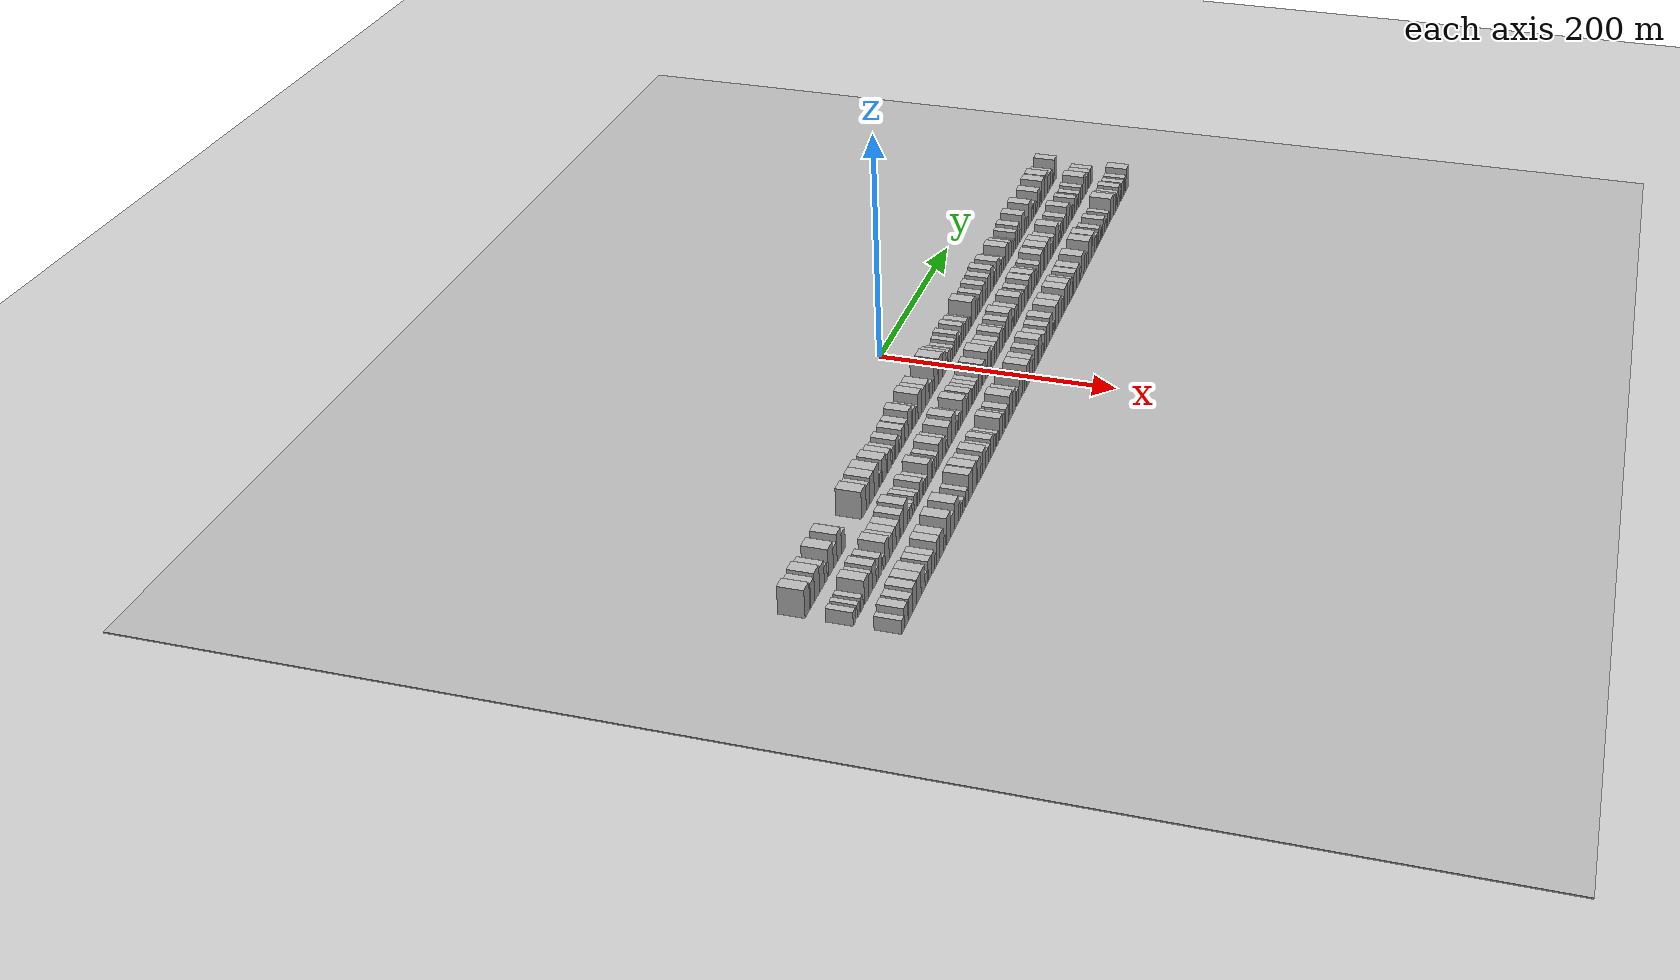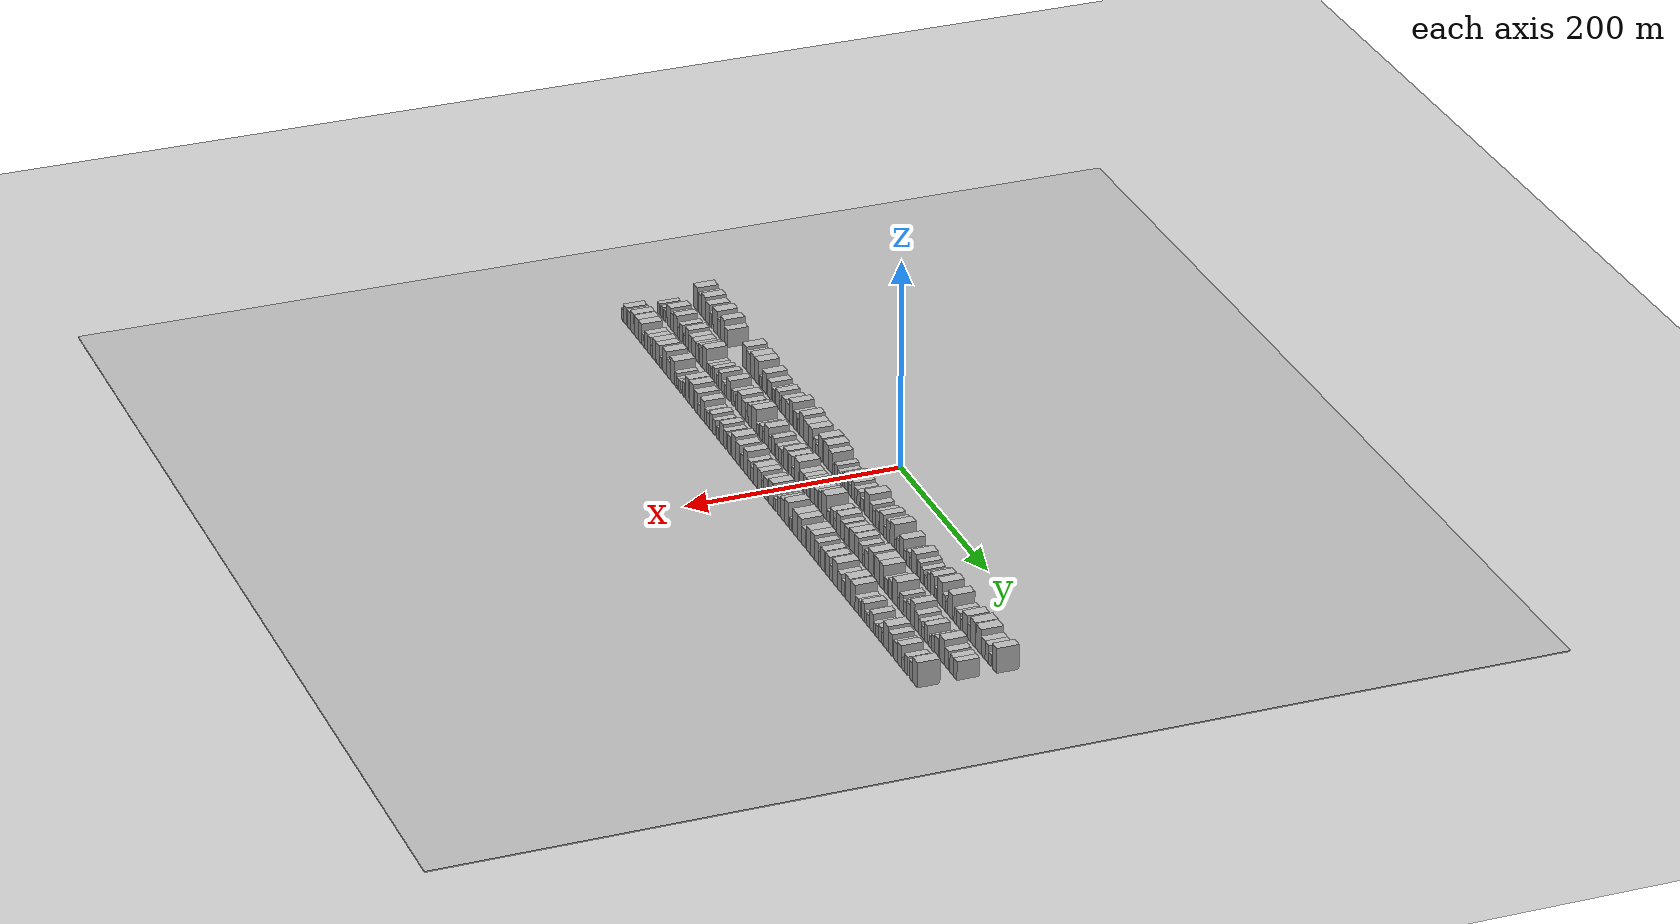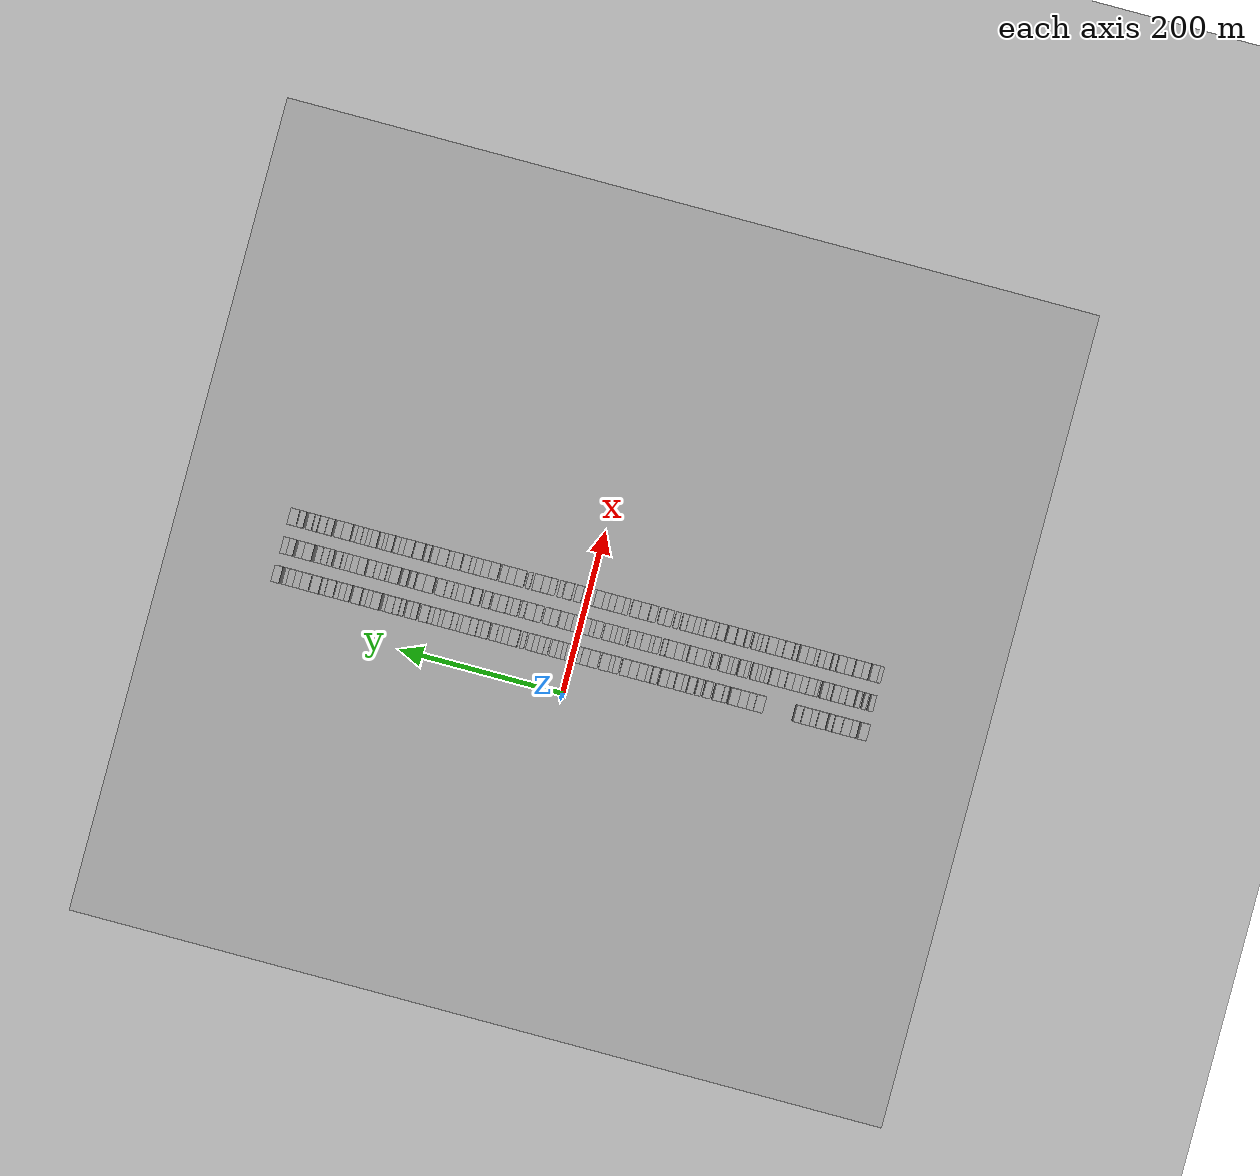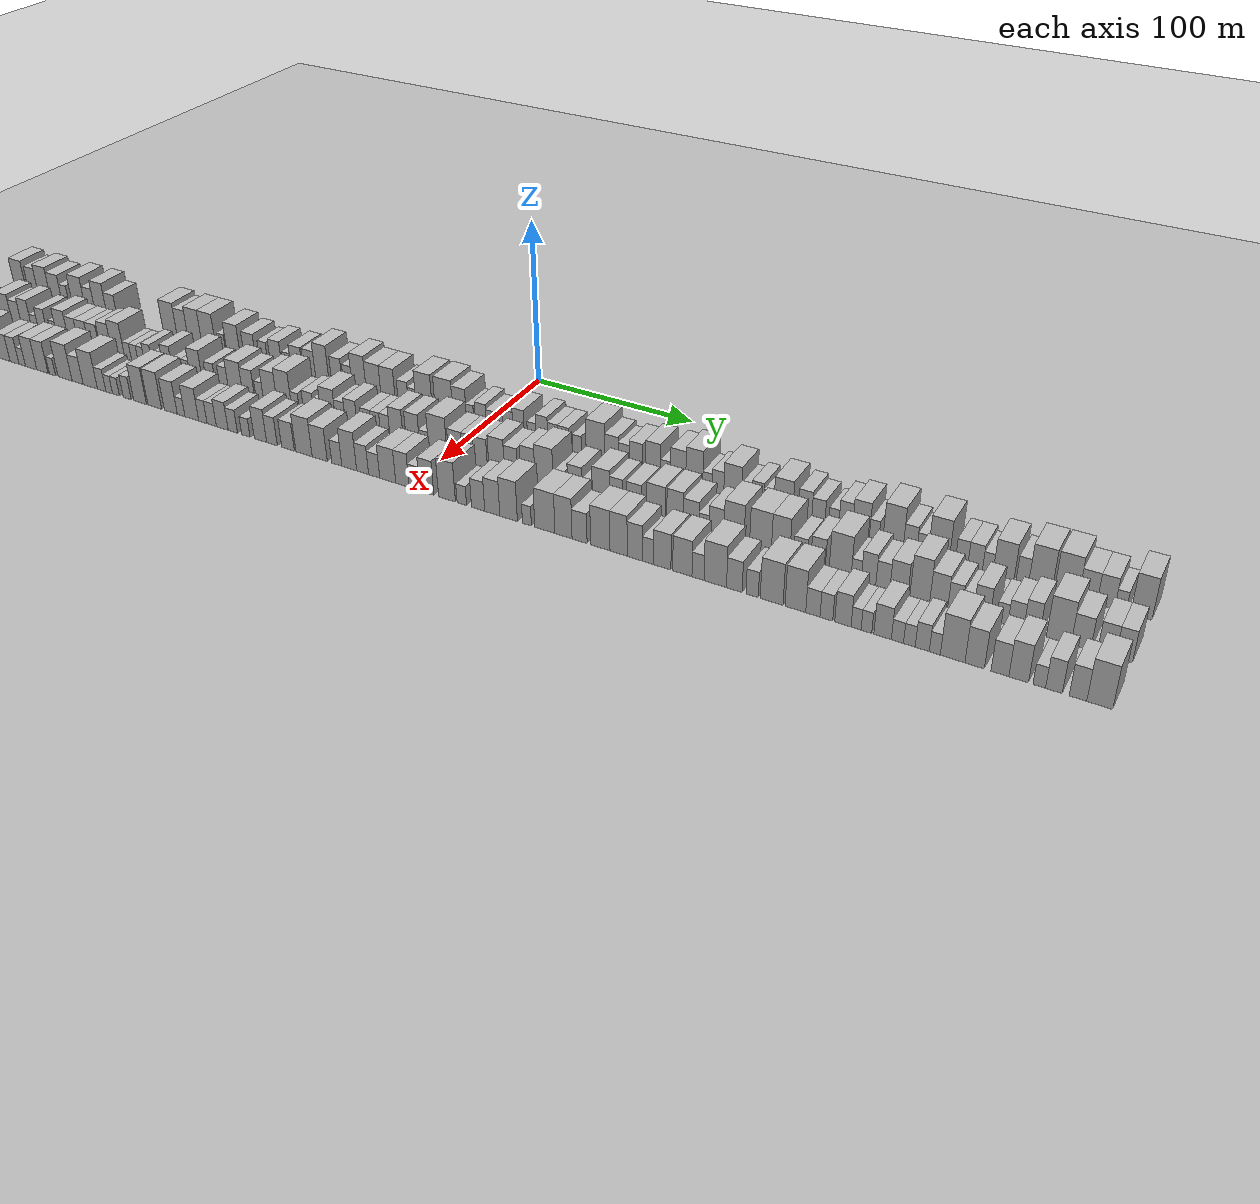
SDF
<?xml version="1.0" encoding="utf-8"?>

<sdf version="1.6">

   <world name="default">

      <gui fullscreen="0">

         <camera name="user_camera">

            <pose>-15 0 4.57585 0 0 0</pose>

            <view_controller>orbit</view_controller>

         </camera>

      </gui>

      <scene>

         <sky>

           <clouds>

             <speed>12</speed>

           </clouds>

         </sky>

         <ambient>0.4 0.4 0.4 1</ambient>

         <background>0.7 0.7 0.7 1</background>

         <shadows>1</shadows>

      </scene>

      <gravity>0 0 -9.8066</gravity>

      <magnetic_field>6e-06 2.3e-05 -4.2e-05</magnetic_field>

      <physics default="0" name="default_physics" type="ode">

         <ode>

            <solver>

               <type>quick</type>

               <iters>10</iters>

               <sor>1.0</sor>

               <use_dynamic_moi_rescaling>0</use_dynamic_moi_rescaling>

            </solver>

            <constraints>

               <cfm>0</cfm>

               <erp>0.2</erp>

               <contact_max_correcting_vel>100</contact_max_correcting_vel>

               <contact_surface_layer>0.001</contact_surface_layer>

            </constraints>

         </ode>

         <max_step_size>0.004</max_step_size>

         <real_time_factor>1</real_time_factor>

         <real_time_update_rate>250</real_time_update_rate>

      </physics>

      <light name="sun" type="directional">

         <cast_shadows>1</cast_shadows>

         <pose>0 0 10 0 0 0</pose>

         <diffuse>0.8 0.8 0.8 1</diffuse>

         <specular>0.2 0.2 0.2 1</specular>

         <attenuation>

            <range>1000</range>

            <constant>0.9</constant>

            <linear>0.01</linear>

            <quadratic>0.001</quadratic>

         </attenuation>

         <direction>-0.5 0.1 -0.9</direction>

      </light>

      <include>

         <name>ground_plane_1</name>

         <uri>model://HANNAS_ground_plane</uri>

         <pose>0 0 0  0 0 0</pose>

      </include>

      <include>

         <name>ground_plane_2</name>

         <uri>model://HANNAS_ground_plane</uri>

         <pose>100 0 0  0 0 0</pose>

      </include>

      <model name="building_1">

         <static>1</static>

         <pose frame="">50.0000 -354.8078 0 0.000000 0.000000 0.000000</pose>

         <link name="link">

            <pose frame="">0 0 12.00 0 0 0</pose>

            <collision name="collision">

               <geometry>

                  <box>

                     <size>20.0000 10.3845 24.0000</size>

                  </box>

               </geometry>

               <max_contacts>10</max_contacts>

               <surface>

                  <contact>

                     <ode/>

                  </contact>

                  <bounce/>

                  <friction>

                     <torsional>

                        <ode/>

                     </torsional>

                     <ode/>

                  </friction>

               </surface>

            </collision>

            <visual name="visual">

               <cast_shadows>0</cast_shadows>

               <geometry>

                  <box>

                     <size>20.0000 10.3845 24.0000</size>

                  </box>

               </geometry>

               <material>

                  <script>

                     <uri>model://HANNAS_wall/materials/scripts</uri>

                     <uri>model://HANNAS_wall/materials/textures</uri>

                     <name>vrc/HANNAS_wall</name>

                  </script>

               </material>

            </visual>

            <self_collide>0</self_collide>

            <enable_wind>0</enable_wind>

            <kinematic>0</kinematic>

         </link>

      </model>

      <model name="building_2">

         <static>1</static>

         <pose frame="">50.0000 -343.3684 0 0.000000 0.000000 0.000000</pose>

         <link name="link">

            <pose frame="">0 0 10.50 0 0 0</pose>

            <collision name="collision">

               <geometry>

                  <box>

                     <size>20.0000 8.4943 21.0000</size>

                  </box>

               </geometry>

               <max_contacts>10</max_contacts>

               <surface>

                  <contact>

                     <ode/>

                  </contact>

                  <bounce/>

                  <friction>

                     <torsional>

                        <ode/>

                     </torsional>

                     <ode/>

                  </friction>

               </surface>

            </collision>

            <visual name="visual">

               <cast_shadows>0</cast_shadows>

               <geometry>

                  <box>

                     <size>20.0000 8.4943 21.0000</size>

                  </box>

               </geometry>

               <material>

                  <script>

                     <uri>model://HANNAS_wall/materials/scripts</uri>

                     <uri>model://HANNAS_wall/materials/textures</uri>

                     <name>vrc/HANNAS_wall</name>

                  </script>

               </material>

            </visual>

            <self_collide>0</self_collide>

            <enable_wind>0</enable_wind>

            <kinematic>0</kinematic>

         </link>

      </model>

      <model name="building_3">

         <static>1</static>

         <pose frame="">50.0000 -333.7885 0 0.000000 0.000000 0.000000</pose>

         <link name="link">

            <pose frame="">0 0 12.00 0 0 0</pose>

            <collision name="collision">

               <geometry>

                  <box>

                     <size>20.0000 10.6656 24.0000</size>

                  </box>

               </geometry>

               <max_contacts>10</max_contacts>

               <surface>

                  <contact>

                     <ode/>

                  </contact>

                  <bounce/>

                  <friction>

                     <torsional>

                        <ode/>

                     </torsional>

                     <ode/>

                  </friction>

               </surface>

            </collision>

            <visual name="visual">

               <cast_shadows>0</cast_shadows>

               <geometry>

                  <box>

                     <size>20.0000 10.6656 24.0000</size>

                  </box>

               </geometry>

               <material>

                  <script>

                     <uri>model://HANNAS_wall/materials/scripts</uri>

                     <uri>model://HANNAS_wall/materials/textures</uri>

                     <name>vrc/HANNAS_wall</name>

                  </script>

               </material>

            </visual>

            <self_collide>0</self_collide>

            <enable_wind>0</enable_wind>

            <kinematic>0</kinematic>

         </link>

      </model>

      <model name="building_4">

         <static>1</static>

         <pose frame="">50.0000 -323.4467 0 0.000000 0.000000 0.000000</pose>

         <link name="link">

            <pose frame="">0 0 10.50 0 0 0</pose>

            <collision name="collision">

               <geometry>

                  <box>

                     <size>20.0000 10.0181 21.0000</size>

                  </box>

               </geometry>

               <max_contacts>10</max_contacts>

               <surface>

                  <contact>

                     <ode/>

                  </contact>

                  <bounce/>

                  <friction>

                     <torsional>

                        <ode/>

                     </torsional>

                     <ode/>

                  </friction>

               </surface>

            </collision>

            <visual name="visual">

               <cast_shadows>0</cast_shadows>

               <geometry>

                  <box>

                     <size>20.0000 10.0181 21.0000</size>

                  </box>

               </geometry>

               <material>

                  <script>

                     <uri>model://HANNAS_wall/materials/scripts</uri>

                     <uri>model://HANNAS_wall/materials/textures</uri>

                     <name>vrc/HANNAS_wall</name>

                  </script>

               </material>

            </visual>

            <self_collide>0</self_collide>

            <enable_wind>0</enable_wind>

            <kinematic>0</kinematic>

         </link>

      </model>

      <model name="building_5">

         <static>1</static>

         <pose frame="">50.0000 -315.3595 0 0.000000 0.000000 0.000000</pose>

         <link name="link">

            <pose frame="">0 0 7.50 0 0 0</pose>

            <collision name="collision">

               <geometry>

                  <box>

                     <size>20.0000 6.1562 15.0000</size>

                  </box>

               </geometry>

               <max_contacts>10</max_contacts>

               <surface>

                  <contact>

                     <ode/>

                  </contact>

                  <bounce/>

                  <friction>

                     <torsional>

                        <ode/>

                     </torsional>

                     <ode/>

                  </friction>

               </surface>

            </collision>

            <visual name="visual">

               <cast_shadows>0</cast_shadows>

               <geometry>

                  <box>

                     <size>20.0000 6.1562 15.0000</size>

                  </box>

               </geometry>

               <material>

                  <script>

                     <uri>model://HANNAS_wall/materials/scripts</uri>

                     <uri>model://HANNAS_wall/materials/textures</uri>

                     <name>vrc/HANNAS_wall</name>

                  </script>

               </material>

            </visual>

            <self_collide>0</self_collide>

            <enable_wind>0</enable_wind>

            <kinematic>0</kinematic>

         </link>

      </model>

      <model name="building_6">

         <static>1</static>

         <pose frame="">50.0000 -303.7663 0 0.000000 0.000000 0.000000</pose>

         <link name="link">

            <pose frame="">0 0 12.00 0 0 0</pose>

            <collision name="collision">

               <geometry>

                  <box>

                     <size>20.0000 11.0303 24.0000</size>

                  </box>

               </geometry>

               <max_contacts>10</max_contacts>

               <surface>

                  <contact>

                     <ode/>

                  </contact>

                  <bounce/>

                  <friction>

                     <torsional>

                        <ode/>

                     </torsional>

                     <ode/>

                  </friction>

               </surface>

            </collision>

            <visual name="visual">

               <cast_shadows>0</cast_shadows>

               <geometry>

                  <box>

                     <size>20.0000 11.0303 24.0000</size>

                  </box>

               </geometry>

               <material>

                  <script>

                     <uri>model://HANNAS_wall/materials/scripts</uri>

                     <uri>model://HANNAS_wall/materials/textures</uri>

                     <name>vrc/HANNAS_wall</name>

                  </script>

               </material>

            </visual>

            <self_collide>0</self_collide>

            <enable_wind>0</enable_wind>

            <kinematic>0</kinematic>

         </link>

      </model>

      <model name="building_7">

         <static>1</static>

         <pose frame="">50.0000 -294.1238 0 0.000000 0.000000 0.000000</pose>

         <link name="link">

            <pose frame="">0 0 9.00 0 0 0</pose>

            <collision name="collision">

               <geometry>

                  <box>

                     <size>20.0000 8.2547 18.0000</size>

                  </box>

               </geometry>

               <max_contacts>10</max_contacts>

               <surface>

                  <contact>

                     <ode/>

                  </contact>

                  <bounce/>

                  <friction>

                     <torsional>

                        <ode/>

                     </torsional>

                     <ode/>

                  </friction>

               </surface>

            </collision>

            <visual name="visual">

               <cast_shadows>0</cast_shadows>

               <geometry>

                  <box>

                     <size>20.0000 8.2547 18.0000</size>

                  </box>

               </geometry>

               <material>

                  <script>

                     <uri>model://HANNAS_wall/materials/scripts</uri>

                     <uri>model://HANNAS_wall/materials/textures</uri>

                     <name>vrc/HANNAS_wall</name>

                  </script>

               </material>

            </visual>

            <self_collide>0</self_collide>

            <enable_wind>0</enable_wind>

            <kinematic>0</kinematic>

         </link>

      </model>

      <model name="building_8">

         <static>1</static>

         <pose frame="">50.0000 -284.9374 0 0.000000 0.000000 0.000000</pose>

         <link name="link">

            <pose frame="">0 0 12.00 0 0 0</pose>

            <collision name="collision">

               <geometry>

                  <box>

                     <size>20.0000 10.1181 24.0000</size>

                  </box>

               </geometry>

               <max_contacts>10</max_contacts>

               <surface>

                  <contact>

                     <ode/>

                  </contact>

                  <bounce/>

                  <friction>

                     <torsional>

                        <ode/>

                     </torsional>

                     <ode/>

                  </friction>

               </surface>

            </collision>

            <visual name="visual">

               <cast_shadows>0</cast_shadows>

               <geometry>

                  <box>

                     <size>20.0000 10.1181 24.0000</size>

                  </box>

               </geometry>

               <material>

                  <script>

                     <uri>model://HANNAS_wall/materials/scripts</uri>

                     <uri>model://HANNAS_wall/materials/textures</uri>

                     <name>vrc/HANNAS_wall</name>

                  </script>

               </material>

            </visual>

            <self_collide>0</self_collide>

            <enable_wind>0</enable_wind>

            <kinematic>0</kinematic>

         </link>

      </model>

      <model name="building_9">

         <static>1</static>

         <pose frame="">50.0000 -275.5787 0 0.000000 0.000000 0.000000</pose>

         <link name="link">

            <pose frame="">0 0 9.00 0 0 0</pose>

            <collision name="collision">

               <geometry>

                  <box>

                     <size>20.0000 8.5992 18.0000</size>

                  </box>

               </geometry>

               <max_contacts>10</max_contacts>

               <surface>

                  <contact>

                     <ode/>

                  </contact>

                  <bounce/>

                  <friction>

                     <torsional>

                        <ode/>

                     </torsional>

                     <ode/>

                  </friction>

               </surface>

            </collision>

            <visual name="visual">

               <cast_shadows>0</cast_shadows>

               <geometry>

                  <box>

                     <size>20.0000 8.5992 18.0000</size>

                  </box>

               </geometry>

               <material>

                  <script>

                     <uri>model://HANNAS_wall/materials/scripts</uri>

                     <uri>model://HANNAS_wall/materials/textures</uri>

                     <name>vrc/HANNAS_wall</name>

                  </script>

               </material>

            </visual>

            <self_collide>0</self_collide>

            <enable_wind>0</enable_wind>

            <kinematic>0</kinematic>

         </link>

      </model>

      <model name="building_10">

         <static>1</static>

         <pose frame="">50.0000 -227.6581 0 0.000000 0.000000 0.000000</pose>

         <link name="link">

            <pose frame="">0 0 12.00 0 0 0</pose>

            <collision name="collision">

               <geometry>

                  <box>

                     <size>20.0000 11.0807 24.0000</size>

                  </box>

               </geometry>

               <max_contacts>10</max_contacts>

               <surface>

                  <contact>

                     <ode/>

                  </contact>

                  <bounce/>

                  <friction>

                     <torsional>

                        <ode/>

                     </torsional>

                     <ode/>

                  </friction>

               </surface>

            </collision>

            <visual name="visual">

               <cast_shadows>0</cast_shadows>

               <geometry>

                  <box>

                     <size>20.0000 11.0807 24.0000</size>

                  </box>

               </geometry>

               <material>

                  <script>

                     <uri>model://HANNAS_wall/materials/scripts</uri>

                     <uri>model://HANNAS_wall/materials/textures</uri>

                     <name>vrc/HANNAS_wall</name>

                  </script>

               </material>

            </visual>

            <self_collide>0</self_collide>

            <enable_wind>0</enable_wind>

            <kinematic>0</kinematic>

         </link>

      </model>

      <model name="building_11">

         <static>1</static>

         <pose frame="">50.0000 -217.6693 0 0.000000 0.000000 0.000000</pose>

         <link name="link">

            <pose frame="">0 0 10.50 0 0 0</pose>

            <collision name="collision">

               <geometry>

                  <box>

                     <size>20.0000 8.8970 21.0000</size>

                  </box>

               </geometry>

               <max_contacts>10</max_contacts>

               <surface>

                  <contact>

                     <ode/>

                  </contact>

                  <bounce/>

                  <friction>

                     <torsional>

                        <ode/>

                     </torsional>

                     <ode/>

                  </friction>

               </surface>

            </collision>

            <visual name="visual">

               <cast_shadows>0</cast_shadows>

               <geometry>

                  <box>

                     <size>20.0000 8.8970 21.0000</size>

                  </box>

               </geometry>

               <material>

                  <script>

                     <uri>model://HANNAS_wall/materials/scripts</uri>

                     <uri>model://HANNAS_wall/materials/textures</uri>

                     <name>vrc/HANNAS_wall</name>

                  </script>

               </material>

            </visual>

            <self_collide>0</self_collide>

            <enable_wind>0</enable_wind>

            <kinematic>0</kinematic>

         </link>

      </model>

      <model name="building_12">

         <static>1</static>

         <pose frame="">50.0000 -207.8444 0 0.000000 0.000000 0.000000</pose>

         <link name="link">

            <pose frame="">0 0 12.00 0 0 0</pose>

            <collision name="collision">

               <geometry>

                  <box>

                     <size>20.0000 10.7528 24.0000</size>

                  </box>

               </geometry>

               <max_contacts>10</max_contacts>

               <surface>

                  <contact>

                     <ode/>

                  </contact>

                  <bounce/>

                  <friction>

                     <torsional>

                        <ode/>

                     </torsional>

                     <ode/>

                  </friction>

               </surface>

            </collision>

            <visual name="visual">

               <cast_shadows>0</cast_shadows>

               <geometry>

                  <box>

                     <size>20.0000 10.7528 24.0000</size>

                  </box>

               </geometry>

               <material>

                  <script>

                     <uri>model://HANNAS_wall/materials/scripts</uri>

                     <uri>model://HANNAS_wall/materials/textures</uri>

                     <name>vrc/HANNAS_wall</name>

                  </script>

               </material>

            </visual>

            <self_collide>0</self_collide>

            <enable_wind>0</enable_wind>

            <kinematic>0</kinematic>

         </link>

      </model>

      <model name="building_13">

         <static>1</static>

         <pose frame="">50.0000 -196.9216 0 0.000000 0.000000 0.000000</pose>

         <link name="link">

            <pose frame="">0 0 12.00 0 0 0</pose>

            <collision name="collision">

               <geometry>

                  <box>

                     <size>20.0000 11.0927 24.0000</size>

                  </box>

               </geometry>

               <max_contacts>10</max_contacts>

               <surface>

                  <contact>

                     <ode/>

                  </contact>

                  <bounce/>

                  <friction>

                     <torsional>

                        <ode/>

                     </torsional>

                     <ode/>

                  </friction>

               </surface>

            </collision>

            <visual name="visual">

               <cast_shadows>0</cast_shadows>

               <geometry>

                  <box>

                     <size>20.0000 11.0927 24.0000</size>

                  </box>

               </geometry>

               <material>

                  <script>

                     <uri>model://HANNAS_wall/materials/scripts</uri>

                     <uri>model://HANNAS_wall/materials/textures</uri>

                     <name>vrc/HANNAS_wall</name>

                  </script>

               </material>

            </visual>

            <self_collide>0</self_collide>

            <enable_wind>0</enable_wind>

            <kinematic>0</kinematic>

         </link>

      </model>

      <model name="building_14">

         <static>1</static>

         <pose frame="">50.0000 -186.6252 0 0.000000 0.000000 0.000000</pose>

         <link name="link">

            <pose frame="">0 0 6.00 0 0 0</pose>

            <collision name="collision">

               <geometry>

                  <box>

                     <size>20.0000 5.5001 12.0000</size>

                  </box>

               </geometry>

               <max_contacts>10</max_contacts>

               <surface>

                  <contact>

                     <ode/>

                  </contact>

                  <bounce/>

                  <friction>

                     <torsional>

                        <ode/>

                     </torsional>

                     <ode/>

                  </friction>

               </surface>

            </collision>

            <visual name="visual">

               <cast_shadows>0</cast_shadows>

               <geometry>

                  <box>

                     <size>20.0000 5.5001 12.0000</size>

                  </box>

               </geometry>

               <material>

                  <script>

                     <uri>model://HANNAS_wall/materials/scripts</uri>

                     <uri>model://HANNAS_wall/materials/textures</uri>

                     <name>vrc/HANNAS_wall</name>

                  </script>

               </material>

            </visual>

            <self_collide>0</self_collide>

            <enable_wind>0</enable_wind>

            <kinematic>0</kinematic>

         </link>

      </model>

      <model name="building_15">

         <static>1</static>

         <pose frame="">50.0000 -177.6738 0 0.000000 0.000000 0.000000</pose>

         <link name="link">

            <pose frame="">0 0 10.50 0 0 0</pose>

            <collision name="collision">

               <geometry>

                  <box>

                     <size>20.0000 10.4028 21.0000</size>

                  </box>

               </geometry>

               <max_contacts>10</max_contacts>

               <surface>

                  <contact>

                     <ode/>

                  </contact>

                  <bounce/>

                  <friction>

                     <torsional>

                        <ode/>

                     </torsional>

                     <ode/>

                  </friction>

               </surface>

            </collision>

            <visual name="visual">

               <cast_shadows>0</cast_shadows>

               <geometry>

                  <box>

                     <size>20.0000 10.4028 21.0000</size>

                  </box>

               </geometry>

               <material>

                  <script>

                     <uri>model://HANNAS_wall/materials/scripts</uri>

                     <uri>model://HANNAS_wall/materials/textures</uri>

                     <name>vrc/HANNAS_wall</name>

                  </script>

               </material>

            </visual>

            <self_collide>0</self_collide>

            <enable_wind>0</enable_wind>

            <kinematic>0</kinematic>

         </link>

      </model>

      <model name="building_16">

         <static>1</static>

         <pose frame="">50.0000 -164.9744 0 0.000000 0.000000 0.000000</pose>

         <link name="link">

            <pose frame="">0 0 9.00 0 0 0</pose>

            <collision name="collision">

               <geometry>

                  <box>

                     <size>20.0000 8.9960 18.0000</size>

                  </box>

               </geometry>

               <max_contacts>10</max_contacts>

               <surface>

                  <contact>

                     <ode/>

                  </contact>

                  <bounce/>

                  <friction>

                     <torsional>

                        <ode/>

                     </torsional>

                     <ode/>

                  </friction>

               </surface>

            </collision>

            <visual name="visual">

               <cast_shadows>0</cast_shadows>

               <geometry>

                  <box>

                     <size>20.0000 8.9960 18.0000</size>

                  </box>

               </geometry>

               <material>

                  <script>

                     <uri>model://HANNAS_wall/materials/scripts</uri>

                     <uri>model://HANNAS_wall/materials/textures</uri>

                     <name>vrc/HANNAS_wall</name>

                  </script>

               </material>

            </visual>

            <self_collide>0</self_collide>

            <enable_wind>0</enable_wind>

            <kinematic>0</kinematic>

         </link>

      </model>

      <model name="building_17">

         <static>1</static>

         <pose frame="">50.0000 -154.3775 0 0.000000 0.000000 0.000000</pose>

         <link name="link">

            <pose frame="">0 0 7.50 0 0 0</pose>

            <collision name="collision">

               <geometry>

                  <box>

                     <size>20.0000 6.1977 15.0000</size>

                  </box>

               </geometry>

               <max_contacts>10</max_contacts>

               <surface>

                  <contact>

                     <ode/>

                  </contact>

                  <bounce/>

                  <friction>

                     <torsional>

                        <ode/>

                     </torsional>

                     <ode/>

                  </friction>

               </surface>

            </collision>

            <visual name="visual">

               <cast_shadows>0</cast_shadows>

               <geometry>

                  <box>

                     <size>20.0000 6.1977 15.0000</size>

                  </box>

               </geometry>

               <material>

                  <script>

                     <uri>model://HANNAS_wall/materials/scripts</uri>

                     <uri>model://HANNAS_wall/materials/textures</uri>

                     <name>vrc/HANNAS_wall</name>

                  </script>

               </material>

            </visual>

            <self_collide>0</self_collide>

            <enable_wind>0</enable_wind>

            <kinematic>0</kinematic>

         </link>

      </model>

      <model name="building_18">

         <static>1</static>

         <pose frame="">50.0000 -144.9723 0 0.000000 0.000000 0.000000</pose>

         <link name="link">

            <pose frame="">0 0 9.00 0 0 0</pose>

            <collision name="collision">

               <geometry>

                  <box>

                     <size>20.0000 8.6127 18.0000</size>

                  </box>

               </geometry>

               <max_contacts>10</max_contacts>

               <surface>

                  <contact>

                     <ode/>

                  </contact>

                  <bounce/>

                  <friction>

                     <torsional>

                        <ode/>

                     </torsional>

                     <ode/>

                  </friction>

               </surface>

            </collision>

            <visual name="visual">

               <cast_shadows>0</cast_shadows>

               <geometry>

                  <box>

                     <size>20.0000 8.6127 18.0000</size>

                  </box>

               </geometry>

               <material>

                  <script>

                     <uri>model://HANNAS_wall/materials/scripts</uri>

                     <uri>model://HANNAS_wall/materials/textures</uri>

                     <name>vrc/HANNAS_wall</name>

                  </script>

               </material>

            </visual>

            <self_collide>0</self_collide>

            <enable_wind>0</enable_wind>

            <kinematic>0</kinematic>

         </link>

      </model>

      <model name="building_19">

         <static>1</static>

         <pose frame="">50.0000 -136.6993 0 0.000000 0.000000 0.000000</pose>

         <link name="link">

            <pose frame="">0 0 6.00 0 0 0</pose>

            <collision name="collision">

               <geometry>

                  <box>

                     <size>20.0000 5.9333 12.0000</size>

                  </box>

               </geometry>

               <max_contacts>10</max_contacts>

               <surface>

                  <contact>

                     <ode/>

                  </contact>

                  <bounce/>

                  <friction>

                     <torsional>

                        <ode/>

                     </torsional>

                     <ode/>

                  </friction>

               </surface>

            </collision>

            <visual name="visual">

               <cast_shadows>0</cast_shadows>

               <geometry>

                  <box>

                     <size>20.0000 5.9333 12.0000</size>

                  </box>

               </geometry>

               <material>

                  <script>

                     <uri>model://HANNAS_wall/materials/scripts</uri>

                     <uri>model://HANNAS_wall/materials/textures</uri>

                     <name>vrc/HANNAS_wall</name>

                  </script>

               </material>

            </visual>

            <self_collide>0</self_collide>

            <enable_wind>0</enable_wind>

            <kinematic>0</kinematic>

         </link>

      </model>

      <model name="building_20">

         <static>1</static>

         <pose frame="">50.0000 -129.4622 0 0.000000 0.000000 0.000000</pose>

         <link name="link">

            <pose frame="">0 0 9.00 0 0 0</pose>

            <collision name="collision">

               <geometry>

                  <box>

                     <size>20.0000 8.5408 18.0000</size>

                  </box>

               </geometry>

               <max_contacts>10</max_contacts>

               <surface>

                  <contact>

                     <ode/>

                  </contact>

                  <bounce/>

                  <friction>

                     <torsional>

                        <ode/>

                     </torsional>

                     <ode/>

                  </friction>

               </surface>

            </collision>

            <visual name="visual">

               <cast_shadows>0</cast_shadows>

               <geometry>

                  <box>

                     <size>20.0000 8.5408 18.0000</size>

                  </box>

               </geometry>

               <material>

                  <script>

                     <uri>model://HANNAS_wall/materials/scripts</uri>

                     <uri>model://HANNAS_wall/materials/textures</uri>

                     <name>vrc/HANNAS_wall</name>

                  </script>

               </material>

            </visual>

            <self_collide>0</self_collide>

            <enable_wind>0</enable_wind>

            <kinematic>0</kinematic>

         </link>

      </model>

      <model name="building_21">

         <static>1</static>

         <pose frame="">50.0000 -119.9878 0 0.000000 0.000000 0.000000</pose>

         <link name="link">

            <pose frame="">0 0 9.00 0 0 0</pose>

            <collision name="collision">

               <geometry>

                  <box>

                     <size>20.0000 8.4080 18.0000</size>

                  </box>

               </geometry>

               <max_contacts>10</max_contacts>

               <surface>

                  <contact>

                     <ode/>

                  </contact>

                  <bounce/>

                  <friction>

                     <torsional>

                        <ode/>

                     </torsional>

                     <ode/>

                  </friction>

               </surface>

            </collision>

            <visual name="visual">

               <cast_shadows>0</cast_shadows>

               <geometry>

                  <box>

                     <size>20.0000 8.4080 18.0000</size>

                  </box>

               </geometry>

               <material>

                  <script>

                     <uri>model://HANNAS_wall/materials/scripts</uri>

                     <uri>model://HANNAS_wall/materials/textures</uri>

                     <name>vrc/HANNAS_wall</name>

                  </script>

               </material>

            </visual>

            <self_collide>0</self_collide>

            <enable_wind>0</enable_wind>

            <kinematic>0</kinematic>

         </link>

      </model>

      <model name="building_22">

         <static>1</static>

         <pose frame="">50.0000 -110.8837 0 0.000000 0.000000 0.000000</pose>

         <link name="link">

            <pose frame="">0 0 12.00 0 0 0</pose>

            <collision name="collision">

               <geometry>

                  <box>

                     <size>20.0000 9.8003 24.0000</size>

                  </box>

               </geometry>

               <max_contacts>10</max_contacts>

               <surface>

                  <contact>

                     <ode/>

                  </contact>

                  <bounce/>

                  <friction>

                     <torsional>

                        <ode/>

                     </torsional>

                     <ode/>

                  </friction>

               </surface>

            </collision>

            <visual name="visual">

               <cast_shadows>0</cast_shadows>

               <geometry>

                  <box>

                     <size>20.0000 9.8003 24.0000</size>

                  </box>

               </geometry>

               <material>

                  <script>

                     <uri>model://HANNAS_wall/materials/scripts</uri>

                     <uri>model://HANNAS_wall/materials/textures</uri>

                     <name>vrc/HANNAS_wall</name>

                  </script>

               </material>

            </visual>

            <self_collide>0</self_collide>

            <enable_wind>0</enable_wind>

            <kinematic>0</kinematic>

         </link>

      </model>

      <model name="building_23">

         <static>1</static>

         <pose frame="">50.0000 -100.1046 0 0.000000 0.000000 0.000000</pose>

         <link name="link">

            <pose frame="">0 0 9.00 0 0 0</pose>

            <collision name="collision">

               <geometry>

                  <box>

                     <size>20.0000 7.7578 18.0000</size>

                  </box>

               </geometry>

               <max_contacts>10</max_contacts>

               <surface>

                  <contact>

                     <ode/>

                  </contact>

                  <bounce/>

                  <friction>

                     <torsional>

                        <ode/>

                     </torsional>

                     <ode/>

                  </friction>

               </surface>

            </collision>

            <visual name="visual">

               <cast_shadows>0</cast_shadows>

               <geometry>

                  <box>

                     <size>20.0000 7.7578 18.0000</size>

                  </box>

               </geometry>

               <material>

                  <script>

                     <uri>model://HANNAS_wall/materials/scripts</uri>

                     <uri>model://HANNAS_wall/materials/textures</uri>

                     <name>vrc/HANNAS_wall</name>

                  </script>

               </material>

            </visual>

            <self_collide>0</self_collide>

            <enable_wind>0</enable_wind>

            <kinematic>0</kinematic>

         </link>

      </model>

      <model name="building_24">

         <static>1</static>

         <pose frame="">50.0000 -92.2042 0 0.000000 0.000000 0.000000</pose>

         <link name="link">

            <pose frame="">0 0 7.50 0 0 0</pose>

            <collision name="collision">

               <geometry>

                  <box>

                     <size>20.0000 6.0432 15.0000</size>

                  </box>

               </geometry>

               <max_contacts>10</max_contacts>

               <surface>

                  <contact>

                     <ode/>

                  </contact>

                  <bounce/>

                  <friction>

                     <torsional>

                        <ode/>

                     </torsional>

                     <ode/>

                  </friction>

               </surface>

            </collision>

            <visual name="visual">

               <cast_shadows>0</cast_shadows>

               <geometry>

                  <box>

                     <size>20.0000 6.0432 15.0000</size>

                  </box>

               </geometry>

               <material>

                  <script>

                     <uri>model://HANNAS_wall/materials/scripts</uri>

                     <uri>model://HANNAS_wall/materials/textures</uri>

                     <name>vrc/HANNAS_wall</name>

                  </script>

               </material>

            </visual>

            <self_collide>0</self_collide>

            <enable_wind>0</enable_wind>

            <kinematic>0</kinematic>

         </link>

      </model>

      <model name="building_25">

         <static>1</static>

         <pose frame="">50.0000 -84.1262 0 0.000000 0.000000 0.000000</pose>

         <link name="link">

            <pose frame="">0 0 12.00 0 0 0</pose>

            <collision name="collision">

               <geometry>

                  <box>

                     <size>20.0000 10.1128 24.0000</size>

                  </box>

               </geometry>

               <max_contacts>10</max_contacts>

               <surface>

                  <contact>

                     <ode/>

                  </contact>

                  <bounce/>

                  <friction>

                     <torsional>

                        <ode/>

                     </torsional>

                     <ode/>

                  </friction>

               </surface>

            </collision>

            <visual name="visual">

               <cast_shadows>0</cast_shadows>

               <geometry>

                  <box>

                     <size>20.0000 10.1128 24.0000</size>

                  </box>

               </geometry>

               <material>

                  <script>

                     <uri>model://HANNAS_wall/materials/scripts</uri>

                     <uri>model://HANNAS_wall/materials/textures</uri>

                     <name>vrc/HANNAS_wall</name>

                  </script>

               </material>

            </visual>

            <self_collide>0</self_collide>

            <enable_wind>0</enable_wind>

            <kinematic>0</kinematic>

         </link>

      </model>

      <model name="building_26">

         <static>1</static>

         <pose frame="">50.0000 -73.8800 0 0.000000 0.000000 0.000000</pose>

         <link name="link">

            <pose frame="">0 0 10.50 0 0 0</pose>

            <collision name="collision">

               <geometry>

                  <box>

                     <size>20.0000 10.3797 21.0000</size>

                  </box>

               </geometry>

               <max_contacts>10</max_contacts>

               <surface>

                  <contact>

                     <ode/>

                  </contact>

                  <bounce/>

                  <friction>

                     <torsional>

                        <ode/>

                     </torsional>

                     <ode/>

                  </friction>

               </surface>

            </collision>

            <visual name="visual">

               <cast_shadows>0</cast_shadows>

               <geometry>

                  <box>

                     <size>20.0000 10.3797 21.0000</size>

                  </box>

               </geometry>

               <material>

                  <script>

                     <uri>model://HANNAS_wall/materials/scripts</uri>

                     <uri>model://HANNAS_wall/materials/textures</uri>

                     <name>vrc/HANNAS_wall</name>

                  </script>

               </material>

            </visual>

            <self_collide>0</self_collide>

            <enable_wind>0</enable_wind>

            <kinematic>0</kinematic>

         </link>

      </model>

      <model name="building_27">

         <static>1</static>

         <pose frame="">50.0000 -63.6983 0 0.000000 0.000000 0.000000</pose>

         <link name="link">

            <pose frame="">0 0 10.50 0 0 0</pose>

            <collision name="collision">

               <geometry>

                  <box>

                     <size>20.0000 9.9836 21.0000</size>

                  </box>

               </geometry>

               <max_contacts>10</max_contacts>

               <surface>

                  <contact>

                     <ode/>

                  </contact>

                  <bounce/>

                  <friction>

                     <torsional>

                        <ode/>

                     </torsional>

                     <ode/>

                  </friction>

               </surface>

            </collision>

            <visual name="visual">

               <cast_shadows>0</cast_shadows>

               <geometry>

                  <box>

                     <size>20.0000 9.9836 21.0000</size>

                  </box>

               </geometry>

               <material>

                  <script>

                     <uri>model://HANNAS_wall/materials/scripts</uri>

                     <uri>model://HANNAS_wall/materials/textures</uri>

                     <name>vrc/HANNAS_wall</name>

                  </script>

               </material>

            </visual>

            <self_collide>0</self_collide>

            <enable_wind>0</enable_wind>

            <kinematic>0</kinematic>

         </link>

      </model>

      <model name="building_28">

         <static>1</static>

         <pose frame="">50.0000 -53.1800 0 0.000000 0.000000 0.000000</pose>

         <link name="link">

            <pose frame="">0 0 7.50 0 0 0</pose>

            <collision name="collision">

               <geometry>

                  <box>

                     <size>20.0000 7.0531 15.0000</size>

                  </box>

               </geometry>

               <max_contacts>10</max_contacts>

               <surface>

                  <contact>

                     <ode/>

                  </contact>

                  <bounce/>

                  <friction>

                     <torsional>

                        <ode/>

                     </torsional>

                     <ode/>

                  </friction>

               </surface>

            </collision>

            <visual name="visual">

               <cast_shadows>0</cast_shadows>

               <geometry>

                  <box>

                     <size>20.0000 7.0531 15.0000</size>

                  </box>

               </geometry>

               <material>

                  <script>

                     <uri>model://HANNAS_wall/materials/scripts</uri>

                     <uri>model://HANNAS_wall/materials/textures</uri>

                     <name>vrc/HANNAS_wall</name>

                  </script>

               </material>

            </visual>

            <self_collide>0</self_collide>

            <enable_wind>0</enable_wind>

            <kinematic>0</kinematic>

         </link>

      </model>

      <model name="building_29">

         <static>1</static>

         <pose frame="">50.0000 -46.9769 0 0.000000 0.000000 0.000000</pose>

         <link name="link">

            <pose frame="">0 0 6.00 0 0 0</pose>

            <collision name="collision">

               <geometry>

                  <box>

                     <size>20.0000 5.3529 12.0000</size>

                  </box>

               </geometry>

               <max_contacts>10</max_contacts>

               <surface>

                  <contact>

                     <ode/>

                  </contact>

                  <bounce/>

                  <friction>

                     <torsional>

                        <ode/>

                     </torsional>

                     <ode/>

                  </friction>

               </surface>

            </collision>

            <visual name="visual">

               <cast_shadows>0</cast_shadows>

               <geometry>

                  <box>

                     <size>20.0000 5.3529 12.0000</size>

                  </box>

               </geometry>

               <material>

                  <script>

                     <uri>model://HANNAS_wall/materials/scripts</uri>

                     <uri>model://HANNAS_wall/materials/textures</uri>

                     <name>vrc/HANNAS_wall</name>

                  </script>

               </material>

            </visual>

            <self_collide>0</self_collide>

            <enable_wind>0</enable_wind>

            <kinematic>0</kinematic>

         </link>

      </model>

      <model name="building_30">

         <static>1</static>

         <pose frame="">50.0000 -38.7092 0 0.000000 0.000000 0.000000</pose>

         <link name="link">

            <pose frame="">0 0 12.00 0 0 0</pose>

            <collision name="collision">

               <geometry>

                  <box>

                     <size>20.0000 11.1826 24.0000</size>

                  </box>

               </geometry>

               <max_contacts>10</max_contacts>

               <surface>

                  <contact>

                     <ode/>

                  </contact>

                  <bounce/>

                  <friction>

                     <torsional>

                        <ode/>

                     </torsional>

                     <ode/>

                  </friction>

               </surface>

            </collision>

            <visual name="visual">

               <cast_shadows>0</cast_shadows>

               <geometry>

                  <box>

                     <size>20.0000 11.1826 24.0000</size>

                  </box>

               </geometry>

               <material>

                  <script>

                     <uri>model://HANNAS_wall/materials/scripts</uri>

                     <uri>model://HANNAS_wall/materials/textures</uri>

                     <name>vrc/HANNAS_wall</name>

                  </script>

               </material>

            </visual>

            <self_collide>0</self_collide>

            <enable_wind>0</enable_wind>

            <kinematic>0</kinematic>

         </link>

      </model>

      <model name="building_31">

         <static>1</static>

         <pose frame="">50.0000 -25.1452 0 0.000000 0.000000 0.000000</pose>

         <link name="link">

            <pose frame="">0 0 12.00 0 0 0</pose>

            <collision name="collision">

               <geometry>

                  <box>

                     <size>20.0000 11.9455 24.0000</size>

                  </box>

               </geometry>

               <max_contacts>10</max_contacts>

               <surface>

                  <contact>

                     <ode/>

                  </contact>

                  <bounce/>

                  <friction>

                     <torsional>

                        <ode/>

                     </torsional>

                     <ode/>

                  </friction>

               </surface>

            </collision>

            <visual name="visual">

               <cast_shadows>0</cast_shadows>

               <geometry>

                  <box>

                     <size>20.0000 11.9455 24.0000</size>

                  </box>

               </geometry>

               <material>

                  <script>

                     <uri>model://HANNAS_wall/materials/scripts</uri>

                     <uri>model://HANNAS_wall/materials/textures</uri>

                     <name>vrc/HANNAS_wall</name>

                  </script>

               </material>

            </visual>

            <self_collide>0</self_collide>

            <enable_wind>0</enable_wind>

            <kinematic>0</kinematic>

         </link>

      </model>

      <model name="building_32">

         <static>1</static>

         <pose frame="">50.0000 -14.6204 0 0.000000 0.000000 0.000000</pose>

         <link name="link">

            <pose frame="">0 0 10.50 0 0 0</pose>

            <collision name="collision">

               <geometry>

                  <box>

                     <size>20.0000 9.1040 21.0000</size>

                  </box>

               </geometry>

               <max_contacts>10</max_contacts>

               <surface>

                  <contact>

                     <ode/>

                  </contact>

                  <bounce/>

                  <friction>

                     <torsional>

                        <ode/>

                     </torsional>

                     <ode/>

                  </friction>

               </surface>

            </collision>

            <visual name="visual">

               <cast_shadows>0</cast_shadows>

               <geometry>

                  <box>

                     <size>20.0000 9.1040 21.0000</size>

                  </box>

               </geometry>

               <material>

                  <script>

                     <uri>model://HANNAS_wall/materials/scripts</uri>

                     <uri>model://HANNAS_wall/materials/textures</uri>

                     <name>vrc/HANNAS_wall</name>

                  </script>

               </material>

            </visual>

            <self_collide>0</self_collide>

            <enable_wind>0</enable_wind>

            <kinematic>0</kinematic>

         </link>

      </model>

      <model name="building_33">

         <static>1</static>

         <pose frame="">50.0000 -7.6376 0 0.000000 0.000000 0.000000</pose>

         <link name="link">

            <pose frame="">0 0 6.00 0 0 0</pose>

            <collision name="collision">

               <geometry>

                  <box>

                     <size>20.0000 4.8615 12.0000</size>

                  </box>

               </geometry>

               <max_contacts>10</max_contacts>

               <surface>

                  <contact>

                     <ode/>

                  </contact>

                  <bounce/>

                  <friction>

                     <torsional>

                        <ode/>

                     </torsional>

                     <ode/>

                  </friction>

               </surface>

            </collision>

            <visual name="visual">

               <cast_shadows>0</cast_shadows>

               <geometry>

                  <box>

                     <size>20.0000 4.8615 12.0000</size>

                  </box>

               </geometry>

               <material>

                  <script>

                     <uri>model://HANNAS_wall/materials/scripts</uri>

                     <uri>model://HANNAS_wall/materials/textures</uri>

                     <name>vrc/HANNAS_wall</name>

                  </script>

               </material>

            </visual>

            <self_collide>0</self_collide>

            <enable_wind>0</enable_wind>

            <kinematic>0</kinematic>

         </link>

      </model>

      <model name="building_34">

         <static>1</static>

         <pose frame="">50.0000 -0.6195 0 0.000000 0.000000 0.000000</pose>

         <link name="link">

            <pose frame="">0 0 7.50 0 0 0</pose>

            <collision name="collision">

               <geometry>

                  <box>

                     <size>20.0000 7.1745 15.0000</size>

                  </box>

               </geometry>

               <max_contacts>10</max_contacts>

               <surface>

                  <contact>

                     <ode/>

                  </contact>

                  <bounce/>

                  <friction>

                     <torsional>

                        <ode/>

                     </torsional>

                     <ode/>

                  </friction>

               </surface>

            </collision>

            <visual name="visual">

               <cast_shadows>0</cast_shadows>

               <geometry>

                  <box>

                     <size>20.0000 7.1745 15.0000</size>

                  </box>

               </geometry>

               <material>

                  <script>

                     <uri>model://HANNAS_wall/materials/scripts</uri>

                     <uri>model://HANNAS_wall/materials/textures</uri>

                     <name>vrc/HANNAS_wall</name>

                  </script>

               </material>

            </visual>

            <self_collide>0</self_collide>

            <enable_wind>0</enable_wind>

            <kinematic>0</kinematic>

         </link>

      </model>

      <model name="building_35">

         <static>1</static>

         <pose frame="">50.0000 5.9453 0 0.000000 0.000000 0.000000</pose>

         <link name="link">

            <pose frame="">0 0 6.00 0 0 0</pose>

            <collision name="collision">

               <geometry>

                  <box>

                     <size>20.0000 5.9553 12.0000</size>

                  </box>

               </geometry>

               <max_contacts>10</max_contacts>

               <surface>

                  <contact>

                     <ode/>

                  </contact>

                  <bounce/>

                  <friction>

                     <torsional>

                        <ode/>

                     </torsional>

                     <ode/>

                  </friction>

               </surface>

            </collision>

            <visual name="visual">

               <cast_shadows>0</cast_shadows>

               <geometry>

                  <box>

                     <size>20.0000 5.9553 12.0000</size>

                  </box>

               </geometry>

               <material>

                  <script>

                     <uri>model://HANNAS_wall/materials/scripts</uri>

                     <uri>model://HANNAS_wall/materials/textures</uri>

                     <name>vrc/HANNAS_wall</name>

                  </script>

               </material>

            </visual>

            <self_collide>0</self_collide>

            <enable_wind>0</enable_wind>

            <kinematic>0</kinematic>

         </link>

      </model>

      <model name="building_36">

         <static>1</static>

         <pose frame="">50.0000 11.5242 0 0.000000 0.000000 0.000000</pose>

         <link name="link">

            <pose frame="">0 0 6.00 0 0 0</pose>

            <collision name="collision">

               <geometry>

                  <box>

                     <size>20.0000 5.2024 12.0000</size>

                  </box>

               </geometry>

               <max_contacts>10</max_contacts>

               <surface>

                  <contact>

                     <ode/>

                  </contact>

                  <bounce/>

                  <friction>

                     <torsional>

                        <ode/>

                     </torsional>

                     <ode/>

                  </friction>

               </surface>

            </collision>

            <visual name="visual">

               <cast_shadows>0</cast_shadows>

               <geometry>

                  <box>

                     <size>20.0000 5.2024 12.0000</size>

                  </box>

               </geometry>

               <material>

                  <script>

                     <uri>model://HANNAS_wall/materials/scripts</uri>

                     <uri>model://HANNAS_wall/materials/textures</uri>

                     <name>vrc/HANNAS_wall</name>

                  </script>

               </material>

            </visual>

            <self_collide>0</self_collide>

            <enable_wind>0</enable_wind>

            <kinematic>0</kinematic>

         </link>

      </model>

      <model name="building_37">

         <static>1</static>

         <pose frame="">50.0000 17.3036 0 0.000000 0.000000 0.000000</pose>

         <link name="link">

            <pose frame="">0 0 7.50 0 0 0</pose>

            <collision name="collision">

               <geometry>

                  <box>

                     <size>20.0000 6.3564 15.0000</size>

                  </box>

               </geometry>

               <max_contacts>10</max_contacts>

               <surface>

                  <contact>

                     <ode/>

                  </contact>

                  <bounce/>

                  <friction>

                     <torsional>

                        <ode/>

                     </torsional>

                     <ode/>

                  </friction>

               </surface>

            </collision>

            <visual name="visual">

               <cast_shadows>0</cast_shadows>

               <geometry>

                  <box>

                     <size>20.0000 6.3564 15.0000</size>

                  </box>

               </geometry>

               <material>

                  <script>

                     <uri>model://HANNAS_wall/materials/scripts</uri>

                     <uri>model://HANNAS_wall/materials/textures</uri>

                     <name>vrc/HANNAS_wall</name>

                  </script>

               </material>

            </visual>

            <self_collide>0</self_collide>

            <enable_wind>0</enable_wind>

            <kinematic>0</kinematic>

         </link>

      </model>

      <model name="building_38">

         <static>1</static>

         <pose frame="">50.0000 24.1411 0 0.000000 0.000000 0.000000</pose>

         <link name="link">

            <pose frame="">0 0 9.00 0 0 0</pose>

            <collision name="collision">

               <geometry>

                  <box>

                     <size>20.0000 7.3187 18.0000</size>

                  </box>

               </geometry>

               <max_contacts>10</max_contacts>

               <surface>

                  <contact>

                     <ode/>

                  </contact>

                  <bounce/>

                  <friction>

                     <torsional>

                        <ode/>

                     </torsional>

                     <ode/>

                  </friction>

               </surface>

            </collision>

            <visual name="visual">

               <cast_shadows>0</cast_shadows>

               <geometry>

                  <box>

                     <size>20.0000 7.3187 18.0000</size>

                  </box>

               </geometry>

               <material>

                  <script>

                     <uri>model://HANNAS_wall/materials/scripts</uri>

                     <uri>model://HANNAS_wall/materials/textures</uri>

                     <name>vrc/HANNAS_wall</name>

                  </script>

               </material>

            </visual>

            <self_collide>0</self_collide>

            <enable_wind>0</enable_wind>

            <kinematic>0</kinematic>

         </link>

      </model>

      <model name="building_39">

         <static>1</static>

         <pose frame="">50.0000 32.6196 0 0.000000 0.000000 0.000000</pose>

         <link name="link">

            <pose frame="">0 0 6.00 0 0 0</pose>

            <collision name="collision">

               <geometry>

                  <box>

                     <size>20.0000 5.6382 12.0000</size>

                  </box>

               </geometry>

               <max_contacts>10</max_contacts>

               <surface>

                  <contact>

                     <ode/>

                  </contact>

                  <bounce/>

                  <friction>

                     <torsional>

                        <ode/>

                     </torsional>

                     <ode/>

                  </friction>

               </surface>

            </collision>

            <visual name="visual">

               <cast_shadows>0</cast_shadows>

               <geometry>

                  <box>

                     <size>20.0000 5.6382 12.0000</size>

                  </box>

               </geometry>

               <material>

                  <script>

                     <uri>model://HANNAS_wall/materials/scripts</uri>

                     <uri>model://HANNAS_wall/materials/textures</uri>

                     <name>vrc/HANNAS_wall</name>

                  </script>

               </material>

            </visual>

            <self_collide>0</self_collide>

            <enable_wind>0</enable_wind>

            <kinematic>0</kinematic>

         </link>

      </model>

      <model name="building_40">

         <static>1</static>

         <pose frame="">50.0000 39.1190 0 0.000000 0.000000 0.000000</pose>

         <link name="link">

            <pose frame="">0 0 9.00 0 0 0</pose>

            <collision name="collision">

               <geometry>

                  <box>

                     <size>20.0000 7.3605 18.0000</size>

                  </box>

               </geometry>

               <max_contacts>10</max_contacts>

               <surface>

                  <contact>

                     <ode/>

                  </contact>

                  <bounce/>

                  <friction>

                     <torsional>

                        <ode/>

                     </torsional>

                     <ode/>

                  </friction>

               </surface>

            </collision>

            <visual name="visual">

               <cast_shadows>0</cast_shadows>

               <geometry>

                  <box>

                     <size>20.0000 7.3605 18.0000</size>

                  </box>

               </geometry>

               <material>

                  <script>

                     <uri>model://HANNAS_wall/materials/scripts</uri>

                     <uri>model://HANNAS_wall/materials/textures</uri>

                     <name>vrc/HANNAS_wall</name>

                  </script>

               </material>

            </visual>

            <self_collide>0</self_collide>

            <enable_wind>0</enable_wind>

            <kinematic>0</kinematic>

         </link>

      </model>

      <model name="building_41">

         <static>1</static>

         <pose frame="">50.0000 46.0390 0 0.000000 0.000000 0.000000</pose>

         <link name="link">

            <pose frame="">0 0 7.50 0 0 0</pose>

            <collision name="collision">

               <geometry>

                  <box>

                     <size>20.0000 6.4795 15.0000</size>

                  </box>

               </geometry>

               <max_contacts>10</max_contacts>

               <surface>

                  <contact>

                     <ode/>

                  </contact>

                  <bounce/>

                  <friction>

                     <torsional>

                        <ode/>

                     </torsional>

                     <ode/>

                  </friction>

               </surface>

            </collision>

            <visual name="visual">

               <cast_shadows>0</cast_shadows>

               <geometry>

                  <box>

                     <size>20.0000 6.4795 15.0000</size>

                  </box>

               </geometry>

               <material>

                  <script>

                     <uri>model://HANNAS_wall/materials/scripts</uri>

                     <uri>model://HANNAS_wall/materials/textures</uri>

                     <name>vrc/HANNAS_wall</name>

                  </script>

               </material>

            </visual>

            <self_collide>0</self_collide>

            <enable_wind>0</enable_wind>

            <kinematic>0</kinematic>

         </link>

      </model>

      <model name="building_42">

         <static>1</static>

         <pose frame="">50.0000 52.8485 0 0.000000 0.000000 0.000000</pose>

         <link name="link">

            <pose frame="">0 0 7.50 0 0 0</pose>

            <collision name="collision">

               <geometry>

                  <box>

                     <size>20.0000 7.1395 15.0000</size>

                  </box>

               </geometry>

               <max_contacts>10</max_contacts>

               <surface>

                  <contact>

                     <ode/>

                  </contact>

                  <bounce/>

                  <friction>

                     <torsional>

                        <ode/>

                     </torsional>

                     <ode/>

                  </friction>

               </surface>

            </collision>

            <visual name="visual">

               <cast_shadows>0</cast_shadows>

               <geometry>

                  <box>

                     <size>20.0000 7.1395 15.0000</size>

                  </box>

               </geometry>

               <material>

                  <script>

                     <uri>model://HANNAS_wall/materials/scripts</uri>

                     <uri>model://HANNAS_wall/materials/textures</uri>

                     <name>vrc/HANNAS_wall</name>

                  </script>

               </material>

            </visual>

            <self_collide>0</self_collide>

            <enable_wind>0</enable_wind>

            <kinematic>0</kinematic>

         </link>

      </model>

      <model name="building_43">

         <static>1</static>

         <pose frame="">50.0000 61.1249 0 0.000000 0.000000 0.000000</pose>

         <link name="link">

            <pose frame="">0 0 6.00 0 0 0</pose>

            <collision name="collision">

               <geometry>

                  <box>

                     <size>20.0000 5.4133 12.0000</size>

                  </box>

               </geometry>

               <max_contacts>10</max_contacts>

               <surface>

                  <contact>

                     <ode/>

                  </contact>

                  <bounce/>

                  <friction>

                     <torsional>

                        <ode/>

                     </torsional>

                     <ode/>

                  </friction>

               </surface>

            </collision>

            <visual name="visual">

               <cast_shadows>0</cast_shadows>

               <geometry>

                  <box>

                     <size>20.0000 5.4133 12.0000</size>

                  </box>

               </geometry>

               <material>

                  <script>

                     <uri>model://HANNAS_wall/materials/scripts</uri>

                     <uri>model://HANNAS_wall/materials/textures</uri>

                     <name>vrc/HANNAS_wall</name>

                  </script>

               </material>

            </visual>

            <self_collide>0</self_collide>

            <enable_wind>0</enable_wind>

            <kinematic>0</kinematic>

         </link>

      </model>

      <model name="building_44">

         <static>1</static>

         <pose frame="">50.0000 72.6042 0 0.000000 0.000000 0.000000</pose>

         <link name="link">

            <pose frame="">0 0 12.00 0 0 0</pose>

            <collision name="collision">

               <geometry>

                  <box>

                     <size>20.0000 11.5454 24.0000</size>

                  </box>

               </geometry>

               <max_contacts>10</max_contacts>

               <surface>

                  <contact>

                     <ode/>

                  </contact>

                  <bounce/>

                  <friction>

                     <torsional>

                        <ode/>

                     </torsional>

                     <ode/>

                  </friction>

               </surface>

            </collision>

            <visual name="visual">

               <cast_shadows>0</cast_shadows>

               <geometry>

                  <box>

                     <size>20.0000 11.5454 24.0000</size>

                  </box>

               </geometry>

               <material>

                  <script>

                     <uri>model://HANNAS_wall/materials/scripts</uri>

                     <uri>model://HANNAS_wall/materials/textures</uri>

                     <name>vrc/HANNAS_wall</name>

                  </script>

               </material>

            </visual>

            <self_collide>0</self_collide>

            <enable_wind>0</enable_wind>

            <kinematic>0</kinematic>

         </link>

      </model>

      <model name="building_45">

         <static>1</static>

         <pose frame="">50.0000 82.4788 0 0.000000 0.000000 0.000000</pose>

         <link name="link">

            <pose frame="">0 0 9.00 0 0 0</pose>

            <collision name="collision">

               <geometry>

                  <box>

                     <size>20.0000 8.2037 18.0000</size>

                  </box>

               </geometry>

               <max_contacts>10</max_contacts>

               <surface>

                  <contact>

                     <ode/>

                  </contact>

                  <bounce/>

                  <friction>

                     <torsional>

                        <ode/>

                     </torsional>

                     <ode/>

                  </friction>

               </surface>

            </collision>

            <visual name="visual">

               <cast_shadows>0</cast_shadows>

               <geometry>

                  <box>

                     <size>20.0000 8.2037 18.0000</size>

                  </box>

               </geometry>

               <material>

                  <script>

                     <uri>model://HANNAS_wall/materials/scripts</uri>

                     <uri>model://HANNAS_wall/materials/textures</uri>

                     <name>vrc/HANNAS_wall</name>

                  </script>

               </material>

            </visual>

            <self_collide>0</self_collide>

            <enable_wind>0</enable_wind>

            <kinematic>0</kinematic>

         </link>

      </model>

      <model name="building_46">

         <static>1</static>

         <pose frame="">50.0000 89.8488 0 0.000000 0.000000 0.000000</pose>

         <link name="link">

            <pose frame="">0 0 7.50 0 0 0</pose>

            <collision name="collision">

               <geometry>

                  <box>

                     <size>20.0000 6.5365 15.0000</size>

                  </box>

               </geometry>

               <max_contacts>10</max_contacts>

               <surface>

                  <contact>

                     <ode/>

                  </contact>

                  <bounce/>

                  <friction>

                     <torsional>

                        <ode/>

                     </torsional>

                     <ode/>

                  </friction>

               </surface>

            </collision>

            <visual name="visual">

               <cast_shadows>0</cast_shadows>

               <geometry>

                  <box>

                     <size>20.0000 6.5365 15.0000</size>

                  </box>

               </geometry>

               <material>

                  <script>

                     <uri>model://HANNAS_wall/materials/scripts</uri>

                     <uri>model://HANNAS_wall/materials/textures</uri>

                     <name>vrc/HANNAS_wall</name>

                  </script>

               </material>

            </visual>

            <self_collide>0</self_collide>

            <enable_wind>0</enable_wind>

            <kinematic>0</kinematic>

         </link>

      </model>

      <model name="building_47">

         <static>1</static>

         <pose frame="">50.0000 97.1232 0 0.000000 0.000000 0.000000</pose>

         <link name="link">

            <pose frame="">0 0 9.00 0 0 0</pose>

            <collision name="collision">

               <geometry>

                  <box>

                     <size>20.0000 8.0123 18.0000</size>

                  </box>

               </geometry>

               <max_contacts>10</max_contacts>

               <surface>

                  <contact>

                     <ode/>

                  </contact>

                  <bounce/>

                  <friction>

                     <torsional>

                        <ode/>

                     </torsional>

                     <ode/>

                  </friction>

               </surface>

            </collision>

            <visual name="visual">

               <cast_shadows>0</cast_shadows>

               <geometry>

                  <box>

                     <size>20.0000 8.0123 18.0000</size>

                  </box>

               </geometry>

               <material>

                  <script>

                     <uri>model://HANNAS_wall/materials/scripts</uri>

                     <uri>model://HANNAS_wall/materials/textures</uri>

                     <name>vrc/HANNAS_wall</name>

                  </script>

               </material>

            </visual>

            <self_collide>0</self_collide>

            <enable_wind>0</enable_wind>

            <kinematic>0</kinematic>

         </link>

      </model>

      <model name="building_48">

         <static>1</static>

         <pose frame="">50.0000 107.5432 0 0.000000 0.000000 0.000000</pose>

         <link name="link">

            <pose frame="">0 0 10.50 0 0 0</pose>

            <collision name="collision">

               <geometry>

                  <box>

                     <size>20.0000 8.8278 21.0000</size>

                  </box>

               </geometry>

               <max_contacts>10</max_contacts>

               <surface>

                  <contact>

                     <ode/>

                  </contact>

                  <bounce/>

                  <friction>

                     <torsional>

                        <ode/>

                     </torsional>

                     <ode/>

                  </friction>

               </surface>

            </collision>

            <visual name="visual">

               <cast_shadows>0</cast_shadows>

               <geometry>

                  <box>

                     <size>20.0000 8.8278 21.0000</size>

                  </box>

               </geometry>

               <material>

                  <script>

                     <uri>model://HANNAS_wall/materials/scripts</uri>

                     <uri>model://HANNAS_wall/materials/textures</uri>

                     <name>vrc/HANNAS_wall</name>

                  </script>

               </material>

            </visual>

            <self_collide>0</self_collide>

            <enable_wind>0</enable_wind>

            <kinematic>0</kinematic>

         </link>

      </model>

      <model name="building_49">

         <static>1</static>

         <pose frame="">50.0000 114.9018 0 0.000000 0.000000 0.000000</pose>

         <link name="link">

            <pose frame="">0 0 6.00 0 0 0</pose>

            <collision name="collision">

               <geometry>

                  <box>

                     <size>20.0000 5.8894 12.0000</size>

                  </box>

               </geometry>

               <max_contacts>10</max_contacts>

               <surface>

                  <contact>

                     <ode/>

                  </contact>

                  <bounce/>

                  <friction>

                     <torsional>

                        <ode/>

                     </torsional>

                     <ode/>

                  </friction>

               </surface>

            </collision>

            <visual name="visual">

               <cast_shadows>0</cast_shadows>

               <geometry>

                  <box>

                     <size>20.0000 5.8894 12.0000</size>

                  </box>

               </geometry>

               <material>

                  <script>

                     <uri>model://HANNAS_wall/materials/scripts</uri>

                     <uri>model://HANNAS_wall/materials/textures</uri>

                     <name>vrc/HANNAS_wall</name>

                  </script>

               </material>

            </visual>

            <self_collide>0</self_collide>

            <enable_wind>0</enable_wind>

            <kinematic>0</kinematic>

         </link>

      </model>

      <model name="building_50">

         <static>1</static>

         <pose frame="">50.0000 122.2735 0 0.000000 0.000000 0.000000</pose>

         <link name="link">

            <pose frame="">0 0 10.50 0 0 0</pose>

            <collision name="collision">

               <geometry>

                  <box>

                     <size>20.0000 8.8539 21.0000</size>

                  </box>

               </geometry>

               <max_contacts>10</max_contacts>

               <surface>

                  <contact>

                     <ode/>

                  </contact>

                  <bounce/>

                  <friction>

                     <torsional>

                        <ode/>

                     </torsional>

                     <ode/>

                  </friction>

               </surface>

            </collision>

            <visual name="visual">

               <cast_shadows>0</cast_shadows>

               <geometry>

                  <box>

                     <size>20.0000 8.8539 21.0000</size>

                  </box>

               </geometry>

               <material>

                  <script>

                     <uri>model://HANNAS_wall/materials/scripts</uri>

                     <uri>model://HANNAS_wall/materials/textures</uri>

                     <name>vrc/HANNAS_wall</name>

                  </script>

               </material>

            </visual>

            <self_collide>0</self_collide>

            <enable_wind>0</enable_wind>

            <kinematic>0</kinematic>

         </link>

      </model>

      <model name="building_51">

         <static>1</static>

         <pose frame="">50.0000 131.6182 0 0.000000 0.000000 0.000000</pose>

         <link name="link">

            <pose frame="">0 0 12.00 0 0 0</pose>

            <collision name="collision">

               <geometry>

                  <box>

                     <size>20.0000 9.8357 24.0000</size>

                  </box>

               </geometry>

               <max_contacts>10</max_contacts>

               <surface>

                  <contact>

                     <ode/>

                  </contact>

                  <bounce/>

                  <friction>

                     <torsional>

                        <ode/>

                     </torsional>

                     <ode/>

                  </friction>

               </surface>

            </collision>

            <visual name="visual">

               <cast_shadows>0</cast_shadows>

               <geometry>

                  <box>

                     <size>20.0000 9.8357 24.0000</size>

                  </box>

               </geometry>

               <material>

                  <script>

                     <uri>model://HANNAS_wall/materials/scripts</uri>

                     <uri>model://HANNAS_wall/materials/textures</uri>

                     <name>vrc/HANNAS_wall</name>

                  </script>

               </material>

            </visual>

            <self_collide>0</self_collide>

            <enable_wind>0</enable_wind>

            <kinematic>0</kinematic>

         </link>

      </model>

      <model name="building_52">

         <static>1</static>

         <pose frame="">50.0000 139.2439 0 0.000000 0.000000 0.000000</pose>

         <link name="link">

            <pose frame="">0 0 6.00 0 0 0</pose>

            <collision name="collision">

               <geometry>

                  <box>

                     <size>20.0000 5.4157 12.0000</size>

                  </box>

               </geometry>

               <max_contacts>10</max_contacts>

               <surface>

                  <contact>

                     <ode/>

                  </contact>

                  <bounce/>

                  <friction>

                     <torsional>

                        <ode/>

                     </torsional>

                     <ode/>

                  </friction>

               </surface>

            </collision>

            <visual name="visual">

               <cast_shadows>0</cast_shadows>

               <geometry>

                  <box>

                     <size>20.0000 5.4157 12.0000</size>

                  </box>

               </geometry>

               <material>

                  <script>

                     <uri>model://HANNAS_wall/materials/scripts</uri>

                     <uri>model://HANNAS_wall/materials/textures</uri>

                     <name>vrc/HANNAS_wall</name>

                  </script>

               </material>

            </visual>

            <self_collide>0</self_collide>

            <enable_wind>0</enable_wind>

            <kinematic>0</kinematic>

         </link>

      </model>

      <model name="building_53">

         <static>1</static>

         <pose frame="">50.0000 145.3080 0 0.000000 0.000000 0.000000</pose>

         <link name="link">

            <pose frame="">0 0 7.50 0 0 0</pose>

            <collision name="collision">

               <geometry>

                  <box>

                     <size>20.0000 6.7124 15.0000</size>

                  </box>

               </geometry>

               <max_contacts>10</max_contacts>

               <surface>

                  <contact>

                     <ode/>

                  </contact>

                  <bounce/>

                  <friction>

                     <torsional>

                        <ode/>

                     </torsional>

                     <ode/>

                  </friction>

               </surface>

            </collision>

            <visual name="visual">

               <cast_shadows>0</cast_shadows>

               <geometry>

                  <box>

                     <size>20.0000 6.7124 15.0000</size>

                  </box>

               </geometry>

               <material>

                  <script>

                     <uri>model://HANNAS_wall/materials/scripts</uri>

                     <uri>model://HANNAS_wall/materials/textures</uri>

                     <name>vrc/HANNAS_wall</name>

                  </script>

               </material>

            </visual>

            <self_collide>0</self_collide>

            <enable_wind>0</enable_wind>

            <kinematic>0</kinematic>

         </link>

      </model>

      <model name="building_54">

         <static>1</static>

         <pose frame="">50.0000 153.7200 0 0.000000 0.000000 0.000000</pose>

         <link name="link">

            <pose frame="">0 0 10.50 0 0 0</pose>

            <collision name="collision">

               <geometry>

                  <box>

                     <size>20.0000 10.1116 21.0000</size>

                  </box>

               </geometry>

               <max_contacts>10</max_contacts>

               <surface>

                  <contact>

                     <ode/>

                  </contact>

                  <bounce/>

                  <friction>

                     <torsional>

                        <ode/>

                     </torsional>

                     <ode/>

                  </friction>

               </surface>

            </collision>

            <visual name="visual">

               <cast_shadows>0</cast_shadows>

               <geometry>

                  <box>

                     <size>20.0000 10.1116 21.0000</size>

                  </box>

               </geometry>

               <material>

                  <script>

                     <uri>model://HANNAS_wall/materials/scripts</uri>

                     <uri>model://HANNAS_wall/materials/textures</uri>

                     <name>vrc/HANNAS_wall</name>

                  </script>

               </material>

            </visual>

            <self_collide>0</self_collide>

            <enable_wind>0</enable_wind>

            <kinematic>0</kinematic>

         </link>

      </model>

      <model name="building_55">

         <static>1</static>

         <pose frame="">50.0000 161.6311 0 0.000000 0.000000 0.000000</pose>

         <link name="link">

            <pose frame="">0 0 6.00 0 0 0</pose>

            <collision name="collision">

               <geometry>

                  <box>

                     <size>20.0000 5.7107 12.0000</size>

                  </box>

               </geometry>

               <max_contacts>10</max_contacts>

               <surface>

                  <contact>

                     <ode/>

                  </contact>

                  <bounce/>

                  <friction>

                     <torsional>

                        <ode/>

                     </torsional>

                     <ode/>

                  </friction>

               </surface>

            </collision>

            <visual name="visual">

               <cast_shadows>0</cast_shadows>

               <geometry>

                  <box>

                     <size>20.0000 5.7107 12.0000</size>

                  </box>

               </geometry>

               <material>

                  <script>

                     <uri>model://HANNAS_wall/materials/scripts</uri>

                     <uri>model://HANNAS_wall/materials/textures</uri>

                     <name>vrc/HANNAS_wall</name>

                  </script>

               </material>

            </visual>

            <self_collide>0</self_collide>

            <enable_wind>0</enable_wind>

            <kinematic>0</kinematic>

         </link>

      </model>

      <model name="building_56">

         <static>1</static>

         <pose frame="">50.0000 167.8996 0 0.000000 0.000000 0.000000</pose>

         <link name="link">

            <pose frame="">0 0 7.50 0 0 0</pose>

            <collision name="collision">

               <geometry>

                  <box>

                     <size>20.0000 6.8262 15.0000</size>

                  </box>

               </geometry>

               <max_contacts>10</max_contacts>

               <surface>

                  <contact>

                     <ode/>

                  </contact>

                  <bounce/>

                  <friction>

                     <torsional>

                        <ode/>

                     </torsional>

                     <ode/>

                  </friction>

               </surface>

            </collision>

            <visual name="visual">

               <cast_shadows>0</cast_shadows>

               <geometry>

                  <box>

                     <size>20.0000 6.8262 15.0000</size>

                  </box>

               </geometry>

               <material>

                  <script>

                     <uri>model://HANNAS_wall/materials/scripts</uri>

                     <uri>model://HANNAS_wall/materials/textures</uri>

                     <name>vrc/HANNAS_wall</name>

                  </script>

               </material>

            </visual>

            <self_collide>0</self_collide>

            <enable_wind>0</enable_wind>

            <kinematic>0</kinematic>

         </link>

      </model>

      <model name="building_57">

         <static>1</static>

         <pose frame="">50.0000 174.0683 0 0.000000 0.000000 0.000000</pose>

         <link name="link">

            <pose frame="">0 0 6.00 0 0 0</pose>

            <collision name="collision">

               <geometry>

                  <box>

                     <size>20.0000 5.5111 12.0000</size>

                  </box>

               </geometry>

               <max_contacts>10</max_contacts>

               <surface>

                  <contact>

                     <ode/>

                  </contact>

                  <bounce/>

                  <friction>

                     <torsional>

                        <ode/>

                     </torsional>

                     <ode/>

                  </friction>

               </surface>

            </collision>

            <visual name="visual">

               <cast_shadows>0</cast_shadows>

               <geometry>

                  <box>

                     <size>20.0000 5.5111 12.0000</size>

                  </box>

               </geometry>

               <material>

                  <script>

                     <uri>model://HANNAS_wall/materials/scripts</uri>

                     <uri>model://HANNAS_wall/materials/textures</uri>

                     <name>vrc/HANNAS_wall</name>

                  </script>

               </material>

            </visual>

            <self_collide>0</self_collide>

            <enable_wind>0</enable_wind>

            <kinematic>0</kinematic>

         </link>

      </model>

      <model name="building_58">

         <static>1</static>

         <pose frame="">50.0000 182.0635 0 0.000000 0.000000 0.000000</pose>

         <link name="link">

            <pose frame="">0 0 10.50 0 0 0</pose>

            <collision name="collision">

               <geometry>

                  <box>

                     <size>20.0000 10.4793 21.0000</size>

                  </box>

               </geometry>

               <max_contacts>10</max_contacts>

               <surface>

                  <contact>

                     <ode/>

                  </contact>

                  <bounce/>

                  <friction>

                     <torsional>

                        <ode/>

                     </torsional>

                     <ode/>

                  </friction>

               </surface>

            </collision>

            <visual name="visual">

               <cast_shadows>0</cast_shadows>

               <geometry>

                  <box>

                     <size>20.0000 10.4793 21.0000</size>

                  </box>

               </geometry>

               <material>

                  <script>

                     <uri>model://HANNAS_wall/materials/scripts</uri>

                     <uri>model://HANNAS_wall/materials/textures</uri>

                     <name>vrc/HANNAS_wall</name>

                  </script>

               </material>

            </visual>

            <self_collide>0</self_collide>

            <enable_wind>0</enable_wind>

            <kinematic>0</kinematic>

         </link>

      </model>

      <model name="building_59">

         <static>1</static>

         <pose frame="">50.0000 193.9950 0 0.000000 0.000000 0.000000</pose>

         <link name="link">

            <pose frame="">0 0 9.00 0 0 0</pose>

            <collision name="collision">

               <geometry>

                  <box>

                     <size>20.0000 7.3838 18.0000</size>

                  </box>

               </geometry>

               <max_contacts>10</max_contacts>

               <surface>

                  <contact>

                     <ode/>

                  </contact>

                  <bounce/>

                  <friction>

                     <torsional>

                        <ode/>

                     </torsional>

                     <ode/>

                  </friction>

               </surface>

            </collision>

            <visual name="visual">

               <cast_shadows>0</cast_shadows>

               <geometry>

                  <box>

                     <size>20.0000 7.3838 18.0000</size>

                  </box>

               </geometry>

               <material>

                  <script>

                     <uri>model://HANNAS_wall/materials/scripts</uri>

                     <uri>model://HANNAS_wall/materials/textures</uri>

                     <name>vrc/HANNAS_wall</name>

                  </script>

               </material>

            </visual>

            <self_collide>0</self_collide>

            <enable_wind>0</enable_wind>

            <kinematic>0</kinematic>

         </link>

      </model>

      <model name="building_60">

         <static>1</static>

         <pose frame="">50.0000 201.2474 0 0.000000 0.000000 0.000000</pose>

         <link name="link">

            <pose frame="">0 0 7.50 0 0 0</pose>

            <collision name="collision">

               <geometry>

                  <box>

                     <size>20.0000 7.1210 15.0000</size>

                  </box>

               </geometry>

               <max_contacts>10</max_contacts>

               <surface>

                  <contact>

                     <ode/>

                  </contact>

                  <bounce/>

                  <friction>

                     <torsional>

                        <ode/>

                     </torsional>

                     <ode/>

                  </friction>

               </surface>

            </collision>

            <visual name="visual">

               <cast_shadows>0</cast_shadows>

               <geometry>

                  <box>

                     <size>20.0000 7.1210 15.0000</size>

                  </box>

               </geometry>

               <material>

                  <script>

                     <uri>model://HANNAS_wall/materials/scripts</uri>

                     <uri>model://HANNAS_wall/materials/textures</uri>

                     <name>vrc/HANNAS_wall</name>

                  </script>

               </material>

            </visual>

            <self_collide>0</self_collide>

            <enable_wind>0</enable_wind>

            <kinematic>0</kinematic>

         </link>

      </model>

      <model name="building_61">

         <static>1</static>

         <pose frame="">50.0000 209.5307 0 0.000000 0.000000 0.000000</pose>

         <link name="link">

            <pose frame="">0 0 6.00 0 0 0</pose>

            <collision name="collision">

               <geometry>

                  <box>

                     <size>20.0000 5.4456 12.0000</size>

                  </box>

               </geometry>

               <max_contacts>10</max_contacts>

               <surface>

                  <contact>

                     <ode/>

                  </contact>

                  <bounce/>

                  <friction>

                     <torsional>

                        <ode/>

                     </torsional>

                     <ode/>

                  </friction>

               </surface>

            </collision>

            <visual name="visual">

               <cast_shadows>0</cast_shadows>

               <geometry>

                  <box>

                     <size>20.0000 5.4456 12.0000</size>

                  </box>

               </geometry>

               <material>

                  <script>

                     <uri>model://HANNAS_wall/materials/scripts</uri>

                     <uri>model://HANNAS_wall/materials/textures</uri>

                     <name>vrc/HANNAS_wall</name>

                  </script>

               </material>

            </visual>

            <self_collide>0</self_collide>

            <enable_wind>0</enable_wind>

            <kinematic>0</kinematic>

         </link>

      </model>

      <model name="building_62">

         <static>1</static>

         <pose frame="">50.0000 215.8734 0 0.000000 0.000000 0.000000</pose>

         <link name="link">

            <pose frame="">0 0 9.00 0 0 0</pose>

            <collision name="collision">

               <geometry>

                  <box>

                     <size>20.0000 7.2397 18.0000</size>

                  </box>

               </geometry>

               <max_contacts>10</max_contacts>

               <surface>

                  <contact>

                     <ode/>

                  </contact>

                  <bounce/>

                  <friction>

                     <torsional>

                        <ode/>

                     </torsional>

                     <ode/>

                  </friction>

               </surface>

            </collision>

            <visual name="visual">

               <cast_shadows>0</cast_shadows>

               <geometry>

                  <box>

                     <size>20.0000 7.2397 18.0000</size>

                  </box>

               </geometry>

               <material>

                  <script>

                     <uri>model://HANNAS_wall/materials/scripts</uri>

                     <uri>model://HANNAS_wall/materials/textures</uri>

                     <name>vrc/HANNAS_wall</name>

                  </script>

               </material>

            </visual>

            <self_collide>0</self_collide>

            <enable_wind>0</enable_wind>

            <kinematic>0</kinematic>

         </link>

      </model>

      <model name="building_63">

         <static>1</static>

         <pose frame="">50.0000 224.0292 0 0.000000 0.000000 0.000000</pose>

         <link name="link">

            <pose frame="">0 0 10.50 0 0 0</pose>

            <collision name="collision">

               <geometry>

                  <box>

                     <size>20.0000 9.0719 21.0000</size>

                  </box>

               </geometry>

               <max_contacts>10</max_contacts>

               <surface>

                  <contact>

                     <ode/>

                  </contact>

                  <bounce/>

                  <friction>

                     <torsional>

                        <ode/>

                     </torsional>

                     <ode/>

                  </friction>

               </surface>

            </collision>

            <visual name="visual">

               <cast_shadows>0</cast_shadows>

               <geometry>

                  <box>

                     <size>20.0000 9.0719 21.0000</size>

                  </box>

               </geometry>

               <material>

                  <script>

                     <uri>model://HANNAS_wall/materials/scripts</uri>

                     <uri>model://HANNAS_wall/materials/textures</uri>

                     <name>vrc/HANNAS_wall</name>

                  </script>

               </material>

            </visual>

            <self_collide>0</self_collide>

            <enable_wind>0</enable_wind>

            <kinematic>0</kinematic>

         </link>

      </model>

      <model name="building_64">

         <static>1</static>

         <pose frame="">50.0000 231.0862 0 0.000000 0.000000 0.000000</pose>

         <link name="link">

            <pose frame="">0 0 6.00 0 0 0</pose>

            <collision name="collision">

               <geometry>

                  <box>

                     <size>20.0000 5.0421 12.0000</size>

                  </box>

               </geometry>

               <max_contacts>10</max_contacts>

               <surface>

                  <contact>

                     <ode/>

                  </contact>

                  <bounce/>

                  <friction>

                     <torsional>

                        <ode/>

                     </torsional>

                     <ode/>

                  </friction>

               </surface>

            </collision>

            <visual name="visual">

               <cast_shadows>0</cast_shadows>

               <geometry>

                  <box>

                     <size>20.0000 5.0421 12.0000</size>

                  </box>

               </geometry>

               <material>

                  <script>

                     <uri>model://HANNAS_wall/materials/scripts</uri>

                     <uri>model://HANNAS_wall/materials/textures</uri>

                     <name>vrc/HANNAS_wall</name>

                  </script>

               </material>

            </visual>

            <self_collide>0</self_collide>

            <enable_wind>0</enable_wind>

            <kinematic>0</kinematic>

         </link>

      </model>

      <model name="building_65">

         <static>1</static>

         <pose frame="">50.0000 240.9402 0 0.000000 0.000000 0.000000</pose>

         <link name="link">

            <pose frame="">0 0 12.00 0 0 0</pose>

            <collision name="collision">

               <geometry>

                  <box>

                     <size>20.0000 10.6659 24.0000</size>

                  </box>

               </geometry>

               <max_contacts>10</max_contacts>

               <surface>

                  <contact>

                     <ode/>

                  </contact>

                  <bounce/>

                  <friction>

                     <torsional>

                        <ode/>

                     </torsional>

                     <ode/>

                  </friction>

               </surface>

            </collision>

            <visual name="visual">

               <cast_shadows>0</cast_shadows>

               <geometry>

                  <box>

                     <size>20.0000 10.6659 24.0000</size>

                  </box>

               </geometry>

               <material>

                  <script>

                     <uri>model://HANNAS_wall/materials/scripts</uri>

                     <uri>model://HANNAS_wall/materials/textures</uri>

                     <name>vrc/HANNAS_wall</name>

                  </script>

               </material>

            </visual>

            <self_collide>0</self_collide>

            <enable_wind>0</enable_wind>

            <kinematic>0</kinematic>

         </link>

      </model>

      <model name="building_66">

         <static>1</static>

         <pose frame="">50.0000 249.7533 0 0.000000 0.000000 0.000000</pose>

         <link name="link">

            <pose frame="">0 0 7.50 0 0 0</pose>

            <collision name="collision">

               <geometry>

                  <box>

                     <size>20.0000 6.9602 15.0000</size>

                  </box>

               </geometry>

               <max_contacts>10</max_contacts>

               <surface>

                  <contact>

                     <ode/>

                  </contact>

                  <bounce/>

                  <friction>

                     <torsional>

                        <ode/>

                     </torsional>

                     <ode/>

                  </friction>

               </surface>

            </collision>

            <visual name="visual">

               <cast_shadows>0</cast_shadows>

               <geometry>

                  <box>

                     <size>20.0000 6.9602 15.0000</size>

                  </box>

               </geometry>

               <material>

                  <script>

                     <uri>model://HANNAS_wall/materials/scripts</uri>

                     <uri>model://HANNAS_wall/materials/textures</uri>

                     <name>vrc/HANNAS_wall</name>

                  </script>

               </material>

            </visual>

            <self_collide>0</self_collide>

            <enable_wind>0</enable_wind>

            <kinematic>0</kinematic>

         </link>

      </model>

      <model name="building_67">

         <static>1</static>

         <pose frame="">50.0000 256.1272 0 0.000000 0.000000 0.000000</pose>

         <link name="link">

            <pose frame="">0 0 6.00 0 0 0</pose>

            <collision name="collision">

               <geometry>

                  <box>

                     <size>20.0000 5.7877 12.0000</size>

                  </box>

               </geometry>

               <max_contacts>10</max_contacts>

               <surface>

                  <contact>

                     <ode/>

                  </contact>

                  <bounce/>

                  <friction>

                     <torsional>

                        <ode/>

                     </torsional>

                     <ode/>

                  </friction>

               </surface>

            </collision>

            <visual name="visual">

               <cast_shadows>0</cast_shadows>

               <geometry>

                  <box>

                     <size>20.0000 5.7877 12.0000</size>

                  </box>

               </geometry>

               <material>

                  <script>

                     <uri>model://HANNAS_wall/materials/scripts</uri>

                     <uri>model://HANNAS_wall/materials/textures</uri>

                     <name>vrc/HANNAS_wall</name>

                  </script>

               </material>

            </visual>

            <self_collide>0</self_collide>

            <enable_wind>0</enable_wind>

            <kinematic>0</kinematic>

         </link>

      </model>

      <model name="building_68">

         <static>1</static>

         <pose frame="">50.0000 264.3679 0 0.000000 0.000000 0.000000</pose>

         <link name="link">

            <pose frame="">0 0 12.00 0 0 0</pose>

            <collision name="collision">

               <geometry>

                  <box>

                     <size>20.0000 10.6935 24.0000</size>

                  </box>

               </geometry>

               <max_contacts>10</max_contacts>

               <surface>

                  <contact>

                     <ode/>

                  </contact>

                  <bounce/>

                  <friction>

                     <torsional>

                        <ode/>

                     </torsional>

                     <ode/>

                  </friction>

               </surface>

            </collision>

            <visual name="visual">

               <cast_shadows>0</cast_shadows>

               <geometry>

                  <box>

                     <size>20.0000 10.6935 24.0000</size>

                  </box>

               </geometry>

               <material>

                  <script>

                     <uri>model://HANNAS_wall/materials/scripts</uri>

                     <uri>model://HANNAS_wall/materials/textures</uri>

                     <name>vrc/HANNAS_wall</name>

                  </script>

               </material>

            </visual>

            <self_collide>0</self_collide>

            <enable_wind>0</enable_wind>

            <kinematic>0</kinematic>

         </link>

      </model>

      <model name="building_69">

         <static>1</static>

         <pose frame="">50.0000 275.8604 0 0.000000 0.000000 0.000000</pose>

         <link name="link">

            <pose frame="">0 0 7.50 0 0 0</pose>

            <collision name="collision">

               <geometry>

                  <box>

                     <size>20.0000 6.2914 15.0000</size>

                  </box>

               </geometry>

               <max_contacts>10</max_contacts>

               <surface>

                  <contact>

                     <ode/>

                  </contact>

                  <bounce/>

                  <friction>

                     <torsional>

                        <ode/>

                     </torsional>

                     <ode/>

                  </friction>

               </surface>

            </collision>

            <visual name="visual">

               <cast_shadows>0</cast_shadows>

               <geometry>

                  <box>

                     <size>20.0000 6.2914 15.0000</size>

                  </box>

               </geometry>

               <material>

                  <script>

                     <uri>model://HANNAS_wall/materials/scripts</uri>

                     <uri>model://HANNAS_wall/materials/textures</uri>

                     <name>vrc/HANNAS_wall</name>

                  </script>

               </material>

            </visual>

            <self_collide>0</self_collide>

            <enable_wind>0</enable_wind>

            <kinematic>0</kinematic>

         </link>

      </model>

      <model name="building_70">

         <static>1</static>

         <pose frame="">50.0000 282.6776 0 0.000000 0.000000 0.000000</pose>

         <link name="link">

            <pose frame="">0 0 7.50 0 0 0</pose>

            <collision name="collision">

               <geometry>

                  <box>

                     <size>20.0000 7.3430 15.0000</size>

                  </box>

               </geometry>

               <max_contacts>10</max_contacts>

               <surface>

                  <contact>

                     <ode/>

                  </contact>

                  <bounce/>

                  <friction>

                     <torsional>

                        <ode/>

                     </torsional>

                     <ode/>

                  </friction>

               </surface>

            </collision>

            <visual name="visual">

               <cast_shadows>0</cast_shadows>

               <geometry>

                  <box>

                     <size>20.0000 7.3430 15.0000</size>

                  </box>

               </geometry>

               <material>

                  <script>

                     <uri>model://HANNAS_wall/materials/scripts</uri>

                     <uri>model://HANNAS_wall/materials/textures</uri>

                     <name>vrc/HANNAS_wall</name>

                  </script>

               </material>

            </visual>

            <self_collide>0</self_collide>

            <enable_wind>0</enable_wind>

            <kinematic>0</kinematic>

         </link>

      </model>

      <model name="building_71">

         <static>1</static>

         <pose frame="">50.0000 288.9571 0 0.000000 0.000000 0.000000</pose>

         <link name="link">

            <pose frame="">0 0 6.00 0 0 0</pose>

            <collision name="collision">

               <geometry>

                  <box>

                     <size>20.0000 5.2160 12.0000</size>

                  </box>

               </geometry>

               <max_contacts>10</max_contacts>

               <surface>

                  <contact>

                     <ode/>

                  </contact>

                  <bounce/>

                  <friction>

                     <torsional>

                        <ode/>

                     </torsional>

                     <ode/>

                  </friction>

               </surface>

            </collision>

            <visual name="visual">

               <cast_shadows>0</cast_shadows>

               <geometry>

                  <box>

                     <size>20.0000 5.2160 12.0000</size>

                  </box>

               </geometry>

               <material>

                  <script>

                     <uri>model://HANNAS_wall/materials/scripts</uri>

                     <uri>model://HANNAS_wall/materials/textures</uri>

                     <name>vrc/HANNAS_wall</name>

                  </script>

               </material>

            </visual>

            <self_collide>0</self_collide>

            <enable_wind>0</enable_wind>

            <kinematic>0</kinematic>

         </link>

      </model>

      <model name="building_72">

         <static>1</static>

         <pose frame="">50.0000 296.7286 0 0.000000 0.000000 0.000000</pose>

         <link name="link">

            <pose frame="">0 0 10.50 0 0 0</pose>

            <collision name="collision">

               <geometry>

                  <box>

                     <size>20.0000 10.3270 21.0000</size>

                  </box>

               </geometry>

               <max_contacts>10</max_contacts>

               <surface>

                  <contact>

                     <ode/>

                  </contact>

                  <bounce/>

                  <friction>

                     <torsional>

                        <ode/>

                     </torsional>

                     <ode/>

                  </friction>

               </surface>

            </collision>

            <visual name="visual">

               <cast_shadows>0</cast_shadows>

               <geometry>

                  <box>

                     <size>20.0000 10.3270 21.0000</size>

                  </box>

               </geometry>

               <material>

                  <script>

                     <uri>model://HANNAS_wall/materials/scripts</uri>

                     <uri>model://HANNAS_wall/materials/textures</uri>

                     <name>vrc/HANNAS_wall</name>

                  </script>

               </material>

            </visual>

            <self_collide>0</self_collide>

            <enable_wind>0</enable_wind>

            <kinematic>0</kinematic>

         </link>

      </model>

      <model name="building_73">

         <static>1</static>

         <pose frame="">50.0000 305.9054 0 0.000000 0.000000 0.000000</pose>

         <link name="link">

            <pose frame="">0 0 7.50 0 0 0</pose>

            <collision name="collision">

               <geometry>

                  <box>

                     <size>20.0000 6.0267 15.0000</size>

                  </box>

               </geometry>

               <max_contacts>10</max_contacts>

               <surface>

                  <contact>

                     <ode/>

                  </contact>

                  <bounce/>

                  <friction>

                     <torsional>

                        <ode/>

                     </torsional>

                     <ode/>

                  </friction>

               </surface>

            </collision>

            <visual name="visual">

               <cast_shadows>0</cast_shadows>

               <geometry>

                  <box>

                     <size>20.0000 6.0267 15.0000</size>

                  </box>

               </geometry>

               <material>

                  <script>

                     <uri>model://HANNAS_wall/materials/scripts</uri>

                     <uri>model://HANNAS_wall/materials/textures</uri>

                     <name>vrc/HANNAS_wall</name>

                  </script>

               </material>

            </visual>

            <self_collide>0</self_collide>

            <enable_wind>0</enable_wind>

            <kinematic>0</kinematic>

         </link>

      </model>

      <model name="building_74">

         <static>1</static>

         <pose frame="">50.0000 314.5827 0 0.000000 0.000000 0.000000</pose>

         <link name="link">

            <pose frame="">0 0 12.00 0 0 0</pose>

            <collision name="collision">

               <geometry>

                  <box>

                     <size>20.0000 11.3279 24.0000</size>

                  </box>

               </geometry>

               <max_contacts>10</max_contacts>

               <surface>

                  <contact>

                     <ode/>

                  </contact>

                  <bounce/>

                  <friction>

                     <torsional>

                        <ode/>

                     </torsional>

                     <ode/>

                  </friction>

               </surface>

            </collision>

            <visual name="visual">

               <cast_shadows>0</cast_shadows>

               <geometry>

                  <box>

                     <size>20.0000 11.3279 24.0000</size>

                  </box>

               </geometry>

               <material>

                  <script>

                     <uri>model://HANNAS_wall/materials/scripts</uri>

                     <uri>model://HANNAS_wall/materials/textures</uri>

                     <name>vrc/HANNAS_wall</name>

                  </script>

               </material>

            </visual>

            <self_collide>0</self_collide>

            <enable_wind>0</enable_wind>

            <kinematic>0</kinematic>

         </link>

      </model>

      <model name="building_75">

         <static>1</static>

         <pose frame="">50.0000 326.9837 0 0.000000 0.000000 0.000000</pose>

         <link name="link">

            <pose frame="">0 0 12.00 0 0 0</pose>

            <collision name="collision">

               <geometry>

                  <box>

                     <size>20.0000 11.4740 24.0000</size>

                  </box>

               </geometry>

               <max_contacts>10</max_contacts>

               <surface>

                  <contact>

                     <ode/>

                  </contact>

                  <bounce/>

                  <friction>

                     <torsional>

                        <ode/>

                     </torsional>

                     <ode/>

                  </friction>

               </surface>

            </collision>

            <visual name="visual">

               <cast_shadows>0</cast_shadows>

               <geometry>

                  <box>

                     <size>20.0000 11.4740 24.0000</size>

                  </box>

               </geometry>

               <material>

                  <script>

                     <uri>model://HANNAS_wall/materials/scripts</uri>

                     <uri>model://HANNAS_wall/materials/textures</uri>

                     <name>vrc/HANNAS_wall</name>

                  </script>

               </material>

            </visual>

            <self_collide>0</self_collide>

            <enable_wind>0</enable_wind>

            <kinematic>0</kinematic>

         </link>

      </model>

      <model name="building_76">

         <static>1</static>

         <pose frame="">50.0000 337.0319 0 0.000000 0.000000 0.000000</pose>

         <link name="link">

            <pose frame="">0 0 9.00 0 0 0</pose>

            <collision name="collision">

               <geometry>

                  <box>

                     <size>20.0000 8.6222 18.0000</size>

                  </box>

               </geometry>

               <max_contacts>10</max_contacts>

               <surface>

                  <contact>

                     <ode/>

                  </contact>

                  <bounce/>

                  <friction>

                     <torsional>

                        <ode/>

                     </torsional>

                     <ode/>

                  </friction>

               </surface>

            </collision>

            <visual name="visual">

               <cast_shadows>0</cast_shadows>

               <geometry>

                  <box>

                     <size>20.0000 8.6222 18.0000</size>

                  </box>

               </geometry>

               <material>

                  <script>

                     <uri>model://HANNAS_wall/materials/scripts</uri>

                     <uri>model://HANNAS_wall/materials/textures</uri>

                     <name>vrc/HANNAS_wall</name>

                  </script>

               </material>

            </visual>

            <self_collide>0</self_collide>

            <enable_wind>0</enable_wind>

            <kinematic>0</kinematic>

         </link>

      </model>

      <model name="building_77">

         <static>1</static>

         <pose frame="">50.0000 345.4763 0 0.000000 0.000000 0.000000</pose>

         <link name="link">

            <pose frame="">0 0 9.00 0 0 0</pose>

            <collision name="collision">

               <geometry>

                  <box>

                     <size>20.0000 8.2667 18.0000</size>

                  </box>

               </geometry>

               <max_contacts>10</max_contacts>

               <surface>

                  <contact>

                     <ode/>

                  </contact>

                  <bounce/>

                  <friction>

                     <torsional>

                        <ode/>

                     </torsional>

                     <ode/>

                  </friction>

               </surface>

            </collision>

            <visual name="visual">

               <cast_shadows>0</cast_shadows>

               <geometry>

                  <box>

                     <size>20.0000 8.2667 18.0000</size>

                  </box>

               </geometry>

               <material>

                  <script>

                     <uri>model://HANNAS_wall/materials/scripts</uri>

                     <uri>model://HANNAS_wall/materials/textures</uri>

                     <name>vrc/HANNAS_wall</name>

                  </script>

               </material>

            </visual>

            <self_collide>0</self_collide>

            <enable_wind>0</enable_wind>

            <kinematic>0</kinematic>

         </link>

      </model>

      <model name="building_78">

         <static>1</static>

         <pose frame="">50.0000 352.2706 0 0.000000 0.000000 0.000000</pose>

         <link name="link">

            <pose frame="">0 0 6.00 0 0 0</pose>

            <collision name="collision">

               <geometry>

                  <box>

                     <size>20.0000 5.3217 12.0000</size>

                  </box>

               </geometry>

               <max_contacts>10</max_contacts>

               <surface>

                  <contact>

                     <ode/>

                  </contact>

                  <bounce/>

                  <friction>

                     <torsional>

                        <ode/>

                     </torsional>

                     <ode/>

                  </friction>

               </surface>

            </collision>

            <visual name="visual">

               <cast_shadows>0</cast_shadows>

               <geometry>

                  <box>

                     <size>20.0000 5.3217 12.0000</size>

                  </box>

               </geometry>

               <material>

                  <script>

                     <uri>model://HANNAS_wall/materials/scripts</uri>

                     <uri>model://HANNAS_wall/materials/textures</uri>

                     <name>vrc/HANNAS_wall</name>

                  </script>

               </material>

            </visual>

            <self_collide>0</self_collide>

            <enable_wind>0</enable_wind>

            <kinematic>0</kinematic>

         </link>

      </model>

      <model name="building_79">

         <static>1</static>

         <pose frame="">50.0000 361.8239 0 0.000000 0.000000 0.000000</pose>

         <link name="link">

            <pose frame="">0 0 12.00 0 0 0</pose>

            <collision name="collision">

               <geometry>

                  <box>

                     <size>20.0000 9.7850 24.0000</size>

                  </box>

               </geometry>

               <max_contacts>10</max_contacts>

               <surface>

                  <contact>

                     <ode/>

                  </contact>

                  <bounce/>

                  <friction>

                     <torsional>

                        <ode/>

                     </torsional>

                     <ode/>

                  </friction>

               </surface>

            </collision>

            <visual name="visual">

               <cast_shadows>0</cast_shadows>

               <geometry>

                  <box>

                     <size>20.0000 9.7850 24.0000</size>

                  </box>

               </geometry>

               <material>

                  <script>

                     <uri>model://HANNAS_wall/materials/scripts</uri>

                     <uri>model://HANNAS_wall/materials/textures</uri>

                     <name>vrc/HANNAS_wall</name>

                  </script>

               </material>

            </visual>

            <self_collide>0</self_collide>

            <enable_wind>0</enable_wind>

            <kinematic>0</kinematic>

         </link>

      </model>

      <model name="building_80">

         <static>1</static>

         <pose frame="">85.0000 -357.0064 0 0.000000 0.000000 0.000000</pose>

         <link name="link">

            <pose frame="">0 0 6.00 0 0 0</pose>

            <collision name="collision">

               <geometry>

                  <box>

                     <size>20.0000 5.9872 12.0000</size>

                  </box>

               </geometry>

               <max_contacts>10</max_contacts>

               <surface>

                  <contact>

                     <ode/>

                  </contact>

                  <bounce/>

                  <friction>

                     <torsional>

                        <ode/>

                     </torsional>

                     <ode/>

                  </friction>

               </surface>

            </collision>

            <visual name="visual">

               <cast_shadows>0</cast_shadows>

               <geometry>

                  <box>

                     <size>20.0000 5.9872 12.0000</size>

                  </box>

               </geometry>

               <material>

                  <script>

                     <uri>model://HANNAS_wall/materials/scripts</uri>

                     <uri>model://HANNAS_wall/materials/textures</uri>

                     <name>vrc/HANNAS_wall</name>

                  </script>

               </material>

            </visual>

            <self_collide>0</self_collide>

            <enable_wind>0</enable_wind>

            <kinematic>0</kinematic>

         </link>

      </model>

      <model name="building_81">

         <static>1</static>

         <pose frame="">85.0000 -348.6082 0 0.000000 0.000000 0.000000</pose>

         <link name="link">

            <pose frame="">0 0 6.00 0 0 0</pose>

            <collision name="collision">

               <geometry>

                  <box>

                     <size>20.0000 4.8091 12.0000</size>

                  </box>

               </geometry>

               <max_contacts>10</max_contacts>

               <surface>

                  <contact>

                     <ode/>

                  </contact>

                  <bounce/>

                  <friction>

                     <torsional>

                        <ode/>

                     </torsional>

                     <ode/>

                  </friction>

               </surface>

            </collision>

            <visual name="visual">

               <cast_shadows>0</cast_shadows>

               <geometry>

                  <box>

                     <size>20.0000 4.8091 12.0000</size>

                  </box>

               </geometry>

               <material>

                  <script>

                     <uri>model://HANNAS_wall/materials/scripts</uri>

                     <uri>model://HANNAS_wall/materials/textures</uri>

                     <name>vrc/HANNAS_wall</name>

                  </script>

               </material>

            </visual>

            <self_collide>0</self_collide>

            <enable_wind>0</enable_wind>

            <kinematic>0</kinematic>

         </link>

      </model>

      <model name="building_82">

         <static>1</static>

         <pose frame="">85.0000 -340.4228 0 0.000000 0.000000 0.000000</pose>

         <link name="link">

            <pose frame="">0 0 6.00 0 0 0</pose>

            <collision name="collision">

               <geometry>

                  <box>

                     <size>20.0000 5.5617 12.0000</size>

                  </box>

               </geometry>

               <max_contacts>10</max_contacts>

               <surface>

                  <contact>

                     <ode/>

                  </contact>

                  <bounce/>

                  <friction>

                     <torsional>

                        <ode/>

                     </torsional>

                     <ode/>

                  </friction>

               </surface>

            </collision>

            <visual name="visual">

               <cast_shadows>0</cast_shadows>

               <geometry>

                  <box>

                     <size>20.0000 5.5617 12.0000</size>

                  </box>

               </geometry>

               <material>

                  <script>

                     <uri>model://HANNAS_wall/materials/scripts</uri>

                     <uri>model://HANNAS_wall/materials/textures</uri>

                     <name>vrc/HANNAS_wall</name>

                  </script>

               </material>

            </visual>

            <self_collide>0</self_collide>

            <enable_wind>0</enable_wind>

            <kinematic>0</kinematic>

         </link>

      </model>

      <model name="building_83">

         <static>1</static>

         <pose frame="">85.0000 -329.6645 0 0.000000 0.000000 0.000000</pose>

         <link name="link">

            <pose frame="">0 0 10.50 0 0 0</pose>

            <collision name="collision">

               <geometry>

                  <box>

                     <size>20.0000 9.9548 21.0000</size>

                  </box>

               </geometry>

               <max_contacts>10</max_contacts>

               <surface>

                  <contact>

                     <ode/>

                  </contact>

                  <bounce/>

                  <friction>

                     <torsional>

                        <ode/>

                     </torsional>

                     <ode/>

                  </friction>

               </surface>

            </collision>

            <visual name="visual">

               <cast_shadows>0</cast_shadows>

               <geometry>

                  <box>

                     <size>20.0000 9.9548 21.0000</size>

                  </box>

               </geometry>

               <material>

                  <script>

                     <uri>model://HANNAS_wall/materials/scripts</uri>

                     <uri>model://HANNAS_wall/materials/textures</uri>

                     <name>vrc/HANNAS_wall</name>

                  </script>

               </material>

            </visual>

            <self_collide>0</self_collide>

            <enable_wind>0</enable_wind>

            <kinematic>0</kinematic>

         </link>

      </model>

      <model name="building_84">

         <static>1</static>

         <pose frame="">85.0000 -320.5922 0 0.000000 0.000000 0.000000</pose>

         <link name="link">

            <pose frame="">0 0 9.00 0 0 0</pose>

            <collision name="collision">

               <geometry>

                  <box>

                     <size>20.0000 8.1900 18.0000</size>

                  </box>

               </geometry>

               <max_contacts>10</max_contacts>

               <surface>

                  <contact>

                     <ode/>

                  </contact>

                  <bounce/>

                  <friction>

                     <torsional>

                        <ode/>

                     </torsional>

                     <ode/>

                  </friction>

               </surface>

            </collision>

            <visual name="visual">

               <cast_shadows>0</cast_shadows>

               <geometry>

                  <box>

                     <size>20.0000 8.1900 18.0000</size>

                  </box>

               </geometry>

               <material>

                  <script>

                     <uri>model://HANNAS_wall/materials/scripts</uri>

                     <uri>model://HANNAS_wall/materials/textures</uri>

                     <name>vrc/HANNAS_wall</name>

                  </script>

               </material>

            </visual>

            <self_collide>0</self_collide>

            <enable_wind>0</enable_wind>

            <kinematic>0</kinematic>

         </link>

      </model>

      <model name="building_85">

         <static>1</static>

         <pose frame="">85.0000 -312.2022 0 0.000000 0.000000 0.000000</pose>

         <link name="link">

            <pose frame="">0 0 10.50 0 0 0</pose>

            <collision name="collision">

               <geometry>

                  <box>

                     <size>20.0000 8.5900 21.0000</size>

                  </box>

               </geometry>

               <max_contacts>10</max_contacts>

               <surface>

                  <contact>

                     <ode/>

                  </contact>

                  <bounce/>

                  <friction>

                     <torsional>

                        <ode/>

                     </torsional>

                     <ode/>

                  </friction>

               </surface>

            </collision>

            <visual name="visual">

               <cast_shadows>0</cast_shadows>

               <geometry>

                  <box>

                     <size>20.0000 8.5900 21.0000</size>

                  </box>

               </geometry>

               <material>

                  <script>

                     <uri>model://HANNAS_wall/materials/scripts</uri>

                     <uri>model://HANNAS_wall/materials/textures</uri>

                     <name>vrc/HANNAS_wall</name>

                  </script>

               </material>

            </visual>

            <self_collide>0</self_collide>

            <enable_wind>0</enable_wind>

            <kinematic>0</kinematic>

         </link>

      </model>

      <model name="building_86">

         <static>1</static>

         <pose frame="">85.0000 -304.9733 0 0.000000 0.000000 0.000000</pose>

         <link name="link">

            <pose frame="">0 0 6.00 0 0 0</pose>

            <collision name="collision">

               <geometry>

                  <box>

                     <size>20.0000 5.8677 12.0000</size>

                  </box>

               </geometry>

               <max_contacts>10</max_contacts>

               <surface>

                  <contact>

                     <ode/>

                  </contact>

                  <bounce/>

                  <friction>

                     <torsional>

                        <ode/>

                     </torsional>

                     <ode/>

                  </friction>

               </surface>

            </collision>

            <visual name="visual">

               <cast_shadows>0</cast_shadows>

               <geometry>

                  <box>

                     <size>20.0000 5.8677 12.0000</size>

                  </box>

               </geometry>

               <material>

                  <script>

                     <uri>model://HANNAS_wall/materials/scripts</uri>

                     <uri>model://HANNAS_wall/materials/textures</uri>

                     <name>vrc/HANNAS_wall</name>

                  </script>

               </material>

            </visual>

            <self_collide>0</self_collide>

            <enable_wind>0</enable_wind>

            <kinematic>0</kinematic>

         </link>

      </model>

      <model name="building_87">

         <static>1</static>

         <pose frame="">85.0000 -298.3743 0 0.000000 0.000000 0.000000</pose>

         <link name="link">

            <pose frame="">0 0 9.00 0 0 0</pose>

            <collision name="collision">

               <geometry>

                  <box>

                     <size>20.0000 7.3304 18.0000</size>

                  </box>

               </geometry>

               <max_contacts>10</max_contacts>

               <surface>

                  <contact>

                     <ode/>

                  </contact>

                  <bounce/>

                  <friction>

                     <torsional>

                        <ode/>

                     </torsional>

                     <ode/>

                  </friction>

               </surface>

            </collision>

            <visual name="visual">

               <cast_shadows>0</cast_shadows>

               <geometry>

                  <box>

                     <size>20.0000 7.3304 18.0000</size>

                  </box>

               </geometry>

               <material>

                  <script>

                     <uri>model://HANNAS_wall/materials/scripts</uri>

                     <uri>model://HANNAS_wall/materials/textures</uri>

                     <name>vrc/HANNAS_wall</name>

                  </script>

               </material>

            </visual>

            <self_collide>0</self_collide>

            <enable_wind>0</enable_wind>

            <kinematic>0</kinematic>

         </link>

      </model>

      <model name="building_88">

         <static>1</static>

         <pose frame="">85.0000 -289.1805 0 0.000000 0.000000 0.000000</pose>

         <link name="link">

            <pose frame="">0 0 6.00 0 0 0</pose>

            <collision name="collision">

               <geometry>

                  <box>

                     <size>20.0000 5.0574 12.0000</size>

                  </box>

               </geometry>

               <max_contacts>10</max_contacts>

               <surface>

                  <contact>

                     <ode/>

                  </contact>

                  <bounce/>

                  <friction>

                     <torsional>

                        <ode/>

                     </torsional>

                     <ode/>

                  </friction>

               </surface>

            </collision>

            <visual name="visual">

               <cast_shadows>0</cast_shadows>

               <geometry>

                  <box>

                     <size>20.0000 5.0574 12.0000</size>

                  </box>

               </geometry>

               <material>

                  <script>

                     <uri>model://HANNAS_wall/materials/scripts</uri>

                     <uri>model://HANNAS_wall/materials/textures</uri>

                     <name>vrc/HANNAS_wall</name>

                  </script>

               </material>

            </visual>

            <self_collide>0</self_collide>

            <enable_wind>0</enable_wind>

            <kinematic>0</kinematic>

         </link>

      </model>

      <model name="building_89">

         <static>1</static>

         <pose frame="">85.0000 -281.8579 0 0.000000 0.000000 0.000000</pose>

         <link name="link">

            <pose frame="">0 0 10.50 0 0 0</pose>

            <collision name="collision">

               <geometry>

                  <box>

                     <size>20.0000 9.5879 21.0000</size>

                  </box>

               </geometry>

               <max_contacts>10</max_contacts>

               <surface>

                  <contact>

                     <ode/>

                  </contact>

                  <bounce/>

                  <friction>

                     <torsional>

                        <ode/>

                     </torsional>

                     <ode/>

                  </friction>

               </surface>

            </collision>

            <visual name="visual">

               <cast_shadows>0</cast_shadows>

               <geometry>

                  <box>

                     <size>20.0000 9.5879 21.0000</size>

                  </box>

               </geometry>

               <material>

                  <script>

                     <uri>model://HANNAS_wall/materials/scripts</uri>

                     <uri>model://HANNAS_wall/materials/textures</uri>

                     <name>vrc/HANNAS_wall</name>

                  </script>

               </material>

            </visual>

            <self_collide>0</self_collide>

            <enable_wind>0</enable_wind>

            <kinematic>0</kinematic>

         </link>

      </model>

      <model name="building_90">

         <static>1</static>

         <pose frame="">85.0000 -273.0261 0 0.000000 0.000000 0.000000</pose>

         <link name="link">

            <pose frame="">0 0 9.00 0 0 0</pose>

            <collision name="collision">

               <geometry>

                  <box>

                     <size>20.0000 8.0757 18.0000</size>

                  </box>

               </geometry>

               <max_contacts>10</max_contacts>

               <surface>

                  <contact>

                     <ode/>

                  </contact>

                  <bounce/>

                  <friction>

                     <torsional>

                        <ode/>

                     </torsional>

                     <ode/>

                  </friction>

               </surface>

            </collision>

            <visual name="visual">

               <cast_shadows>0</cast_shadows>

               <geometry>

                  <box>

                     <size>20.0000 8.0757 18.0000</size>

                  </box>

               </geometry>

               <material>

                  <script>

                     <uri>model://HANNAS_wall/materials/scripts</uri>

                     <uri>model://HANNAS_wall/materials/textures</uri>

                     <name>vrc/HANNAS_wall</name>

                  </script>

               </material>

            </visual>

            <self_collide>0</self_collide>

            <enable_wind>0</enable_wind>

            <kinematic>0</kinematic>

         </link>

      </model>

      <model name="building_91">

         <static>1</static>

         <pose frame="">85.0000 -264.6019 0 0.000000 0.000000 0.000000</pose>

         <link name="link">

            <pose frame="">0 0 9.00 0 0 0</pose>

            <collision name="collision">

               <geometry>

                  <box>

                     <size>20.0000 8.7726 18.0000</size>

                  </box>

               </geometry>

               <max_contacts>10</max_contacts>

               <surface>

                  <contact>

                     <ode/>

                  </contact>

                  <bounce/>

                  <friction>

                     <torsional>

                        <ode/>

                     </torsional>

                     <ode/>

                  </friction>

               </surface>

            </collision>

            <visual name="visual">

               <cast_shadows>0</cast_shadows>

               <geometry>

                  <box>

                     <size>20.0000 8.7726 18.0000</size>

                  </box>

               </geometry>

               <material>

                  <script>

                     <uri>model://HANNAS_wall/materials/scripts</uri>

                     <uri>model://HANNAS_wall/materials/textures</uri>

                     <name>vrc/HANNAS_wall</name>

                  </script>

               </material>

            </visual>

            <self_collide>0</self_collide>

            <enable_wind>0</enable_wind>

            <kinematic>0</kinematic>

         </link>

      </model>

      <model name="building_92">

         <static>1</static>

         <pose frame="">85.0000 -255.8188 0 0.000000 0.000000 0.000000</pose>

         <link name="link">

            <pose frame="">0 0 9.00 0 0 0</pose>

            <collision name="collision">

               <geometry>

                  <box>

                     <size>20.0000 8.7935 18.0000</size>

                  </box>

               </geometry>

               <max_contacts>10</max_contacts>

               <surface>

                  <contact>

                     <ode/>

                  </contact>

                  <bounce/>

                  <friction>

                     <torsional>

                        <ode/>

                     </torsional>

                     <ode/>

                  </friction>

               </surface>

            </collision>

            <visual name="visual">

               <cast_shadows>0</cast_shadows>

               <geometry>

                  <box>

                     <size>20.0000 8.7935 18.0000</size>

                  </box>

               </geometry>

               <material>

                  <script>

                     <uri>model://HANNAS_wall/materials/scripts</uri>

                     <uri>model://HANNAS_wall/materials/textures</uri>

                     <name>vrc/HANNAS_wall</name>

                  </script>

               </material>

            </visual>

            <self_collide>0</self_collide>

            <enable_wind>0</enable_wind>

            <kinematic>0</kinematic>

         </link>

      </model>

      <model name="building_93">

         <static>1</static>

         <pose frame="">85.0000 -245.9310 0 0.000000 0.000000 0.000000</pose>

         <link name="link">

            <pose frame="">0 0 10.50 0 0 0</pose>

            <collision name="collision">

               <geometry>

                  <box>

                     <size>20.0000 8.9822 21.0000</size>

                  </box>

               </geometry>

               <max_contacts>10</max_contacts>

               <surface>

                  <contact>

                     <ode/>

                  </contact>

                  <bounce/>

                  <friction>

                     <torsional>

                        <ode/>

                     </torsional>

                     <ode/>

                  </friction>

               </surface>

            </collision>

            <visual name="visual">

               <cast_shadows>0</cast_shadows>

               <geometry>

                  <box>

                     <size>20.0000 8.9822 21.0000</size>

                  </box>

               </geometry>

               <material>

                  <script>

                     <uri>model://HANNAS_wall/materials/scripts</uri>

                     <uri>model://HANNAS_wall/materials/textures</uri>

                     <name>vrc/HANNAS_wall</name>

                  </script>

               </material>

            </visual>

            <self_collide>0</self_collide>

            <enable_wind>0</enable_wind>

            <kinematic>0</kinematic>

         </link>

      </model>

      <model name="building_94">

         <static>1</static>

         <pose frame="">85.0000 -236.3534 0 0.000000 0.000000 0.000000</pose>

         <link name="link">

            <pose frame="">0 0 12.00 0 0 0</pose>

            <collision name="collision">

               <geometry>

                  <box>

                     <size>20.0000 10.1730 24.0000</size>

                  </box>

               </geometry>

               <max_contacts>10</max_contacts>

               <surface>

                  <contact>

                     <ode/>

                  </contact>

                  <bounce/>

                  <friction>

                     <torsional>

                        <ode/>

                     </torsional>

                     <ode/>

                  </friction>

               </surface>

            </collision>

            <visual name="visual">

               <cast_shadows>0</cast_shadows>

               <geometry>

                  <box>

                     <size>20.0000 10.1730 24.0000</size>

                  </box>

               </geometry>

               <material>

                  <script>

                     <uri>model://HANNAS_wall/materials/scripts</uri>

                     <uri>model://HANNAS_wall/materials/textures</uri>

                     <name>vrc/HANNAS_wall</name>

                  </script>

               </material>

            </visual>

            <self_collide>0</self_collide>

            <enable_wind>0</enable_wind>

            <kinematic>0</kinematic>

         </link>

      </model>

      <model name="building_95">

         <static>1</static>

         <pose frame="">85.0000 -228.6197 0 0.000000 0.000000 0.000000</pose>

         <link name="link">

            <pose frame="">0 0 6.00 0 0 0</pose>

            <collision name="collision">

               <geometry>

                  <box>

                     <size>20.0000 5.2944 12.0000</size>

                  </box>

               </geometry>

               <max_contacts>10</max_contacts>

               <surface>

                  <contact>

                     <ode/>

                  </contact>

                  <bounce/>

                  <friction>

                     <torsional>

                        <ode/>

                     </torsional>

                     <ode/>

                  </friction>

               </surface>

            </collision>

            <visual name="visual">

               <cast_shadows>0</cast_shadows>

               <geometry>

                  <box>

                     <size>20.0000 5.2944 12.0000</size>

                  </box>

               </geometry>

               <material>

                  <script>

                     <uri>model://HANNAS_wall/materials/scripts</uri>

                     <uri>model://HANNAS_wall/materials/textures</uri>

                     <name>vrc/HANNAS_wall</name>

                  </script>

               </material>

            </visual>

            <self_collide>0</self_collide>

            <enable_wind>0</enable_wind>

            <kinematic>0</kinematic>

         </link>

      </model>

      <model name="building_96">

         <static>1</static>

         <pose frame="">85.0000 -223.2780 0 0.000000 0.000000 0.000000</pose>

         <link name="link">

            <pose frame="">0 0 6.00 0 0 0</pose>

            <collision name="collision">

               <geometry>

                  <box>

                     <size>20.0000 5.3888 12.0000</size>

                  </box>

               </geometry>

               <max_contacts>10</max_contacts>

               <surface>

                  <contact>

                     <ode/>

                  </contact>

                  <bounce/>

                  <friction>

                     <torsional>

                        <ode/>

                     </torsional>

                     <ode/>

                  </friction>

               </surface>

            </collision>

            <visual name="visual">

               <cast_shadows>0</cast_shadows>

               <geometry>

                  <box>

                     <size>20.0000 5.3888 12.0000</size>

                  </box>

               </geometry>

               <material>

                  <script>

                     <uri>model://HANNAS_wall/materials/scripts</uri>

                     <uri>model://HANNAS_wall/materials/textures</uri>

                     <name>vrc/HANNAS_wall</name>

                  </script>

               </material>

            </visual>

            <self_collide>0</self_collide>

            <enable_wind>0</enable_wind>

            <kinematic>0</kinematic>

         </link>

      </model>

      <model name="building_97">

         <static>1</static>

         <pose frame="">85.0000 -218.0457 0 0.000000 0.000000 0.000000</pose>

         <link name="link">

            <pose frame="">0 0 6.00 0 0 0</pose>

            <collision name="collision">

               <geometry>

                  <box>

                     <size>20.0000 5.0758 12.0000</size>

                  </box>

               </geometry>

               <max_contacts>10</max_contacts>

               <surface>

                  <contact>

                     <ode/>

                  </contact>

                  <bounce/>

                  <friction>

                     <torsional>

                        <ode/>

                     </torsional>

                     <ode/>

                  </friction>

               </surface>

            </collision>

            <visual name="visual">

               <cast_shadows>0</cast_shadows>

               <geometry>

                  <box>

                     <size>20.0000 5.0758 12.0000</size>

                  </box>

               </geometry>

               <material>

                  <script>

                     <uri>model://HANNAS_wall/materials/scripts</uri>

                     <uri>model://HANNAS_wall/materials/textures</uri>

                     <name>vrc/HANNAS_wall</name>

                  </script>

               </material>

            </visual>

            <self_collide>0</self_collide>

            <enable_wind>0</enable_wind>

            <kinematic>0</kinematic>

         </link>

      </model>

      <model name="building_98">

         <static>1</static>

         <pose frame="">85.0000 -212.4050 0 0.000000 0.000000 0.000000</pose>

         <link name="link">

            <pose frame="">0 0 7.50 0 0 0</pose>

            <collision name="collision">

               <geometry>

                  <box>

                     <size>20.0000 6.2056 15.0000</size>

                  </box>

               </geometry>

               <max_contacts>10</max_contacts>

               <surface>

                  <contact>

                     <ode/>

                  </contact>

                  <bounce/>

                  <friction>

                     <torsional>

                        <ode/>

                     </torsional>

                     <ode/>

                  </friction>

               </surface>

            </collision>

            <visual name="visual">

               <cast_shadows>0</cast_shadows>

               <geometry>

                  <box>

                     <size>20.0000 6.2056 15.0000</size>

                  </box>

               </geometry>

               <material>

                  <script>

                     <uri>model://HANNAS_wall/materials/scripts</uri>

                     <uri>model://HANNAS_wall/materials/textures</uri>

                     <name>vrc/HANNAS_wall</name>

                  </script>

               </material>

            </visual>

            <self_collide>0</self_collide>

            <enable_wind>0</enable_wind>

            <kinematic>0</kinematic>

         </link>

      </model>

      <model name="building_99">

         <static>1</static>

         <pose frame="">85.0000 -203.5174 0 0.000000 0.000000 0.000000</pose>

         <link name="link">

            <pose frame="">0 0 6.00 0 0 0</pose>

            <collision name="collision">

               <geometry>

                  <box>

                     <size>20.0000 5.5697 12.0000</size>

                  </box>

               </geometry>

               <max_contacts>10</max_contacts>

               <surface>

                  <contact>

                     <ode/>

                  </contact>

                  <bounce/>

                  <friction>

                     <torsional>

                        <ode/>

                     </torsional>

                     <ode/>

                  </friction>

               </surface>

            </collision>

            <visual name="visual">

               <cast_shadows>0</cast_shadows>

               <geometry>

                  <box>

                     <size>20.0000 5.5697 12.0000</size>

                  </box>

               </geometry>

               <material>

                  <script>

                     <uri>model://HANNAS_wall/materials/scripts</uri>

                     <uri>model://HANNAS_wall/materials/textures</uri>

                     <name>vrc/HANNAS_wall</name>

                  </script>

               </material>

            </visual>

            <self_collide>0</self_collide>

            <enable_wind>0</enable_wind>

            <kinematic>0</kinematic>

         </link>

      </model>

      <model name="building_100">

         <static>1</static>

         <pose frame="">85.0000 -197.0673 0 0.000000 0.000000 0.000000</pose>

         <link name="link">

            <pose frame="">0 0 9.00 0 0 0</pose>

            <collision name="collision">

               <geometry>

                  <box>

                     <size>20.0000 7.3305 18.0000</size>

                  </box>

               </geometry>

               <max_contacts>10</max_contacts>

               <surface>

                  <contact>

                     <ode/>

                  </contact>

                  <bounce/>

                  <friction>

                     <torsional>

                        <ode/>

                     </torsional>

                     <ode/>

                  </friction>

               </surface>

            </collision>

            <visual name="visual">

               <cast_shadows>0</cast_shadows>

               <geometry>

                  <box>

                     <size>20.0000 7.3305 18.0000</size>

                  </box>

               </geometry>

               <material>

                  <script>

                     <uri>model://HANNAS_wall/materials/scripts</uri>

                     <uri>model://HANNAS_wall/materials/textures</uri>

                     <name>vrc/HANNAS_wall</name>

                  </script>

               </material>

            </visual>

            <self_collide>0</self_collide>

            <enable_wind>0</enable_wind>

            <kinematic>0</kinematic>

         </link>

      </model>

      <model name="building_101">

         <static>1</static>

         <pose frame="">85.0000 -188.4065 0 0.000000 0.000000 0.000000</pose>

         <link name="link">

            <pose frame="">0 0 6.00 0 0 0</pose>

            <collision name="collision">

               <geometry>

                  <box>

                     <size>20.0000 5.9910 12.0000</size>

                  </box>

               </geometry>

               <max_contacts>10</max_contacts>

               <surface>

                  <contact>

                     <ode/>

                  </contact>

                  <bounce/>

                  <friction>

                     <torsional>

                        <ode/>

                     </torsional>

                     <ode/>

                  </friction>

               </surface>

            </collision>

            <visual name="visual">

               <cast_shadows>0</cast_shadows>

               <geometry>

                  <box>

                     <size>20.0000 5.9910 12.0000</size>

                  </box>

               </geometry>

               <material>

                  <script>

                     <uri>model://HANNAS_wall/materials/scripts</uri>

                     <uri>model://HANNAS_wall/materials/textures</uri>

                     <name>vrc/HANNAS_wall</name>

                  </script>

               </material>

            </visual>

            <self_collide>0</self_collide>

            <enable_wind>0</enable_wind>

            <kinematic>0</kinematic>

         </link>

      </model>

      <model name="building_102">

         <static>1</static>

         <pose frame="">85.0000 -182.6253 0 0.000000 0.000000 0.000000</pose>

         <link name="link">

            <pose frame="">0 0 6.00 0 0 0</pose>

            <collision name="collision">

               <geometry>

                  <box>

                     <size>20.0000 5.5713 12.0000</size>

                  </box>

               </geometry>

               <max_contacts>10</max_contacts>

               <surface>

                  <contact>

                     <ode/>

                  </contact>

                  <bounce/>

                  <friction>

                     <torsional>

                        <ode/>

                     </torsional>

                     <ode/>

                  </friction>

               </surface>

            </collision>

            <visual name="visual">

               <cast_shadows>0</cast_shadows>

               <geometry>

                  <box>

                     <size>20.0000 5.5713 12.0000</size>

                  </box>

               </geometry>

               <material>

                  <script>

                     <uri>model://HANNAS_wall/materials/scripts</uri>

                     <uri>model://HANNAS_wall/materials/textures</uri>

                     <name>vrc/HANNAS_wall</name>

                  </script>

               </material>

            </visual>

            <self_collide>0</self_collide>

            <enable_wind>0</enable_wind>

            <kinematic>0</kinematic>

         </link>

      </model>

      <model name="building_103">

         <static>1</static>

         <pose frame="">85.0000 -175.2374 0 0.000000 0.000000 0.000000</pose>

         <link name="link">

            <pose frame="">0 0 10.50 0 0 0</pose>

            <collision name="collision">

               <geometry>

                  <box>

                     <size>20.0000 9.2045 21.0000</size>

                  </box>

               </geometry>

               <max_contacts>10</max_contacts>

               <surface>

                  <contact>

                     <ode/>

                  </contact>

                  <bounce/>

                  <friction>

                     <torsional>

                        <ode/>

                     </torsional>

                     <ode/>

                  </friction>

               </surface>

            </collision>

            <visual name="visual">

               <cast_shadows>0</cast_shadows>

               <geometry>

                  <box>

                     <size>20.0000 9.2045 21.0000</size>

                  </box>

               </geometry>

               <material>

                  <script>

                     <uri>model://HANNAS_wall/materials/scripts</uri>

                     <uri>model://HANNAS_wall/materials/textures</uri>

                     <name>vrc/HANNAS_wall</name>

                  </script>

               </material>

            </visual>

            <self_collide>0</self_collide>

            <enable_wind>0</enable_wind>

            <kinematic>0</kinematic>

         </link>

      </model>

      <model name="building_104">

         <static>1</static>

         <pose frame="">85.0000 -164.1646 0 0.000000 0.000000 0.000000</pose>

         <link name="link">

            <pose frame="">0 0 7.50 0 0 0</pose>

            <collision name="collision">

               <geometry>

                  <box>

                     <size>20.0000 6.9411 15.0000</size>

                  </box>

               </geometry>

               <max_contacts>10</max_contacts>

               <surface>

                  <contact>

                     <ode/>

                  </contact>

                  <bounce/>

                  <friction>

                     <torsional>

                        <ode/>

                     </torsional>

                     <ode/>

                  </friction>

               </surface>

            </collision>

            <visual name="visual">

               <cast_shadows>0</cast_shadows>

               <geometry>

                  <box>

                     <size>20.0000 6.9411 15.0000</size>

                  </box>

               </geometry>

               <material>

                  <script>

                     <uri>model://HANNAS_wall/materials/scripts</uri>

                     <uri>model://HANNAS_wall/materials/textures</uri>

                     <name>vrc/HANNAS_wall</name>

                  </script>

               </material>

            </visual>

            <self_collide>0</self_collide>

            <enable_wind>0</enable_wind>

            <kinematic>0</kinematic>

         </link>

      </model>

      <model name="building_105">

         <static>1</static>

         <pose frame="">85.0000 -154.3823 0 0.000000 0.000000 0.000000</pose>

         <link name="link">

            <pose frame="">0 0 7.50 0 0 0</pose>

            <collision name="collision">

               <geometry>

                  <box>

                     <size>20.0000 6.6236 15.0000</size>

                  </box>

               </geometry>

               <max_contacts>10</max_contacts>

               <surface>

                  <contact>

                     <ode/>

                  </contact>

                  <bounce/>

                  <friction>

                     <torsional>

                        <ode/>

                     </torsional>

                     <ode/>

                  </friction>

               </surface>

            </collision>

            <visual name="visual">

               <cast_shadows>0</cast_shadows>

               <geometry>

                  <box>

                     <size>20.0000 6.6236 15.0000</size>

                  </box>

               </geometry>

               <material>

                  <script>

                     <uri>model://HANNAS_wall/materials/scripts</uri>

                     <uri>model://HANNAS_wall/materials/textures</uri>

                     <name>vrc/HANNAS_wall</name>

                  </script>

               </material>

            </visual>

            <self_collide>0</self_collide>

            <enable_wind>0</enable_wind>

            <kinematic>0</kinematic>

         </link>

      </model>

      <model name="building_106">

         <static>1</static>

         <pose frame="">85.0000 -145.8281 0 0.000000 0.000000 0.000000</pose>

         <link name="link">

            <pose frame="">0 0 10.50 0 0 0</pose>

            <collision name="collision">

               <geometry>

                  <box>

                     <size>20.0000 10.4847 21.0000</size>

                  </box>

               </geometry>

               <max_contacts>10</max_contacts>

               <surface>

                  <contact>

                     <ode/>

                  </contact>

                  <bounce/>

                  <friction>

                     <torsional>

                        <ode/>

                     </torsional>

                     <ode/>

                  </friction>

               </surface>

            </collision>

            <visual name="visual">

               <cast_shadows>0</cast_shadows>

               <geometry>

                  <box>

                     <size>20.0000 10.4847 21.0000</size>

                  </box>

               </geometry>

               <material>

                  <script>

                     <uri>model://HANNAS_wall/materials/scripts</uri>

                     <uri>model://HANNAS_wall/materials/textures</uri>

                     <name>vrc/HANNAS_wall</name>

                  </script>

               </material>

            </visual>

            <self_collide>0</self_collide>

            <enable_wind>0</enable_wind>

            <kinematic>0</kinematic>

         </link>

      </model>

      <model name="building_107">

         <static>1</static>

         <pose frame="">85.0000 -136.1967 0 0.000000 0.000000 0.000000</pose>

         <link name="link">

            <pose frame="">0 0 9.00 0 0 0</pose>

            <collision name="collision">

               <geometry>

                  <box>

                     <size>20.0000 8.7781 18.0000</size>

                  </box>

               </geometry>

               <max_contacts>10</max_contacts>

               <surface>

                  <contact>

                     <ode/>

                  </contact>

                  <bounce/>

                  <friction>

                     <torsional>

                        <ode/>

                     </torsional>

                     <ode/>

                  </friction>

               </surface>

            </collision>

            <visual name="visual">

               <cast_shadows>0</cast_shadows>

               <geometry>

                  <box>

                     <size>20.0000 8.7781 18.0000</size>

                  </box>

               </geometry>

               <material>

                  <script>

                     <uri>model://HANNAS_wall/materials/scripts</uri>

                     <uri>model://HANNAS_wall/materials/textures</uri>

                     <name>vrc/HANNAS_wall</name>

                  </script>

               </material>

            </visual>

            <self_collide>0</self_collide>

            <enable_wind>0</enable_wind>

            <kinematic>0</kinematic>

         </link>

      </model>

      <model name="building_108">

         <static>1</static>

         <pose frame="">85.0000 -128.0547 0 0.000000 0.000000 0.000000</pose>

         <link name="link">

            <pose frame="">0 0 6.00 0 0 0</pose>

            <collision name="collision">

               <geometry>

                  <box>

                     <size>20.0000 5.5061 12.0000</size>

                  </box>

               </geometry>

               <max_contacts>10</max_contacts>

               <surface>

                  <contact>

                     <ode/>

                  </contact>

                  <bounce/>

                  <friction>

                     <torsional>

                        <ode/>

                     </torsional>

                     <ode/>

                  </friction>

               </surface>

            </collision>

            <visual name="visual">

               <cast_shadows>0</cast_shadows>

               <geometry>

                  <box>

                     <size>20.0000 5.5061 12.0000</size>

                  </box>

               </geometry>

               <material>

                  <script>

                     <uri>model://HANNAS_wall/materials/scripts</uri>

                     <uri>model://HANNAS_wall/materials/textures</uri>

                     <name>vrc/HANNAS_wall</name>

                  </script>

               </material>

            </visual>

            <self_collide>0</self_collide>

            <enable_wind>0</enable_wind>

            <kinematic>0</kinematic>

         </link>

      </model>

      <model name="building_109">

         <static>1</static>

         <pose frame="">85.0000 -120.3358 0 0.000000 0.000000 0.000000</pose>

         <link name="link">

            <pose frame="">0 0 10.50 0 0 0</pose>

            <collision name="collision">

               <geometry>

                  <box>

                     <size>20.0000 9.9317 21.0000</size>

                  </box>

               </geometry>

               <max_contacts>10</max_contacts>

               <surface>

                  <contact>

                     <ode/>

                  </contact>

                  <bounce/>

                  <friction>

                     <torsional>

                        <ode/>

                     </torsional>

                     <ode/>

                  </friction>

               </surface>

            </collision>

            <visual name="visual">

               <cast_shadows>0</cast_shadows>

               <geometry>

                  <box>

                     <size>20.0000 9.9317 21.0000</size>

                  </box>

               </geometry>

               <material>

                  <script>

                     <uri>model://HANNAS_wall/materials/scripts</uri>

                     <uri>model://HANNAS_wall/materials/textures</uri>

                     <name>vrc/HANNAS_wall</name>

                  </script>

               </material>

            </visual>

            <self_collide>0</self_collide>

            <enable_wind>0</enable_wind>

            <kinematic>0</kinematic>

         </link>

      </model>

      <model name="building_110">

         <static>1</static>

         <pose frame="">85.0000 -110.1401 0 0.000000 0.000000 0.000000</pose>

         <link name="link">

            <pose frame="">0 0 12.00 0 0 0</pose>

            <collision name="collision">

               <geometry>

                  <box>

                     <size>20.0000 10.4596 24.0000</size>

                  </box>

               </geometry>

               <max_contacts>10</max_contacts>

               <surface>

                  <contact>

                     <ode/>

                  </contact>

                  <bounce/>

                  <friction>

                     <torsional>

                        <ode/>

                     </torsional>

                     <ode/>

                  </friction>

               </surface>

            </collision>

            <visual name="visual">

               <cast_shadows>0</cast_shadows>

               <geometry>

                  <box>

                     <size>20.0000 10.4596 24.0000</size>

                  </box>

               </geometry>

               <material>

                  <script>

                     <uri>model://HANNAS_wall/materials/scripts</uri>

                     <uri>model://HANNAS_wall/materials/textures</uri>

                     <name>vrc/HANNAS_wall</name>

                  </script>

               </material>

            </visual>

            <self_collide>0</self_collide>

            <enable_wind>0</enable_wind>

            <kinematic>0</kinematic>

         </link>

      </model>

      <model name="building_111">

         <static>1</static>

         <pose frame="">85.0000 -102.1613 0 0.000000 0.000000 0.000000</pose>

         <link name="link">

            <pose frame="">0 0 6.00 0 0 0</pose>

            <collision name="collision">

               <geometry>

                  <box>

                     <size>20.0000 5.4979 12.0000</size>

                  </box>

               </geometry>

               <max_contacts>10</max_contacts>

               <surface>

                  <contact>

                     <ode/>

                  </contact>

                  <bounce/>

                  <friction>

                     <torsional>

                        <ode/>

                     </torsional>

                     <ode/>

                  </friction>

               </surface>

            </collision>

            <visual name="visual">

               <cast_shadows>0</cast_shadows>

               <geometry>

                  <box>

                     <size>20.0000 5.4979 12.0000</size>

                  </box>

               </geometry>

               <material>

                  <script>

                     <uri>model://HANNAS_wall/materials/scripts</uri>

                     <uri>model://HANNAS_wall/materials/textures</uri>

                     <name>vrc/HANNAS_wall</name>

                  </script>

               </material>

            </visual>

            <self_collide>0</self_collide>

            <enable_wind>0</enable_wind>

            <kinematic>0</kinematic>

         </link>

      </model>

      <model name="building_112">

         <static>1</static>

         <pose frame="">85.0000 -92.6820 0 0.000000 0.000000 0.000000</pose>

         <link name="link">

            <pose frame="">0 0 7.50 0 0 0</pose>

            <collision name="collision">

               <geometry>

                  <box>

                     <size>20.0000 7.4607 15.0000</size>

                  </box>

               </geometry>

               <max_contacts>10</max_contacts>

               <surface>

                  <contact>

                     <ode/>

                  </contact>

                  <bounce/>

                  <friction>

                     <torsional>

                        <ode/>

                     </torsional>

                     <ode/>

                  </friction>

               </surface>

            </collision>

            <visual name="visual">

               <cast_shadows>0</cast_shadows>

               <geometry>

                  <box>

                     <size>20.0000 7.4607 15.0000</size>

                  </box>

               </geometry>

               <material>

                  <script>

                     <uri>model://HANNAS_wall/materials/scripts</uri>

                     <uri>model://HANNAS_wall/materials/textures</uri>

                     <name>vrc/HANNAS_wall</name>

                  </script>

               </material>

            </visual>

            <self_collide>0</self_collide>

            <enable_wind>0</enable_wind>

            <kinematic>0</kinematic>

         </link>

      </model>

      <model name="building_113">

         <static>1</static>

         <pose frame="">85.0000 -86.4443 0 0.000000 0.000000 0.000000</pose>

         <link name="link">

            <pose frame="">0 0 6.00 0 0 0</pose>

            <collision name="collision">

               <geometry>

                  <box>

                     <size>20.0000 5.0147 12.0000</size>

                  </box>

               </geometry>

               <max_contacts>10</max_contacts>

               <surface>

                  <contact>

                     <ode/>

                  </contact>

                  <bounce/>

                  <friction>

                     <torsional>

                        <ode/>

                     </torsional>

                     <ode/>

                  </friction>

               </surface>

            </collision>

            <visual name="visual">

               <cast_shadows>0</cast_shadows>

               <geometry>

                  <box>

                     <size>20.0000 5.0147 12.0000</size>

                  </box>

               </geometry>

               <material>

                  <script>

                     <uri>model://HANNAS_wall/materials/scripts</uri>

                     <uri>model://HANNAS_wall/materials/textures</uri>

                     <name>vrc/HANNAS_wall</name>

                  </script>

               </material>

            </visual>

            <self_collide>0</self_collide>

            <enable_wind>0</enable_wind>

            <kinematic>0</kinematic>

         </link>

      </model>

      <model name="building_114">

         <static>1</static>

         <pose frame="">85.0000 -78.8942 0 0.000000 0.000000 0.000000</pose>

         <link name="link">

            <pose frame="">0 0 10.50 0 0 0</pose>

            <collision name="collision">

               <geometry>

                  <box>

                     <size>20.0000 10.0856 21.0000</size>

                  </box>

               </geometry>

               <max_contacts>10</max_contacts>

               <surface>

                  <contact>

                     <ode/>

                  </contact>

                  <bounce/>

                  <friction>

                     <torsional>

                        <ode/>

                     </torsional>

                     <ode/>

                  </friction>

               </surface>

            </collision>

            <visual name="visual">

               <cast_shadows>0</cast_shadows>

               <geometry>

                  <box>

                     <size>20.0000 10.0856 21.0000</size>

                  </box>

               </geometry>

               <material>

                  <script>

                     <uri>model://HANNAS_wall/materials/scripts</uri>

                     <uri>model://HANNAS_wall/materials/textures</uri>

                     <name>vrc/HANNAS_wall</name>

                  </script>

               </material>

            </visual>

            <self_collide>0</self_collide>

            <enable_wind>0</enable_wind>

            <kinematic>0</kinematic>

         </link>

      </model>

      <model name="building_115">

         <static>1</static>

         <pose frame="">85.0000 -70.4121 0 0.000000 0.000000 0.000000</pose>

         <link name="link">

            <pose frame="">0 0 7.50 0 0 0</pose>

            <collision name="collision">

               <geometry>

                  <box>

                     <size>20.0000 6.8786 15.0000</size>

                  </box>

               </geometry>

               <max_contacts>10</max_contacts>

               <surface>

                  <contact>

                     <ode/>

                  </contact>

                  <bounce/>

                  <friction>

                     <torsional>

                        <ode/>

                     </torsional>

                     <ode/>

                  </friction>

               </surface>

            </collision>

            <visual name="visual">

               <cast_shadows>0</cast_shadows>

               <geometry>

                  <box>

                     <size>20.0000 6.8786 15.0000</size>

                  </box>

               </geometry>

               <material>

                  <script>

                     <uri>model://HANNAS_wall/materials/scripts</uri>

                     <uri>model://HANNAS_wall/materials/textures</uri>

                     <name>vrc/HANNAS_wall</name>

                  </script>

               </material>

            </visual>

            <self_collide>0</self_collide>

            <enable_wind>0</enable_wind>

            <kinematic>0</kinematic>

         </link>

      </model>

      <model name="building_116">

         <static>1</static>

         <pose frame="">85.0000 -62.9110 0 0.000000 0.000000 0.000000</pose>

         <link name="link">

            <pose frame="">0 0 9.00 0 0 0</pose>

            <collision name="collision">

               <geometry>

                  <box>

                     <size>20.0000 8.1236 18.0000</size>

                  </box>

               </geometry>

               <max_contacts>10</max_contacts>

               <surface>

                  <contact>

                     <ode/>

                  </contact>

                  <bounce/>

                  <friction>

                     <torsional>

                        <ode/>

                     </torsional>

                     <ode/>

                  </friction>

               </surface>

            </collision>

            <visual name="visual">

               <cast_shadows>0</cast_shadows>

               <geometry>

                  <box>

                     <size>20.0000 8.1236 18.0000</size>

                  </box>

               </geometry>

               <material>

                  <script>

                     <uri>model://HANNAS_wall/materials/scripts</uri>

                     <uri>model://HANNAS_wall/materials/textures</uri>

                     <name>vrc/HANNAS_wall</name>

                  </script>

               </material>

            </visual>

            <self_collide>0</self_collide>

            <enable_wind>0</enable_wind>

            <kinematic>0</kinematic>

         </link>

      </model>

      <model name="building_117">

         <static>1</static>

         <pose frame="">85.0000 -52.5170 0 0.000000 0.000000 0.000000</pose>

         <link name="link">

            <pose frame="">0 0 7.50 0 0 0</pose>

            <collision name="collision">

               <geometry>

                  <box>

                     <size>20.0000 6.6643 15.0000</size>

                  </box>

               </geometry>

               <max_contacts>10</max_contacts>

               <surface>

                  <contact>

                     <ode/>

                  </contact>

                  <bounce/>

                  <friction>

                     <torsional>

                        <ode/>

                     </torsional>

                     <ode/>

                  </friction>

               </surface>

            </collision>

            <visual name="visual">

               <cast_shadows>0</cast_shadows>

               <geometry>

                  <box>

                     <size>20.0000 6.6643 15.0000</size>

                  </box>

               </geometry>

               <material>

                  <script>

                     <uri>model://HANNAS_wall/materials/scripts</uri>

                     <uri>model://HANNAS_wall/materials/textures</uri>

                     <name>vrc/HANNAS_wall</name>

                  </script>

               </material>

            </visual>

            <self_collide>0</self_collide>

            <enable_wind>0</enable_wind>

            <kinematic>0</kinematic>

         </link>

      </model>

      <model name="building_118">

         <static>1</static>

         <pose frame="">85.0000 -46.1181 0 0.000000 0.000000 0.000000</pose>

         <link name="link">

            <pose frame="">0 0 7.50 0 0 0</pose>

            <collision name="collision">

               <geometry>

                  <box>

                     <size>20.0000 6.1335 15.0000</size>

                  </box>

               </geometry>

               <max_contacts>10</max_contacts>

               <surface>

                  <contact>

                     <ode/>

                  </contact>

                  <bounce/>

                  <friction>

                     <torsional>

                        <ode/>

                     </torsional>

                     <ode/>

                  </friction>

               </surface>

            </collision>

            <visual name="visual">

               <cast_shadows>0</cast_shadows>

               <geometry>

                  <box>

                     <size>20.0000 6.1335 15.0000</size>

                  </box>

               </geometry>

               <material>

                  <script>

                     <uri>model://HANNAS_wall/materials/scripts</uri>

                     <uri>model://HANNAS_wall/materials/textures</uri>

                     <name>vrc/HANNAS_wall</name>

                  </script>

               </material>

            </visual>

            <self_collide>0</self_collide>

            <enable_wind>0</enable_wind>

            <kinematic>0</kinematic>

         </link>

      </model>

      <model name="building_119">

         <static>1</static>

         <pose frame="">85.0000 -39.9002 0 0.000000 0.000000 0.000000</pose>

         <link name="link">

            <pose frame="">0 0 7.50 0 0 0</pose>

            <collision name="collision">

               <geometry>

                  <box>

                     <size>20.0000 6.3023 15.0000</size>

                  </box>

               </geometry>

               <max_contacts>10</max_contacts>

               <surface>

                  <contact>

                     <ode/>

                  </contact>

                  <bounce/>

                  <friction>

                     <torsional>

                        <ode/>

                     </torsional>

                     <ode/>

                  </friction>

               </surface>

            </collision>

            <visual name="visual">

               <cast_shadows>0</cast_shadows>

               <geometry>

                  <box>

                     <size>20.0000 6.3023 15.0000</size>

                  </box>

               </geometry>

               <material>

                  <script>

                     <uri>model://HANNAS_wall/materials/scripts</uri>

                     <uri>model://HANNAS_wall/materials/textures</uri>

                     <name>vrc/HANNAS_wall</name>

                  </script>

               </material>

            </visual>

            <self_collide>0</self_collide>

            <enable_wind>0</enable_wind>

            <kinematic>0</kinematic>

         </link>

      </model>

      <model name="building_120">

         <static>1</static>

         <pose frame="">85.0000 -32.2809 0 0.000000 0.000000 0.000000</pose>

         <link name="link">

            <pose frame="">0 0 10.50 0 0 0</pose>

            <collision name="collision">

               <geometry>

                  <box>

                     <size>20.0000 8.9364 21.0000</size>

                  </box>

               </geometry>

               <max_contacts>10</max_contacts>

               <surface>

                  <contact>

                     <ode/>

                  </contact>

                  <bounce/>

                  <friction>

                     <torsional>

                        <ode/>

                     </torsional>

                     <ode/>

                  </friction>

               </surface>

            </collision>

            <visual name="visual">

               <cast_shadows>0</cast_shadows>

               <geometry>

                  <box>

                     <size>20.0000 8.9364 21.0000</size>

                  </box>

               </geometry>

               <material>

                  <script>

                     <uri>model://HANNAS_wall/materials/scripts</uri>

                     <uri>model://HANNAS_wall/materials/textures</uri>

                     <name>vrc/HANNAS_wall</name>

                  </script>

               </material>

            </visual>

            <self_collide>0</self_collide>

            <enable_wind>0</enable_wind>

            <kinematic>0</kinematic>

         </link>

      </model>

      <model name="building_121">

         <static>1</static>

         <pose frame="">85.0000 -21.4234 0 0.000000 0.000000 0.000000</pose>

         <link name="link">

            <pose frame="">0 0 10.50 0 0 0</pose>

            <collision name="collision">

               <geometry>

                  <box>

                     <size>20.0000 8.7787 21.0000</size>

                  </box>

               </geometry>

               <max_contacts>10</max_contacts>

               <surface>

                  <contact>

                     <ode/>

                  </contact>

                  <bounce/>

                  <friction>

                     <torsional>

                        <ode/>

                     </torsional>

                     <ode/>

                  </friction>

               </surface>

            </collision>

            <visual name="visual">

               <cast_shadows>0</cast_shadows>

               <geometry>

                  <box>

                     <size>20.0000 8.7787 21.0000</size>

                  </box>

               </geometry>

               <material>

                  <script>

                     <uri>model://HANNAS_wall/materials/scripts</uri>

                     <uri>model://HANNAS_wall/materials/textures</uri>

                     <name>vrc/HANNAS_wall</name>

                  </script>

               </material>

            </visual>

            <self_collide>0</self_collide>

            <enable_wind>0</enable_wind>

            <kinematic>0</kinematic>

         </link>

      </model>

      <model name="building_122">

         <static>1</static>

         <pose frame="">85.0000 -14.0853 0 0.000000 0.000000 0.000000</pose>

         <link name="link">

            <pose frame="">0 0 6.00 0 0 0</pose>

            <collision name="collision">

               <geometry>

                  <box>

                     <size>20.0000 5.8975 12.0000</size>

                  </box>

               </geometry>

               <max_contacts>10</max_contacts>

               <surface>

                  <contact>

                     <ode/>

                  </contact>

                  <bounce/>

                  <friction>

                     <torsional>

                        <ode/>

                     </torsional>

                     <ode/>

                  </friction>

               </surface>

            </collision>

            <visual name="visual">

               <cast_shadows>0</cast_shadows>

               <geometry>

                  <box>

                     <size>20.0000 5.8975 12.0000</size>

                  </box>

               </geometry>

               <material>

                  <script>

                     <uri>model://HANNAS_wall/materials/scripts</uri>

                     <uri>model://HANNAS_wall/materials/textures</uri>

                     <name>vrc/HANNAS_wall</name>

                  </script>

               </material>

            </visual>

            <self_collide>0</self_collide>

            <enable_wind>0</enable_wind>

            <kinematic>0</kinematic>

         </link>

      </model>

      <model name="building_123">

         <static>1</static>

         <pose frame="">85.0000 -5.1729 0 0.000000 0.000000 0.000000</pose>

         <link name="link">

            <pose frame="">0 0 12.00 0 0 0</pose>

            <collision name="collision">

               <geometry>

                  <box>

                     <size>20.0000 11.9271 24.0000</size>

                  </box>

               </geometry>

               <max_contacts>10</max_contacts>

               <surface>

                  <contact>

                     <ode/>

                  </contact>

                  <bounce/>

                  <friction>

                     <torsional>

                        <ode/>

                     </torsional>

                     <ode/>

                  </friction>

               </surface>

            </collision>

            <visual name="visual">

               <cast_shadows>0</cast_shadows>

               <geometry>

                  <box>

                     <size>20.0000 11.9271 24.0000</size>

                  </box>

               </geometry>

               <material>

                  <script>

                     <uri>model://HANNAS_wall/materials/scripts</uri>

                     <uri>model://HANNAS_wall/materials/textures</uri>

                     <name>vrc/HANNAS_wall</name>

                  </script>

               </material>

            </visual>

            <self_collide>0</self_collide>

            <enable_wind>0</enable_wind>

            <kinematic>0</kinematic>

         </link>

      </model>

      <model name="building_124">

         <static>1</static>

         <pose frame="">85.0000 6.2131 0 0.000000 0.000000 0.000000</pose>

         <link name="link">

            <pose frame="">0 0 9.00 0 0 0</pose>

            <collision name="collision">

               <geometry>

                  <box>

                     <size>20.0000 8.8450 18.0000</size>

                  </box>

               </geometry>

               <max_contacts>10</max_contacts>

               <surface>

                  <contact>

                     <ode/>

                  </contact>

                  <bounce/>

                  <friction>

                     <torsional>

                        <ode/>

                     </torsional>

                     <ode/>

                  </friction>

               </surface>

            </collision>

            <visual name="visual">

               <cast_shadows>0</cast_shadows>

               <geometry>

                  <box>

                     <size>20.0000 8.8450 18.0000</size>

                  </box>

               </geometry>

               <material>

                  <script>

                     <uri>model://HANNAS_wall/materials/scripts</uri>

                     <uri>model://HANNAS_wall/materials/textures</uri>

                     <name>vrc/HANNAS_wall</name>

                  </script>

               </material>

            </visual>

            <self_collide>0</self_collide>

            <enable_wind>0</enable_wind>

            <kinematic>0</kinematic>

         </link>

      </model>

      <model name="building_125">

         <static>1</static>

         <pose frame="">85.0000 14.3445 0 0.000000 0.000000 0.000000</pose>

         <link name="link">

            <pose frame="">0 0 9.00 0 0 0</pose>

            <collision name="collision">

               <geometry>

                  <box>

                     <size>20.0000 7.4177 18.0000</size>

                  </box>

               </geometry>

               <max_contacts>10</max_contacts>

               <surface>

                  <contact>

                     <ode/>

                  </contact>

                  <bounce/>

                  <friction>

                     <torsional>

                        <ode/>

                     </torsional>

                     <ode/>

                  </friction>

               </surface>

            </collision>

            <visual name="visual">

               <cast_shadows>0</cast_shadows>

               <geometry>

                  <box>

                     <size>20.0000 7.4177 18.0000</size>

                  </box>

               </geometry>

               <material>

                  <script>

                     <uri>model://HANNAS_wall/materials/scripts</uri>

                     <uri>model://HANNAS_wall/materials/textures</uri>

                     <name>vrc/HANNAS_wall</name>

                  </script>

               </material>

            </visual>

            <self_collide>0</self_collide>

            <enable_wind>0</enable_wind>

            <kinematic>0</kinematic>

         </link>

      </model>

      <model name="building_126">

         <static>1</static>

         <pose frame="">85.0000 22.2819 0 0.000000 0.000000 0.000000</pose>

         <link name="link">

            <pose frame="">0 0 9.00 0 0 0</pose>

            <collision name="collision">

               <geometry>

                  <box>

                     <size>20.0000 8.4571 18.0000</size>

                  </box>

               </geometry>

               <max_contacts>10</max_contacts>

               <surface>

                  <contact>

                     <ode/>

                  </contact>

                  <bounce/>

                  <friction>

                     <torsional>

                        <ode/>

                     </torsional>

                     <ode/>

                  </friction>

               </surface>

            </collision>

            <visual name="visual">

               <cast_shadows>0</cast_shadows>

               <geometry>

                  <box>

                     <size>20.0000 8.4571 18.0000</size>

                  </box>

               </geometry>

               <material>

                  <script>

                     <uri>model://HANNAS_wall/materials/scripts</uri>

                     <uri>model://HANNAS_wall/materials/textures</uri>

                     <name>vrc/HANNAS_wall</name>

                  </script>

               </material>

            </visual>

            <self_collide>0</self_collide>

            <enable_wind>0</enable_wind>

            <kinematic>0</kinematic>

         </link>

      </model>

      <model name="building_127">

         <static>1</static>

         <pose frame="">85.0000 32.3770 0 0.000000 0.000000 0.000000</pose>

         <link name="link">

            <pose frame="">0 0 10.50 0 0 0</pose>

            <collision name="collision">

               <geometry>

                  <box>

                     <size>20.0000 9.7333 21.0000</size>

                  </box>

               </geometry>

               <max_contacts>10</max_contacts>

               <surface>

                  <contact>

                     <ode/>

                  </contact>

                  <bounce/>

                  <friction>

                     <torsional>

                        <ode/>

                     </torsional>

                     <ode/>

                  </friction>

               </surface>

            </collision>

            <visual name="visual">

               <cast_shadows>0</cast_shadows>

               <geometry>

                  <box>

                     <size>20.0000 9.7333 21.0000</size>

                  </box>

               </geometry>

               <material>

                  <script>

                     <uri>model://HANNAS_wall/materials/scripts</uri>

                     <uri>model://HANNAS_wall/materials/textures</uri>

                     <name>vrc/HANNAS_wall</name>

                  </script>

               </material>

            </visual>

            <self_collide>0</self_collide>

            <enable_wind>0</enable_wind>

            <kinematic>0</kinematic>

         </link>

      </model>

      <model name="building_128">

         <static>1</static>

         <pose frame="">85.0000 41.2726 0 0.000000 0.000000 0.000000</pose>

         <link name="link">

            <pose frame="">0 0 9.00 0 0 0</pose>

            <collision name="collision">

               <geometry>

                  <box>

                     <size>20.0000 8.0578 18.0000</size>

                  </box>

               </geometry>

               <max_contacts>10</max_contacts>

               <surface>

                  <contact>

                     <ode/>

                  </contact>

                  <bounce/>

                  <friction>

                     <torsional>

                        <ode/>

                     </torsional>

                     <ode/>

                  </friction>

               </surface>

            </collision>

            <visual name="visual">

               <cast_shadows>0</cast_shadows>

               <geometry>

                  <box>

                     <size>20.0000 8.0578 18.0000</size>

                  </box>

               </geometry>

               <material>

                  <script>

                     <uri>model://HANNAS_wall/materials/scripts</uri>

                     <uri>model://HANNAS_wall/materials/textures</uri>

                     <name>vrc/HANNAS_wall</name>

                  </script>

               </material>

            </visual>

            <self_collide>0</self_collide>

            <enable_wind>0</enable_wind>

            <kinematic>0</kinematic>

         </link>

      </model>

      <model name="building_129">

         <static>1</static>

         <pose frame="">85.0000 51.7404 0 0.000000 0.000000 0.000000</pose>

         <link name="link">

            <pose frame="">0 0 10.50 0 0 0</pose>

            <collision name="collision">

               <geometry>

                  <box>

                     <size>20.0000 8.8778 21.0000</size>

                  </box>

               </geometry>

               <max_contacts>10</max_contacts>

               <surface>

                  <contact>

                     <ode/>

                  </contact>

                  <bounce/>

                  <friction>

                     <torsional>

                        <ode/>

                     </torsional>

                     <ode/>

                  </friction>

               </surface>

            </collision>

            <visual name="visual">

               <cast_shadows>0</cast_shadows>

               <geometry>

                  <box>

                     <size>20.0000 8.8778 21.0000</size>

                  </box>

               </geometry>

               <material>

                  <script>

                     <uri>model://HANNAS_wall/materials/scripts</uri>

                     <uri>model://HANNAS_wall/materials/textures</uri>

                     <name>vrc/HANNAS_wall</name>

                  </script>

               </material>

            </visual>

            <self_collide>0</self_collide>

            <enable_wind>0</enable_wind>

            <kinematic>0</kinematic>

         </link>

      </model>

      <model name="building_130">

         <static>1</static>

         <pose frame="">85.0000 61.7131 0 0.000000 0.000000 0.000000</pose>

         <link name="link">

            <pose frame="">0 0 12.00 0 0 0</pose>

            <collision name="collision">

               <geometry>

                  <box>

                     <size>20.0000 11.0677 24.0000</size>

                  </box>

               </geometry>

               <max_contacts>10</max_contacts>

               <surface>

                  <contact>

                     <ode/>

                  </contact>

                  <bounce/>

                  <friction>

                     <torsional>

                        <ode/>

                     </torsional>

                     <ode/>

                  </friction>

               </surface>

            </collision>

            <visual name="visual">

               <cast_shadows>0</cast_shadows>

               <geometry>

                  <box>

                     <size>20.0000 11.0677 24.0000</size>

                  </box>

               </geometry>

               <material>

                  <script>

                     <uri>model://HANNAS_wall/materials/scripts</uri>

                     <uri>model://HANNAS_wall/materials/textures</uri>

                     <name>vrc/HANNAS_wall</name>

                  </script>

               </material>

            </visual>

            <self_collide>0</self_collide>

            <enable_wind>0</enable_wind>

            <kinematic>0</kinematic>

         </link>

      </model>

      <model name="building_131">

         <static>1</static>

         <pose frame="">85.0000 71.1459 0 0.000000 0.000000 0.000000</pose>

         <link name="link">

            <pose frame="">0 0 6.00 0 0 0</pose>

            <collision name="collision">

               <geometry>

                  <box>

                     <size>20.0000 5.7978 12.0000</size>

                  </box>

               </geometry>

               <max_contacts>10</max_contacts>

               <surface>

                  <contact>

                     <ode/>

                  </contact>

                  <bounce/>

                  <friction>

                     <torsional>

                        <ode/>

                     </torsional>

                     <ode/>

                  </friction>

               </surface>

            </collision>

            <visual name="visual">

               <cast_shadows>0</cast_shadows>

               <geometry>

                  <box>

                     <size>20.0000 5.7978 12.0000</size>

                  </box>

               </geometry>

               <material>

                  <script>

                     <uri>model://HANNAS_wall/materials/scripts</uri>

                     <uri>model://HANNAS_wall/materials/textures</uri>

                     <name>vrc/HANNAS_wall</name>

                  </script>

               </material>

            </visual>

            <self_collide>0</self_collide>

            <enable_wind>0</enable_wind>

            <kinematic>0</kinematic>

         </link>

      </model>

      <model name="building_132">

         <static>1</static>

         <pose frame="">85.0000 80.3867 0 0.000000 0.000000 0.000000</pose>

         <link name="link">

            <pose frame="">0 0 9.00 0 0 0</pose>

            <collision name="collision">

               <geometry>

                  <box>

                     <size>20.0000 8.6838 18.0000</size>

                  </box>

               </geometry>

               <max_contacts>10</max_contacts>

               <surface>

                  <contact>

                     <ode/>

                  </contact>

                  <bounce/>

                  <friction>

                     <torsional>

                        <ode/>

                     </torsional>

                     <ode/>

                  </friction>

               </surface>

            </collision>

            <visual name="visual">

               <cast_shadows>0</cast_shadows>

               <geometry>

                  <box>

                     <size>20.0000 8.6838 18.0000</size>

                  </box>

               </geometry>

               <material>

                  <script>

                     <uri>model://HANNAS_wall/materials/scripts</uri>

                     <uri>model://HANNAS_wall/materials/textures</uri>

                     <name>vrc/HANNAS_wall</name>

                  </script>

               </material>

            </visual>

            <self_collide>0</self_collide>

            <enable_wind>0</enable_wind>

            <kinematic>0</kinematic>

         </link>

      </model>

      <model name="building_133">

         <static>1</static>

         <pose frame="">85.0000 87.7191 0 0.000000 0.000000 0.000000</pose>

         <link name="link">

            <pose frame="">0 0 6.00 0 0 0</pose>

            <collision name="collision">

               <geometry>

                  <box>

                     <size>20.0000 5.9811 12.0000</size>

                  </box>

               </geometry>

               <max_contacts>10</max_contacts>

               <surface>

                  <contact>

                     <ode/>

                  </contact>

                  <bounce/>

                  <friction>

                     <torsional>

                        <ode/>

                     </torsional>

                     <ode/>

                  </friction>

               </surface>

            </collision>

            <visual name="visual">

               <cast_shadows>0</cast_shadows>

               <geometry>

                  <box>

                     <size>20.0000 5.9811 12.0000</size>

                  </box>

               </geometry>

               <material>

                  <script>

                     <uri>model://HANNAS_wall/materials/scripts</uri>

                     <uri>model://HANNAS_wall/materials/textures</uri>

                     <name>vrc/HANNAS_wall</name>

                  </script>

               </material>

            </visual>

            <self_collide>0</self_collide>

            <enable_wind>0</enable_wind>

            <kinematic>0</kinematic>

         </link>

      </model>

      <model name="building_134">

         <static>1</static>

         <pose frame="">85.0000 95.8671 0 0.000000 0.000000 0.000000</pose>

         <link name="link">

            <pose frame="">0 0 10.50 0 0 0</pose>

            <collision name="collision">

               <geometry>

                  <box>

                     <size>20.0000 10.3149 21.0000</size>

                  </box>

               </geometry>

               <max_contacts>10</max_contacts>

               <surface>

                  <contact>

                     <ode/>

                  </contact>

                  <bounce/>

                  <friction>

                     <torsional>

                        <ode/>

                     </torsional>

                     <ode/>

                  </friction>

               </surface>

            </collision>

            <visual name="visual">

               <cast_shadows>0</cast_shadows>

               <geometry>

                  <box>

                     <size>20.0000 10.3149 21.0000</size>

                  </box>

               </geometry>

               <material>

                  <script>

                     <uri>model://HANNAS_wall/materials/scripts</uri>

                     <uri>model://HANNAS_wall/materials/textures</uri>

                     <name>vrc/HANNAS_wall</name>

                  </script>

               </material>

            </visual>

            <self_collide>0</self_collide>

            <enable_wind>0</enable_wind>

            <kinematic>0</kinematic>

         </link>

      </model>

      <model name="building_135">

         <static>1</static>

         <pose frame="">85.0000 104.8368 0 0.000000 0.000000 0.000000</pose>

         <link name="link">

            <pose frame="">0 0 9.00 0 0 0</pose>

            <collision name="collision">

               <geometry>

                  <box>

                     <size>20.0000 7.6245 18.0000</size>

                  </box>

               </geometry>

               <max_contacts>10</max_contacts>

               <surface>

                  <contact>

                     <ode/>

                  </contact>

                  <bounce/>

                  <friction>

                     <torsional>

                        <ode/>

                     </torsional>

                     <ode/>

                  </friction>

               </surface>

            </collision>

            <visual name="visual">

               <cast_shadows>0</cast_shadows>

               <geometry>

                  <box>

                     <size>20.0000 7.6245 18.0000</size>

                  </box>

               </geometry>

               <material>

                  <script>

                     <uri>model://HANNAS_wall/materials/scripts</uri>

                     <uri>model://HANNAS_wall/materials/textures</uri>

                     <name>vrc/HANNAS_wall</name>

                  </script>

               </material>

            </visual>

            <self_collide>0</self_collide>

            <enable_wind>0</enable_wind>

            <kinematic>0</kinematic>

         </link>

      </model>

      <model name="building_136">

         <static>1</static>

         <pose frame="">85.0000 115.0629 0 0.000000 0.000000 0.000000</pose>

         <link name="link">

            <pose frame="">0 0 9.00 0 0 0</pose>

            <collision name="collision">

               <geometry>

                  <box>

                     <size>20.0000 8.8278 18.0000</size>

                  </box>

               </geometry>

               <max_contacts>10</max_contacts>

               <surface>

                  <contact>

                     <ode/>

                  </contact>

                  <bounce/>

                  <friction>

                     <torsional>

                        <ode/>

                     </torsional>

                     <ode/>

                  </friction>

               </surface>

            </collision>

            <visual name="visual">

               <cast_shadows>0</cast_shadows>

               <geometry>

                  <box>

                     <size>20.0000 8.8278 18.0000</size>

                  </box>

               </geometry>

               <material>

                  <script>

                     <uri>model://HANNAS_wall/materials/scripts</uri>

                     <uri>model://HANNAS_wall/materials/textures</uri>

                     <name>vrc/HANNAS_wall</name>

                  </script>

               </material>

            </visual>

            <self_collide>0</self_collide>

            <enable_wind>0</enable_wind>

            <kinematic>0</kinematic>

         </link>

      </model>

      <model name="building_137">

         <static>1</static>

         <pose frame="">85.0000 127.6393 0 0.000000 0.000000 0.000000</pose>

         <link name="link">

            <pose frame="">0 0 10.50 0 0 0</pose>

            <collision name="collision">

               <geometry>

                  <box>

                     <size>20.0000 10.3249 21.0000</size>

                  </box>

               </geometry>

               <max_contacts>10</max_contacts>

               <surface>

                  <contact>

                     <ode/>

                  </contact>

                  <bounce/>

                  <friction>

                     <torsional>

                        <ode/>

                     </torsional>

                     <ode/>

                  </friction>

               </surface>

            </collision>

            <visual name="visual">

               <cast_shadows>0</cast_shadows>

               <geometry>

                  <box>

                     <size>20.0000 10.3249 21.0000</size>

                  </box>

               </geometry>

               <material>

                  <script>

                     <uri>model://HANNAS_wall/materials/scripts</uri>

                     <uri>model://HANNAS_wall/materials/textures</uri>

                     <name>vrc/HANNAS_wall</name>

                  </script>

               </material>

            </visual>

            <self_collide>0</self_collide>

            <enable_wind>0</enable_wind>

            <kinematic>0</kinematic>

         </link>

      </model>

      <model name="building_138">

         <static>1</static>

         <pose frame="">85.0000 138.4946 0 0.000000 0.000000 0.000000</pose>

         <link name="link">

            <pose frame="">0 0 10.50 0 0 0</pose>

            <collision name="collision">

               <geometry>

                  <box>

                     <size>20.0000 9.3857 21.0000</size>

                  </box>

               </geometry>

               <max_contacts>10</max_contacts>

               <surface>

                  <contact>

                     <ode/>

                  </contact>

                  <bounce/>

                  <friction>

                     <torsional>

                        <ode/>

                     </torsional>

                     <ode/>

                  </friction>

               </surface>

            </collision>

            <visual name="visual">

               <cast_shadows>0</cast_shadows>

               <geometry>

                  <box>

                     <size>20.0000 9.3857 21.0000</size>

                  </box>

               </geometry>

               <material>

                  <script>

                     <uri>model://HANNAS_wall/materials/scripts</uri>

                     <uri>model://HANNAS_wall/materials/textures</uri>

                     <name>vrc/HANNAS_wall</name>

                  </script>

               </material>

            </visual>

            <self_collide>0</self_collide>

            <enable_wind>0</enable_wind>

            <kinematic>0</kinematic>

         </link>

      </model>

      <model name="building_139">

         <static>1</static>

         <pose frame="">85.0000 147.4624 0 0.000000 0.000000 0.000000</pose>

         <link name="link">

            <pose frame="">0 0 9.00 0 0 0</pose>

            <collision name="collision">

               <geometry>

                  <box>

                     <size>20.0000 8.5499 18.0000</size>

                  </box>

               </geometry>

               <max_contacts>10</max_contacts>

               <surface>

                  <contact>

                     <ode/>

                  </contact>

                  <bounce/>

                  <friction>

                     <torsional>

                        <ode/>

                     </torsional>

                     <ode/>

                  </friction>

               </surface>

            </collision>

            <visual name="visual">

               <cast_shadows>0</cast_shadows>

               <geometry>

                  <box>

                     <size>20.0000 8.5499 18.0000</size>

                  </box>

               </geometry>

               <material>

                  <script>

                     <uri>model://HANNAS_wall/materials/scripts</uri>

                     <uri>model://HANNAS_wall/materials/textures</uri>

                     <name>vrc/HANNAS_wall</name>

                  </script>

               </material>

            </visual>

            <self_collide>0</self_collide>

            <enable_wind>0</enable_wind>

            <kinematic>0</kinematic>

         </link>

      </model>

      <model name="building_140">

         <static>1</static>

         <pose frame="">85.0000 154.4914 0 0.000000 0.000000 0.000000</pose>

         <link name="link">

            <pose frame="">0 0 6.00 0 0 0</pose>

            <collision name="collision">

               <geometry>

                  <box>

                     <size>20.0000 5.5082 12.0000</size>

                  </box>

               </geometry>

               <max_contacts>10</max_contacts>

               <surface>

                  <contact>

                     <ode/>

                  </contact>

                  <bounce/>

                  <friction>

                     <torsional>

                        <ode/>

                     </torsional>

                     <ode/>

                  </friction>

               </surface>

            </collision>

            <visual name="visual">

               <cast_shadows>0</cast_shadows>

               <geometry>

                  <box>

                     <size>20.0000 5.5082 12.0000</size>

                  </box>

               </geometry>

               <material>

                  <script>

                     <uri>model://HANNAS_wall/materials/scripts</uri>

                     <uri>model://HANNAS_wall/materials/textures</uri>

                     <name>vrc/HANNAS_wall</name>

                  </script>

               </material>

            </visual>

            <self_collide>0</self_collide>

            <enable_wind>0</enable_wind>

            <kinematic>0</kinematic>

         </link>

      </model>

      <model name="building_141">

         <static>1</static>

         <pose frame="">85.0000 161.4335 0 0.000000 0.000000 0.000000</pose>

         <link name="link">

            <pose frame="">0 0 9.00 0 0 0</pose>

            <collision name="collision">

               <geometry>

                  <box>

                     <size>20.0000 8.3759 18.0000</size>

                  </box>

               </geometry>

               <max_contacts>10</max_contacts>

               <surface>

                  <contact>

                     <ode/>

                  </contact>

                  <bounce/>

                  <friction>

                     <torsional>

                        <ode/>

                     </torsional>

                     <ode/>

                  </friction>

               </surface>

            </collision>

            <visual name="visual">

               <cast_shadows>0</cast_shadows>

               <geometry>

                  <box>

                     <size>20.0000 8.3759 18.0000</size>

                  </box>

               </geometry>

               <material>

                  <script>

                     <uri>model://HANNAS_wall/materials/scripts</uri>

                     <uri>model://HANNAS_wall/materials/textures</uri>

                     <name>vrc/HANNAS_wall</name>

                  </script>

               </material>

            </visual>

            <self_collide>0</self_collide>

            <enable_wind>0</enable_wind>

            <kinematic>0</kinematic>

         </link>

      </model>

      <model name="building_142">

         <static>1</static>

         <pose frame="">85.0000 171.0765 0 0.000000 0.000000 0.000000</pose>

         <link name="link">

            <pose frame="">0 0 12.00 0 0 0</pose>

            <collision name="collision">

               <geometry>

                  <box>

                     <size>20.0000 10.9102 24.0000</size>

                  </box>

               </geometry>

               <max_contacts>10</max_contacts>

               <surface>

                  <contact>

                     <ode/>

                  </contact>

                  <bounce/>

                  <friction>

                     <torsional>

                        <ode/>

                     </torsional>

                     <ode/>

                  </friction>

               </surface>

            </collision>

            <visual name="visual">

               <cast_shadows>0</cast_shadows>

               <geometry>

                  <box>

                     <size>20.0000 10.9102 24.0000</size>

                  </box>

               </geometry>

               <material>

                  <script>

                     <uri>model://HANNAS_wall/materials/scripts</uri>

                     <uri>model://HANNAS_wall/materials/textures</uri>

                     <name>vrc/HANNAS_wall</name>

                  </script>

               </material>

            </visual>

            <self_collide>0</self_collide>

            <enable_wind>0</enable_wind>

            <kinematic>0</kinematic>

         </link>

      </model>

      <model name="building_143">

         <static>1</static>

         <pose frame="">85.0000 185.3813 0 0.000000 0.000000 0.000000</pose>

         <link name="link">

            <pose frame="">0 0 12.00 0 0 0</pose>

            <collision name="collision">

               <geometry>

                  <box>

                     <size>20.0000 11.6994 24.0000</size>

                  </box>

               </geometry>

               <max_contacts>10</max_contacts>

               <surface>

                  <contact>

                     <ode/>

                  </contact>

                  <bounce/>

                  <friction>

                     <torsional>

                        <ode/>

                     </torsional>

                     <ode/>

                  </friction>

               </surface>

            </collision>

            <visual name="visual">

               <cast_shadows>0</cast_shadows>

               <geometry>

                  <box>

                     <size>20.0000 11.6994 24.0000</size>

                  </box>

               </geometry>

               <material>

                  <script>

                     <uri>model://HANNAS_wall/materials/scripts</uri>

                     <uri>model://HANNAS_wall/materials/textures</uri>

                     <name>vrc/HANNAS_wall</name>

                  </script>

               </material>

            </visual>

            <self_collide>0</self_collide>

            <enable_wind>0</enable_wind>

            <kinematic>0</kinematic>

         </link>

      </model>

      <model name="building_144">

         <static>1</static>

         <pose frame="">85.0000 196.1090 0 0.000000 0.000000 0.000000</pose>

         <link name="link">

            <pose frame="">0 0 12.00 0 0 0</pose>

            <collision name="collision">

               <geometry>

                  <box>

                     <size>20.0000 9.7561 24.0000</size>

                  </box>

               </geometry>

               <max_contacts>10</max_contacts>

               <surface>

                  <contact>

                     <ode/>

                  </contact>

                  <bounce/>

                  <friction>

                     <torsional>

                        <ode/>

                     </torsional>

                     <ode/>

                  </friction>

               </surface>

            </collision>

            <visual name="visual">

               <cast_shadows>0</cast_shadows>

               <geometry>

                  <box>

                     <size>20.0000 9.7561 24.0000</size>

                  </box>

               </geometry>

               <material>

                  <script>

                     <uri>model://HANNAS_wall/materials/scripts</uri>

                     <uri>model://HANNAS_wall/materials/textures</uri>

                     <name>vrc/HANNAS_wall</name>

                  </script>

               </material>

            </visual>

            <self_collide>0</self_collide>

            <enable_wind>0</enable_wind>

            <kinematic>0</kinematic>

         </link>

      </model>

      <model name="building_145">

         <static>1</static>

         <pose frame="">85.0000 206.4608 0 0.000000 0.000000 0.000000</pose>

         <link name="link">

            <pose frame="">0 0 7.50 0 0 0</pose>

            <collision name="collision">

               <geometry>

                  <box>

                     <size>20.0000 6.9476 15.0000</size>

                  </box>

               </geometry>

               <max_contacts>10</max_contacts>

               <surface>

                  <contact>

                     <ode/>

                  </contact>

                  <bounce/>

                  <friction>

                     <torsional>

                        <ode/>

                     </torsional>

                     <ode/>

                  </friction>

               </surface>

            </collision>

            <visual name="visual">

               <cast_shadows>0</cast_shadows>

               <geometry>

                  <box>

                     <size>20.0000 6.9476 15.0000</size>

                  </box>

               </geometry>

               <material>

                  <script>

                     <uri>model://HANNAS_wall/materials/scripts</uri>

                     <uri>model://HANNAS_wall/materials/textures</uri>

                     <name>vrc/HANNAS_wall</name>

                  </script>

               </material>

            </visual>

            <self_collide>0</self_collide>

            <enable_wind>0</enable_wind>

            <kinematic>0</kinematic>

         </link>

      </model>

      <model name="building_146">

         <static>1</static>

         <pose frame="">85.0000 215.7360 0 0.000000 0.000000 0.000000</pose>

         <link name="link">

            <pose frame="">0 0 9.00 0 0 0</pose>

            <collision name="collision">

               <geometry>

                  <box>

                     <size>20.0000 7.6029 18.0000</size>

                  </box>

               </geometry>

               <max_contacts>10</max_contacts>

               <surface>

                  <contact>

                     <ode/>

                  </contact>

                  <bounce/>

                  <friction>

                     <torsional>

                        <ode/>

                     </torsional>

                     <ode/>

                  </friction>

               </surface>

            </collision>

            <visual name="visual">

               <cast_shadows>0</cast_shadows>

               <geometry>

                  <box>

                     <size>20.0000 7.6029 18.0000</size>

                  </box>

               </geometry>

               <material>

                  <script>

                     <uri>model://HANNAS_wall/materials/scripts</uri>

                     <uri>model://HANNAS_wall/materials/textures</uri>

                     <name>vrc/HANNAS_wall</name>

                  </script>

               </material>

            </visual>

            <self_collide>0</self_collide>

            <enable_wind>0</enable_wind>

            <kinematic>0</kinematic>

         </link>

      </model>

      <model name="building_147">

         <static>1</static>

         <pose frame="">85.0000 227.2074 0 0.000000 0.000000 0.000000</pose>

         <link name="link">

            <pose frame="">0 0 12.00 0 0 0</pose>

            <collision name="collision">

               <geometry>

                  <box>

                     <size>20.0000 11.3399 24.0000</size>

                  </box>

               </geometry>

               <max_contacts>10</max_contacts>

               <surface>

                  <contact>

                     <ode/>

                  </contact>

                  <bounce/>

                  <friction>

                     <torsional>

                        <ode/>

                     </torsional>

                     <ode/>

                  </friction>

               </surface>

            </collision>

            <visual name="visual">

               <cast_shadows>0</cast_shadows>

               <geometry>

                  <box>

                     <size>20.0000 11.3399 24.0000</size>

                  </box>

               </geometry>

               <material>

                  <script>

                     <uri>model://HANNAS_wall/materials/scripts</uri>

                     <uri>model://HANNAS_wall/materials/textures</uri>

                     <name>vrc/HANNAS_wall</name>

                  </script>

               </material>

            </visual>

            <self_collide>0</self_collide>

            <enable_wind>0</enable_wind>

            <kinematic>0</kinematic>

         </link>

      </model>

      <model name="building_148">

         <static>1</static>

         <pose frame="">85.0000 235.4371 0 0.000000 0.000000 0.000000</pose>

         <link name="link">

            <pose frame="">0 0 6.00 0 0 0</pose>

            <collision name="collision">

               <geometry>

                  <box>

                     <size>20.0000 5.1196 12.0000</size>

                  </box>

               </geometry>

               <max_contacts>10</max_contacts>

               <surface>

                  <contact>

                     <ode/>

                  </contact>

                  <bounce/>

                  <friction>

                     <torsional>

                        <ode/>

                     </torsional>

                     <ode/>

                  </friction>

               </surface>

            </collision>

            <visual name="visual">

               <cast_shadows>0</cast_shadows>

               <geometry>

                  <box>

                     <size>20.0000 5.1196 12.0000</size>

                  </box>

               </geometry>

               <material>

                  <script>

                     <uri>model://HANNAS_wall/materials/scripts</uri>

                     <uri>model://HANNAS_wall/materials/textures</uri>

                     <name>vrc/HANNAS_wall</name>

                  </script>

               </material>

            </visual>

            <self_collide>0</self_collide>

            <enable_wind>0</enable_wind>

            <kinematic>0</kinematic>

         </link>

      </model>

      <model name="building_149">

         <static>1</static>

         <pose frame="">85.0000 241.7086 0 0.000000 0.000000 0.000000</pose>

         <link name="link">

            <pose frame="">0 0 9.00 0 0 0</pose>

            <collision name="collision">

               <geometry>

                  <box>

                     <size>20.0000 7.4233 18.0000</size>

                  </box>

               </geometry>

               <max_contacts>10</max_contacts>

               <surface>

                  <contact>

                     <ode/>

                  </contact>

                  <bounce/>

                  <friction>

                     <torsional>

                        <ode/>

                     </torsional>

                     <ode/>

                  </friction>

               </surface>

            </collision>

            <visual name="visual">

               <cast_shadows>0</cast_shadows>

               <geometry>

                  <box>

                     <size>20.0000 7.4233 18.0000</size>

                  </box>

               </geometry>

               <material>

                  <script>

                     <uri>model://HANNAS_wall/materials/scripts</uri>

                     <uri>model://HANNAS_wall/materials/textures</uri>

                     <name>vrc/HANNAS_wall</name>

                  </script>

               </material>

            </visual>

            <self_collide>0</self_collide>

            <enable_wind>0</enable_wind>

            <kinematic>0</kinematic>

         </link>

      </model>

      <model name="building_150">

         <static>1</static>

         <pose frame="">85.0000 248.9426 0 0.000000 0.000000 0.000000</pose>

         <link name="link">

            <pose frame="">0 0 7.50 0 0 0</pose>

            <collision name="collision">

               <geometry>

                  <box>

                     <size>20.0000 7.0448 15.0000</size>

                  </box>

               </geometry>

               <max_contacts>10</max_contacts>

               <surface>

                  <contact>

                     <ode/>

                  </contact>

                  <bounce/>

                  <friction>

                     <torsional>

                        <ode/>

                     </torsional>

                     <ode/>

                  </friction>

               </surface>

            </collision>

            <visual name="visual">

               <cast_shadows>0</cast_shadows>

               <geometry>

                  <box>

                     <size>20.0000 7.0448 15.0000</size>

                  </box>

               </geometry>

               <material>

                  <script>

                     <uri>model://HANNAS_wall/materials/scripts</uri>

                     <uri>model://HANNAS_wall/materials/textures</uri>

                     <name>vrc/HANNAS_wall</name>

                  </script>

               </material>

            </visual>

            <self_collide>0</self_collide>

            <enable_wind>0</enable_wind>

            <kinematic>0</kinematic>

         </link>

      </model>

      <model name="building_151">

         <static>1</static>

         <pose frame="">85.0000 256.9491 0 0.000000 0.000000 0.000000</pose>

         <link name="link">

            <pose frame="">0 0 9.00 0 0 0</pose>

            <collision name="collision">

               <geometry>

                  <box>

                     <size>20.0000 8.9681 18.0000</size>

                  </box>

               </geometry>

               <max_contacts>10</max_contacts>

               <surface>

                  <contact>

                     <ode/>

                  </contact>

                  <bounce/>

                  <friction>

                     <torsional>

                        <ode/>

                     </torsional>

                     <ode/>

                  </friction>

               </surface>

            </collision>

            <visual name="visual">

               <cast_shadows>0</cast_shadows>

               <geometry>

                  <box>

                     <size>20.0000 8.9681 18.0000</size>

                  </box>

               </geometry>

               <material>

                  <script>

                     <uri>model://HANNAS_wall/materials/scripts</uri>

                     <uri>model://HANNAS_wall/materials/textures</uri>

                     <name>vrc/HANNAS_wall</name>

                  </script>

               </material>

            </visual>

            <self_collide>0</self_collide>

            <enable_wind>0</enable_wind>

            <kinematic>0</kinematic>

         </link>

      </model>

      <model name="building_152">

         <static>1</static>

         <pose frame="">85.0000 267.3245 0 0.000000 0.000000 0.000000</pose>

         <link name="link">

            <pose frame="">0 0 12.00 0 0 0</pose>

            <collision name="collision">

               <geometry>

                  <box>

                     <size>20.0000 9.7828 24.0000</size>

                  </box>

               </geometry>

               <max_contacts>10</max_contacts>

               <surface>

                  <contact>

                     <ode/>

                  </contact>

                  <bounce/>

                  <friction>

                     <torsional>

                        <ode/>

                     </torsional>

                     <ode/>

                  </friction>

               </surface>

            </collision>

            <visual name="visual">

               <cast_shadows>0</cast_shadows>

               <geometry>

                  <box>

                     <size>20.0000 9.7828 24.0000</size>

                  </box>

               </geometry>

               <material>

                  <script>

                     <uri>model://HANNAS_wall/materials/scripts</uri>

                     <uri>model://HANNAS_wall/materials/textures</uri>

                     <name>vrc/HANNAS_wall</name>

                  </script>

               </material>

            </visual>

            <self_collide>0</self_collide>

            <enable_wind>0</enable_wind>

            <kinematic>0</kinematic>

         </link>

      </model>

      <model name="building_153">

         <static>1</static>

         <pose frame="">85.0000 276.6133 0 0.000000 0.000000 0.000000</pose>

         <link name="link">

            <pose frame="">0 0 9.00 0 0 0</pose>

            <collision name="collision">

               <geometry>

                  <box>

                     <size>20.0000 8.7950 18.0000</size>

                  </box>

               </geometry>

               <max_contacts>10</max_contacts>

               <surface>

                  <contact>

                     <ode/>

                  </contact>

                  <bounce/>

                  <friction>

                     <torsional>

                        <ode/>

                     </torsional>

                     <ode/>

                  </friction>

               </surface>

            </collision>

            <visual name="visual">

               <cast_shadows>0</cast_shadows>

               <geometry>

                  <box>

                     <size>20.0000 8.7950 18.0000</size>

                  </box>

               </geometry>

               <material>

                  <script>

                     <uri>model://HANNAS_wall/materials/scripts</uri>

                     <uri>model://HANNAS_wall/materials/textures</uri>

                     <name>vrc/HANNAS_wall</name>

                  </script>

               </material>

            </visual>

            <self_collide>0</self_collide>

            <enable_wind>0</enable_wind>

            <kinematic>0</kinematic>

         </link>

      </model>

      <model name="building_154">

         <static>1</static>

         <pose frame="">85.0000 284.3997 0 0.000000 0.000000 0.000000</pose>

         <link name="link">

            <pose frame="">0 0 7.50 0 0 0</pose>

            <collision name="collision">

               <geometry>

                  <box>

                     <size>20.0000 6.7778 15.0000</size>

                  </box>

               </geometry>

               <max_contacts>10</max_contacts>

               <surface>

                  <contact>

                     <ode/>

                  </contact>

                  <bounce/>

                  <friction>

                     <torsional>

                        <ode/>

                     </torsional>

                     <ode/>

                  </friction>

               </surface>

            </collision>

            <visual name="visual">

               <cast_shadows>0</cast_shadows>

               <geometry>

                  <box>

                     <size>20.0000 6.7778 15.0000</size>

                  </box>

               </geometry>

               <material>

                  <script>

                     <uri>model://HANNAS_wall/materials/scripts</uri>

                     <uri>model://HANNAS_wall/materials/textures</uri>

                     <name>vrc/HANNAS_wall</name>

                  </script>

               </material>

            </visual>

            <self_collide>0</self_collide>

            <enable_wind>0</enable_wind>

            <kinematic>0</kinematic>

         </link>

      </model>

      <model name="building_155">

         <static>1</static>

         <pose frame="">85.0000 290.4662 0 0.000000 0.000000 0.000000</pose>

         <link name="link">

            <pose frame="">0 0 6.00 0 0 0</pose>

            <collision name="collision">

               <geometry>

                  <box>

                     <size>20.0000 5.3551 12.0000</size>

                  </box>

               </geometry>

               <max_contacts>10</max_contacts>

               <surface>

                  <contact>

                     <ode/>

                  </contact>

                  <bounce/>

                  <friction>

                     <torsional>

                        <ode/>

                     </torsional>

                     <ode/>

                  </friction>

               </surface>

            </collision>

            <visual name="visual">

               <cast_shadows>0</cast_shadows>

               <geometry>

                  <box>

                     <size>20.0000 5.3551 12.0000</size>

                  </box>

               </geometry>

               <material>

                  <script>

                     <uri>model://HANNAS_wall/materials/scripts</uri>

                     <uri>model://HANNAS_wall/materials/textures</uri>

                     <name>vrc/HANNAS_wall</name>

                  </script>

               </material>

            </visual>

            <self_collide>0</self_collide>

            <enable_wind>0</enable_wind>

            <kinematic>0</kinematic>

         </link>

      </model>

      <model name="building_156">

         <static>1</static>

         <pose frame="">85.0000 297.0790 0 0.000000 0.000000 0.000000</pose>

         <link name="link">

            <pose frame="">0 0 9.00 0 0 0</pose>

            <collision name="collision">

               <geometry>

                  <box>

                     <size>20.0000 7.8705 18.0000</size>

                  </box>

               </geometry>

               <max_contacts>10</max_contacts>

               <surface>

                  <contact>

                     <ode/>

                  </contact>

                  <bounce/>

                  <friction>

                     <torsional>

                        <ode/>

                     </torsional>

                     <ode/>

                  </friction>

               </surface>

            </collision>

            <visual name="visual">

               <cast_shadows>0</cast_shadows>

               <geometry>

                  <box>

                     <size>20.0000 7.8705 18.0000</size>

                  </box>

               </geometry>

               <material>

                  <script>

                     <uri>model://HANNAS_wall/materials/scripts</uri>

                     <uri>model://HANNAS_wall/materials/textures</uri>

                     <name>vrc/HANNAS_wall</name>

                  </script>

               </material>

            </visual>

            <self_collide>0</self_collide>

            <enable_wind>0</enable_wind>

            <kinematic>0</kinematic>

         </link>

      </model>

      <model name="building_157">

         <static>1</static>

         <pose frame="">85.0000 306.7472 0 0.000000 0.000000 0.000000</pose>

         <link name="link">

            <pose frame="">0 0 6.00 0 0 0</pose>

            <collision name="collision">

               <geometry>

                  <box>

                     <size>20.0000 5.4659 12.0000</size>

                  </box>

               </geometry>

               <max_contacts>10</max_contacts>

               <surface>

                  <contact>

                     <ode/>

                  </contact>

                  <bounce/>

                  <friction>

                     <torsional>

                        <ode/>

                     </torsional>

                     <ode/>

                  </friction>

               </surface>

            </collision>

            <visual name="visual">

               <cast_shadows>0</cast_shadows>

               <geometry>

                  <box>

                     <size>20.0000 5.4659 12.0000</size>

                  </box>

               </geometry>

               <material>

                  <script>

                     <uri>model://HANNAS_wall/materials/scripts</uri>

                     <uri>model://HANNAS_wall/materials/textures</uri>

                     <name>vrc/HANNAS_wall</name>

                  </script>

               </material>

            </visual>

            <self_collide>0</self_collide>

            <enable_wind>0</enable_wind>

            <kinematic>0</kinematic>

         </link>

      </model>

      <model name="building_158">

         <static>1</static>

         <pose frame="">85.0000 313.1926 0 0.000000 0.000000 0.000000</pose>

         <link name="link">

            <pose frame="">0 0 7.50 0 0 0</pose>

            <collision name="collision">

               <geometry>

                  <box>

                     <size>20.0000 7.4248 15.0000</size>

                  </box>

               </geometry>

               <max_contacts>10</max_contacts>

               <surface>

                  <contact>

                     <ode/>

                  </contact>

                  <bounce/>

                  <friction>

                     <torsional>

                        <ode/>

                     </torsional>

                     <ode/>

                  </friction>

               </surface>

            </collision>

            <visual name="visual">

               <cast_shadows>0</cast_shadows>

               <geometry>

                  <box>

                     <size>20.0000 7.4248 15.0000</size>

                  </box>

               </geometry>

               <material>

                  <script>

                     <uri>model://HANNAS_wall/materials/scripts</uri>

                     <uri>model://HANNAS_wall/materials/textures</uri>

                     <name>vrc/HANNAS_wall</name>

                  </script>

               </material>

            </visual>

            <self_collide>0</self_collide>

            <enable_wind>0</enable_wind>

            <kinematic>0</kinematic>

         </link>

      </model>

      <model name="building_159">

         <static>1</static>

         <pose frame="">85.0000 320.6244 0 0.000000 0.000000 0.000000</pose>

         <link name="link">

            <pose frame="">0 0 9.00 0 0 0</pose>

            <collision name="collision">

               <geometry>

                  <box>

                     <size>20.0000 7.4389 18.0000</size>

                  </box>

               </geometry>

               <max_contacts>10</max_contacts>

               <surface>

                  <contact>

                     <ode/>

                  </contact>

                  <bounce/>

                  <friction>

                     <torsional>

                        <ode/>

                     </torsional>

                     <ode/>

                  </friction>

               </surface>

            </collision>

            <visual name="visual">

               <cast_shadows>0</cast_shadows>

               <geometry>

                  <box>

                     <size>20.0000 7.4389 18.0000</size>

                  </box>

               </geometry>

               <material>

                  <script>

                     <uri>model://HANNAS_wall/materials/scripts</uri>

                     <uri>model://HANNAS_wall/materials/textures</uri>

                     <name>vrc/HANNAS_wall</name>

                  </script>

               </material>

            </visual>

            <self_collide>0</self_collide>

            <enable_wind>0</enable_wind>

            <kinematic>0</kinematic>

         </link>

      </model>

      <model name="building_160">

         <static>1</static>

         <pose frame="">85.0000 332.9975 0 0.000000 0.000000 0.000000</pose>

         <link name="link">

            <pose frame="">0 0 12.00 0 0 0</pose>

            <collision name="collision">

               <geometry>

                  <box>

                     <size>20.0000 11.3073 24.0000</size>

                  </box>

               </geometry>

               <max_contacts>10</max_contacts>

               <surface>

                  <contact>

                     <ode/>

                  </contact>

                  <bounce/>

                  <friction>

                     <torsional>

                        <ode/>

                     </torsional>

                     <ode/>

                  </friction>

               </surface>

            </collision>

            <visual name="visual">

               <cast_shadows>0</cast_shadows>

               <geometry>

                  <box>

                     <size>20.0000 11.3073 24.0000</size>

                  </box>

               </geometry>

               <material>

                  <script>

                     <uri>model://HANNAS_wall/materials/scripts</uri>

                     <uri>model://HANNAS_wall/materials/textures</uri>

                     <name>vrc/HANNAS_wall</name>

                  </script>

               </material>

            </visual>

            <self_collide>0</self_collide>

            <enable_wind>0</enable_wind>

            <kinematic>0</kinematic>

         </link>

      </model>

      <model name="building_161">

         <static>1</static>

         <pose frame="">85.0000 343.0592 0 0.000000 0.000000 0.000000</pose>

         <link name="link">

            <pose frame="">0 0 9.00 0 0 0</pose>

            <collision name="collision">

               <geometry>

                  <box>

                     <size>20.0000 8.8162 18.0000</size>

                  </box>

               </geometry>

               <max_contacts>10</max_contacts>

               <surface>

                  <contact>

                     <ode/>

                  </contact>

                  <bounce/>

                  <friction>

                     <torsional>

                        <ode/>

                     </torsional>

                     <ode/>

                  </friction>

               </surface>

            </collision>

            <visual name="visual">

               <cast_shadows>0</cast_shadows>

               <geometry>

                  <box>

                     <size>20.0000 8.8162 18.0000</size>

                  </box>

               </geometry>

               <material>

                  <script>

                     <uri>model://HANNAS_wall/materials/scripts</uri>

                     <uri>model://HANNAS_wall/materials/textures</uri>

                     <name>vrc/HANNAS_wall</name>

                  </script>

               </material>

            </visual>

            <self_collide>0</self_collide>

            <enable_wind>0</enable_wind>

            <kinematic>0</kinematic>

         </link>

      </model>

      <model name="building_162">

         <static>1</static>

         <pose frame="">85.0000 354.5373 0 0.000000 0.000000 0.000000</pose>

         <link name="link">

            <pose frame="">0 0 9.00 0 0 0</pose>

            <collision name="collision">

               <geometry>

                  <box>

                     <size>20.0000 8.1399 18.0000</size>

                  </box>

               </geometry>

               <max_contacts>10</max_contacts>

               <surface>

                  <contact>

                     <ode/>

                  </contact>

                  <bounce/>

                  <friction>

                     <torsional>

                        <ode/>

                     </torsional>

                     <ode/>

                  </friction>

               </surface>

            </collision>

            <visual name="visual">

               <cast_shadows>0</cast_shadows>

               <geometry>

                  <box>

                     <size>20.0000 8.1399 18.0000</size>

                  </box>

               </geometry>

               <material>

                  <script>

                     <uri>model://HANNAS_wall/materials/scripts</uri>

                     <uri>model://HANNAS_wall/materials/textures</uri>

                     <name>vrc/HANNAS_wall</name>

                  </script>

               </material>

            </visual>

            <self_collide>0</self_collide>

            <enable_wind>0</enable_wind>

            <kinematic>0</kinematic>

         </link>

      </model>

      <model name="building_163">

         <static>1</static>

         <pose frame="">85.0000 362.3222 0 0.000000 0.000000 0.000000</pose>

         <link name="link">

            <pose frame="">0 0 9.00 0 0 0</pose>

            <collision name="collision">

               <geometry>

                  <box>

                     <size>20.0000 7.4299 18.0000</size>

                  </box>

               </geometry>

               <max_contacts>10</max_contacts>

               <surface>

                  <contact>

                     <ode/>

                  </contact>

                  <bounce/>

                  <friction>

                     <torsional>

                        <ode/>

                     </torsional>

                     <ode/>

                  </friction>

               </surface>

            </collision>

            <visual name="visual">

               <cast_shadows>0</cast_shadows>

               <geometry>

                  <box>

                     <size>20.0000 7.4299 18.0000</size>

                  </box>

               </geometry>

               <material>

                  <script>

                     <uri>model://HANNAS_wall/materials/scripts</uri>

                     <uri>model://HANNAS_wall/materials/textures</uri>

                     <name>vrc/HANNAS_wall</name>

                  </script>

               </material>

            </visual>

            <self_collide>0</self_collide>

            <enable_wind>0</enable_wind>

            <kinematic>0</kinematic>

         </link>

      </model>

      <model name="building_164">

         <static>1</static>

         <pose frame="">120.0000 -357.1477 0 0.000000 0.000000 0.000000</pose>

         <link name="link">

            <pose frame="">0 0 6.00 0 0 0</pose>

            <collision name="collision">

               <geometry>

                  <box>

                     <size>20.0000 5.7047 12.0000</size>

                  </box>

               </geometry>

               <max_contacts>10</max_contacts>

               <surface>

                  <contact>

                     <ode/>

                  </contact>

                  <bounce/>

                  <friction>

                     <torsional>

                        <ode/>

                     </torsional>

                     <ode/>

                  </friction>

               </surface>

            </collision>

            <visual name="visual">

               <cast_shadows>0</cast_shadows>

               <geometry>

                  <box>

                     <size>20.0000 5.7047 12.0000</size>

                  </box>

               </geometry>

               <material>

                  <script>

                     <uri>model://HANNAS_wall/materials/scripts</uri>

                     <uri>model://HANNAS_wall/materials/textures</uri>

                     <name>vrc/HANNAS_wall</name>

                  </script>

               </material>

            </visual>

            <self_collide>0</self_collide>

            <enable_wind>0</enable_wind>

            <kinematic>0</kinematic>

         </link>

      </model>

      <model name="building_165">

         <static>1</static>

         <pose frame="">120.0000 -349.8410 0 0.000000 0.000000 0.000000</pose>

         <link name="link">

            <pose frame="">0 0 9.00 0 0 0</pose>

            <collision name="collision">

               <geometry>

                  <box>

                     <size>20.0000 8.9086 18.0000</size>

                  </box>

               </geometry>

               <max_contacts>10</max_contacts>

               <surface>

                  <contact>

                     <ode/>

                  </contact>

                  <bounce/>

                  <friction>

                     <torsional>

                        <ode/>

                     </torsional>

                     <ode/>

                  </friction>

               </surface>

            </collision>

            <visual name="visual">

               <cast_shadows>0</cast_shadows>

               <geometry>

                  <box>

                     <size>20.0000 8.9086 18.0000</size>

                  </box>

               </geometry>

               <material>

                  <script>

                     <uri>model://HANNAS_wall/materials/scripts</uri>

                     <uri>model://HANNAS_wall/materials/textures</uri>

                     <name>vrc/HANNAS_wall</name>

                  </script>

               </material>

            </visual>

            <self_collide>0</self_collide>

            <enable_wind>0</enable_wind>

            <kinematic>0</kinematic>

         </link>

      </model>

      <model name="building_166">

         <static>1</static>

         <pose frame="">120.0000 -339.0402 0 0.000000 0.000000 0.000000</pose>

         <link name="link">

            <pose frame="">0 0 9.00 0 0 0</pose>

            <collision name="collision">

               <geometry>

                  <box>

                     <size>20.0000 8.6930 18.0000</size>

                  </box>

               </geometry>

               <max_contacts>10</max_contacts>

               <surface>

                  <contact>

                     <ode/>

                  </contact>

                  <bounce/>

                  <friction>

                     <torsional>

                        <ode/>

                     </torsional>

                     <ode/>

                  </friction>

               </surface>

            </collision>

            <visual name="visual">

               <cast_shadows>0</cast_shadows>

               <geometry>

                  <box>

                     <size>20.0000 8.6930 18.0000</size>

                  </box>

               </geometry>

               <material>

                  <script>

                     <uri>model://HANNAS_wall/materials/scripts</uri>

                     <uri>model://HANNAS_wall/materials/textures</uri>

                     <name>vrc/HANNAS_wall</name>

                  </script>

               </material>

            </visual>

            <self_collide>0</self_collide>

            <enable_wind>0</enable_wind>

            <kinematic>0</kinematic>

         </link>

      </model>

      <model name="building_167">

         <static>1</static>

         <pose frame="">120.0000 -329.9915 0 0.000000 0.000000 0.000000</pose>

         <link name="link">

            <pose frame="">0 0 10.50 0 0 0</pose>

            <collision name="collision">

               <geometry>

                  <box>

                     <size>20.0000 9.4043 21.0000</size>

                  </box>

               </geometry>

               <max_contacts>10</max_contacts>

               <surface>

                  <contact>

                     <ode/>

                  </contact>

                  <bounce/>

                  <friction>

                     <torsional>

                        <ode/>

                     </torsional>

                     <ode/>

                  </friction>

               </surface>

            </collision>

            <visual name="visual">

               <cast_shadows>0</cast_shadows>

               <geometry>

                  <box>

                     <size>20.0000 9.4043 21.0000</size>

                  </box>

               </geometry>

               <material>

                  <script>

                     <uri>model://HANNAS_wall/materials/scripts</uri>

                     <uri>model://HANNAS_wall/materials/textures</uri>

                     <name>vrc/HANNAS_wall</name>

                  </script>

               </material>

            </visual>

            <self_collide>0</self_collide>

            <enable_wind>0</enable_wind>

            <kinematic>0</kinematic>

         </link>

      </model>

      <model name="building_168">

         <static>1</static>

         <pose frame="">120.0000 -319.2031 0 0.000000 0.000000 0.000000</pose>

         <link name="link">

            <pose frame="">0 0 10.50 0 0 0</pose>

            <collision name="collision">

               <geometry>

                  <box>

                     <size>20.0000 10.1724 21.0000</size>

                  </box>

               </geometry>

               <max_contacts>10</max_contacts>

               <surface>

                  <contact>

                     <ode/>

                  </contact>

                  <bounce/>

                  <friction>

                     <torsional>

                        <ode/>

                     </torsional>

                     <ode/>

                  </friction>

               </surface>

            </collision>

            <visual name="visual">

               <cast_shadows>0</cast_shadows>

               <geometry>

                  <box>

                     <size>20.0000 10.1724 21.0000</size>

                  </box>

               </geometry>

               <material>

                  <script>

                     <uri>model://HANNAS_wall/materials/scripts</uri>

                     <uri>model://HANNAS_wall/materials/textures</uri>

                     <name>vrc/HANNAS_wall</name>

                  </script>

               </material>

            </visual>

            <self_collide>0</self_collide>

            <enable_wind>0</enable_wind>

            <kinematic>0</kinematic>

         </link>

      </model>

      <model name="building_169">

         <static>1</static>

         <pose frame="">120.0000 -309.2573 0 0.000000 0.000000 0.000000</pose>

         <link name="link">

            <pose frame="">0 0 10.50 0 0 0</pose>

            <collision name="collision">

               <geometry>

                  <box>

                     <size>20.0000 9.7192 21.0000</size>

                  </box>

               </geometry>

               <max_contacts>10</max_contacts>

               <surface>

                  <contact>

                     <ode/>

                  </contact>

                  <bounce/>

                  <friction>

                     <torsional>

                        <ode/>

                     </torsional>

                     <ode/>

                  </friction>

               </surface>

            </collision>

            <visual name="visual">

               <cast_shadows>0</cast_shadows>

               <geometry>

                  <box>

                     <size>20.0000 9.7192 21.0000</size>

                  </box>

               </geometry>

               <material>

                  <script>

                     <uri>model://HANNAS_wall/materials/scripts</uri>

                     <uri>model://HANNAS_wall/materials/textures</uri>

                     <name>vrc/HANNAS_wall</name>

                  </script>

               </material>

            </visual>

            <self_collide>0</self_collide>

            <enable_wind>0</enable_wind>

            <kinematic>0</kinematic>

         </link>

      </model>

      <model name="building_170">

         <static>1</static>

         <pose frame="">120.0000 -301.5673 0 0.000000 0.000000 0.000000</pose>

         <link name="link">

            <pose frame="">0 0 6.00 0 0 0</pose>

            <collision name="collision">

               <geometry>

                  <box>

                     <size>20.0000 5.6608 12.0000</size>

                  </box>

               </geometry>

               <max_contacts>10</max_contacts>

               <surface>

                  <contact>

                     <ode/>

                  </contact>

                  <bounce/>

                  <friction>

                     <torsional>

                        <ode/>

                     </torsional>

                     <ode/>

                  </friction>

               </surface>

            </collision>

            <visual name="visual">

               <cast_shadows>0</cast_shadows>

               <geometry>

                  <box>

                     <size>20.0000 5.6608 12.0000</size>

                  </box>

               </geometry>

               <material>

                  <script>

                     <uri>model://HANNAS_wall/materials/scripts</uri>

                     <uri>model://HANNAS_wall/materials/textures</uri>

                     <name>vrc/HANNAS_wall</name>

                  </script>

               </material>

            </visual>

            <self_collide>0</self_collide>

            <enable_wind>0</enable_wind>

            <kinematic>0</kinematic>

         </link>

      </model>

      <model name="building_171">

         <static>1</static>

         <pose frame="">120.0000 -292.8769 0 0.000000 0.000000 0.000000</pose>

         <link name="link">

            <pose frame="">0 0 9.00 0 0 0</pose>

            <collision name="collision">

               <geometry>

                  <box>

                     <size>20.0000 7.7201 18.0000</size>

                  </box>

               </geometry>

               <max_contacts>10</max_contacts>

               <surface>

                  <contact>

                     <ode/>

                  </contact>

                  <bounce/>

                  <friction>

                     <torsional>

                        <ode/>

                     </torsional>

                     <ode/>

                  </friction>

               </surface>

            </collision>

            <visual name="visual">

               <cast_shadows>0</cast_shadows>

               <geometry>

                  <box>

                     <size>20.0000 7.7201 18.0000</size>

                  </box>

               </geometry>

               <material>

                  <script>

                     <uri>model://HANNAS_wall/materials/scripts</uri>

                     <uri>model://HANNAS_wall/materials/textures</uri>

                     <name>vrc/HANNAS_wall</name>

                  </script>

               </material>

            </visual>

            <self_collide>0</self_collide>

            <enable_wind>0</enable_wind>

            <kinematic>0</kinematic>

         </link>

      </model>

      <model name="building_172">

         <static>1</static>

         <pose frame="">120.0000 -285.2940 0 0.000000 0.000000 0.000000</pose>

         <link name="link">

            <pose frame="">0 0 9.00 0 0 0</pose>

            <collision name="collision">

               <geometry>

                  <box>

                     <size>20.0000 7.4455 18.0000</size>

                  </box>

               </geometry>

               <max_contacts>10</max_contacts>

               <surface>

                  <contact>

                     <ode/>

                  </contact>

                  <bounce/>

                  <friction>

                     <torsional>

                        <ode/>

                     </torsional>

                     <ode/>

                  </friction>

               </surface>

            </collision>

            <visual name="visual">

               <cast_shadows>0</cast_shadows>

               <geometry>

                  <box>

                     <size>20.0000 7.4455 18.0000</size>

                  </box>

               </geometry>

               <material>

                  <script>

                     <uri>model://HANNAS_wall/materials/scripts</uri>

                     <uri>model://HANNAS_wall/materials/textures</uri>

                     <name>vrc/HANNAS_wall</name>

                  </script>

               </material>

            </visual>

            <self_collide>0</self_collide>

            <enable_wind>0</enable_wind>

            <kinematic>0</kinematic>

         </link>

      </model>

      <model name="building_173">

         <static>1</static>

         <pose frame="">120.0000 -278.9081 0 0.000000 0.000000 0.000000</pose>

         <link name="link">

            <pose frame="">0 0 6.00 0 0 0</pose>

            <collision name="collision">

               <geometry>

                  <box>

                     <size>20.0000 5.3262 12.0000</size>

                  </box>

               </geometry>

               <max_contacts>10</max_contacts>

               <surface>

                  <contact>

                     <ode/>

                  </contact>

                  <bounce/>

                  <friction>

                     <torsional>

                        <ode/>

                     </torsional>

                     <ode/>

                  </friction>

               </surface>

            </collision>

            <visual name="visual">

               <cast_shadows>0</cast_shadows>

               <geometry>

                  <box>

                     <size>20.0000 5.3262 12.0000</size>

                  </box>

               </geometry>

               <material>

                  <script>

                     <uri>model://HANNAS_wall/materials/scripts</uri>

                     <uri>model://HANNAS_wall/materials/textures</uri>

                     <name>vrc/HANNAS_wall</name>

                  </script>

               </material>

            </visual>

            <self_collide>0</self_collide>

            <enable_wind>0</enable_wind>

            <kinematic>0</kinematic>

         </link>

      </model>

      <model name="building_174">

         <static>1</static>

         <pose frame="">120.0000 -271.6490 0 0.000000 0.000000 0.000000</pose>

         <link name="link">

            <pose frame="">0 0 10.50 0 0 0</pose>

            <collision name="collision">

               <geometry>

                  <box>

                     <size>20.0000 9.1920 21.0000</size>

                  </box>

               </geometry>

               <max_contacts>10</max_contacts>

               <surface>

                  <contact>

                     <ode/>

                  </contact>

                  <bounce/>

                  <friction>

                     <torsional>

                        <ode/>

                     </torsional>

                     <ode/>

                  </friction>

               </surface>

            </collision>

            <visual name="visual">

               <cast_shadows>0</cast_shadows>

               <geometry>

                  <box>

                     <size>20.0000 9.1920 21.0000</size>

                  </box>

               </geometry>

               <material>

                  <script>

                     <uri>model://HANNAS_wall/materials/scripts</uri>

                     <uri>model://HANNAS_wall/materials/textures</uri>

                     <name>vrc/HANNAS_wall</name>

                  </script>

               </material>

            </visual>

            <self_collide>0</self_collide>

            <enable_wind>0</enable_wind>

            <kinematic>0</kinematic>

         </link>

      </model>

      <model name="building_175">

         <static>1</static>

         <pose frame="">120.0000 -262.4375 0 0.000000 0.000000 0.000000</pose>

         <link name="link">

            <pose frame="">0 0 10.50 0 0 0</pose>

            <collision name="collision">

               <geometry>

                  <box>

                     <size>20.0000 9.2312 21.0000</size>

                  </box>

               </geometry>

               <max_contacts>10</max_contacts>

               <surface>

                  <contact>

                     <ode/>

                  </contact>

                  <bounce/>

                  <friction>

                     <torsional>

                        <ode/>

                     </torsional>

                     <ode/>

                  </friction>

               </surface>

            </collision>

            <visual name="visual">

               <cast_shadows>0</cast_shadows>

               <geometry>

                  <box>

                     <size>20.0000 9.2312 21.0000</size>

                  </box>

               </geometry>

               <material>

                  <script>

                     <uri>model://HANNAS_wall/materials/scripts</uri>

                     <uri>model://HANNAS_wall/materials/textures</uri>

                     <name>vrc/HANNAS_wall</name>

                  </script>

               </material>

            </visual>

            <self_collide>0</self_collide>

            <enable_wind>0</enable_wind>

            <kinematic>0</kinematic>

         </link>

      </model>

      <model name="building_176">

         <static>1</static>

         <pose frame="">120.0000 -254.3365 0 0.000000 0.000000 0.000000</pose>

         <link name="link">

            <pose frame="">0 0 6.00 0 0 0</pose>

            <collision name="collision">

               <geometry>

                  <box>

                     <size>20.0000 4.9707 12.0000</size>

                  </box>

               </geometry>

               <max_contacts>10</max_contacts>

               <surface>

                  <contact>

                     <ode/>

                  </contact>

                  <bounce/>

                  <friction>

                     <torsional>

                        <ode/>

                     </torsional>

                     <ode/>

                  </friction>

               </surface>

            </collision>

            <visual name="visual">

               <cast_shadows>0</cast_shadows>

               <geometry>

                  <box>

                     <size>20.0000 4.9707 12.0000</size>

                  </box>

               </geometry>

               <material>

                  <script>

                     <uri>model://HANNAS_wall/materials/scripts</uri>

                     <uri>model://HANNAS_wall/materials/textures</uri>

                     <name>vrc/HANNAS_wall</name>

                  </script>

               </material>

            </visual>

            <self_collide>0</self_collide>

            <enable_wind>0</enable_wind>

            <kinematic>0</kinematic>

         </link>

      </model>

      <model name="building_177">

         <static>1</static>

         <pose frame="">120.0000 -244.2073 0 0.000000 0.000000 0.000000</pose>

         <link name="link">

            <pose frame="">0 0 12.00 0 0 0</pose>

            <collision name="collision">

               <geometry>

                  <box>

                     <size>20.0000 11.2878 24.0000</size>

                  </box>

               </geometry>

               <max_contacts>10</max_contacts>

               <surface>

                  <contact>

                     <ode/>

                  </contact>

                  <bounce/>

                  <friction>

                     <torsional>

                        <ode/>

                     </torsional>

                     <ode/>

                  </friction>

               </surface>

            </collision>

            <visual name="visual">

               <cast_shadows>0</cast_shadows>

               <geometry>

                  <box>

                     <size>20.0000 11.2878 24.0000</size>

                  </box>

               </geometry>

               <material>

                  <script>

                     <uri>model://HANNAS_wall/materials/scripts</uri>

                     <uri>model://HANNAS_wall/materials/textures</uri>

                     <name>vrc/HANNAS_wall</name>

                  </script>

               </material>

            </visual>

            <self_collide>0</self_collide>

            <enable_wind>0</enable_wind>

            <kinematic>0</kinematic>

         </link>

      </model>

      <model name="building_178">

         <static>1</static>

         <pose frame="">120.0000 -234.2110 0 0.000000 0.000000 0.000000</pose>

         <link name="link">

            <pose frame="">0 0 9.00 0 0 0</pose>

            <collision name="collision">

               <geometry>

                  <box>

                     <size>20.0000 8.7048 18.0000</size>

                  </box>

               </geometry>

               <max_contacts>10</max_contacts>

               <surface>

                  <contact>

                     <ode/>

                  </contact>

                  <bounce/>

                  <friction>

                     <torsional>

                        <ode/>

                     </torsional>

                     <ode/>

                  </friction>

               </surface>

            </collision>

            <visual name="visual">

               <cast_shadows>0</cast_shadows>

               <geometry>

                  <box>

                     <size>20.0000 8.7048 18.0000</size>

                  </box>

               </geometry>

               <material>

                  <script>

                     <uri>model://HANNAS_wall/materials/scripts</uri>

                     <uri>model://HANNAS_wall/materials/textures</uri>

                     <name>vrc/HANNAS_wall</name>

                  </script>

               </material>

            </visual>

            <self_collide>0</self_collide>

            <enable_wind>0</enable_wind>

            <kinematic>0</kinematic>

         </link>

      </model>

      <model name="building_179">

         <static>1</static>

         <pose frame="">120.0000 -224.2067 0 0.000000 0.000000 0.000000</pose>

         <link name="link">

            <pose frame="">0 0 12.00 0 0 0</pose>

            <collision name="collision">

               <geometry>

                  <box>

                     <size>20.0000 11.3038 24.0000</size>

                  </box>

               </geometry>

               <max_contacts>10</max_contacts>

               <surface>

                  <contact>

                     <ode/>

                  </contact>

                  <bounce/>

                  <friction>

                     <torsional>

                        <ode/>

                     </torsional>

                     <ode/>

                  </friction>

               </surface>

            </collision>

            <visual name="visual">

               <cast_shadows>0</cast_shadows>

               <geometry>

                  <box>

                     <size>20.0000 11.3038 24.0000</size>

                  </box>

               </geometry>

               <material>

                  <script>

                     <uri>model://HANNAS_wall/materials/scripts</uri>

                     <uri>model://HANNAS_wall/materials/textures</uri>

                     <name>vrc/HANNAS_wall</name>

                  </script>

               </material>

            </visual>

            <self_collide>0</self_collide>

            <enable_wind>0</enable_wind>

            <kinematic>0</kinematic>

         </link>

      </model>

      <model name="building_180">

         <static>1</static>

         <pose frame="">120.0000 -215.2852 0 0.000000 0.000000 0.000000</pose>

         <link name="link">

            <pose frame="">0 0 7.50 0 0 0</pose>

            <collision name="collision">

               <geometry>

                  <box>

                     <size>20.0000 6.5391 15.0000</size>

                  </box>

               </geometry>

               <max_contacts>10</max_contacts>

               <surface>

                  <contact>

                     <ode/>

                  </contact>

                  <bounce/>

                  <friction>

                     <torsional>

                        <ode/>

                     </torsional>

                     <ode/>

                  </friction>

               </surface>

            </collision>

            <visual name="visual">

               <cast_shadows>0</cast_shadows>

               <geometry>

                  <box>

                     <size>20.0000 6.5391 15.0000</size>

                  </box>

               </geometry>

               <material>

                  <script>

                     <uri>model://HANNAS_wall/materials/scripts</uri>

                     <uri>model://HANNAS_wall/materials/textures</uri>

                     <name>vrc/HANNAS_wall</name>

                  </script>

               </material>

            </visual>

            <self_collide>0</self_collide>

            <enable_wind>0</enable_wind>

            <kinematic>0</kinematic>

         </link>

      </model>

      <model name="building_181">

         <static>1</static>

         <pose frame="">120.0000 -209.4498 0 0.000000 0.000000 0.000000</pose>

         <link name="link">

            <pose frame="">0 0 6.00 0 0 0</pose>

            <collision name="collision">

               <geometry>

                  <box>

                     <size>20.0000 5.1317 12.0000</size>

                  </box>

               </geometry>

               <max_contacts>10</max_contacts>

               <surface>

                  <contact>

                     <ode/>

                  </contact>

                  <bounce/>

                  <friction>

                     <torsional>

                        <ode/>

                     </torsional>

                     <ode/>

                  </friction>

               </surface>

            </collision>

            <visual name="visual">

               <cast_shadows>0</cast_shadows>

               <geometry>

                  <box>

                     <size>20.0000 5.1317 12.0000</size>

                  </box>

               </geometry>

               <material>

                  <script>

                     <uri>model://HANNAS_wall/materials/scripts</uri>

                     <uri>model://HANNAS_wall/materials/textures</uri>

                     <name>vrc/HANNAS_wall</name>

                  </script>

               </material>

            </visual>

            <self_collide>0</self_collide>

            <enable_wind>0</enable_wind>

            <kinematic>0</kinematic>

         </link>

      </model>

      <model name="building_182">

         <static>1</static>

         <pose frame="">120.0000 -204.2443 0 0.000000 0.000000 0.000000</pose>

         <link name="link">

            <pose frame="">0 0 6.00 0 0 0</pose>

            <collision name="collision">

               <geometry>

                  <box>

                     <size>20.0000 5.2793 12.0000</size>

                  </box>

               </geometry>

               <max_contacts>10</max_contacts>

               <surface>

                  <contact>

                     <ode/>

                  </contact>

                  <bounce/>

                  <friction>

                     <torsional>

                        <ode/>

                     </torsional>

                     <ode/>

                  </friction>

               </surface>

            </collision>

            <visual name="visual">

               <cast_shadows>0</cast_shadows>

               <geometry>

                  <box>

                     <size>20.0000 5.2793 12.0000</size>

                  </box>

               </geometry>

               <material>

                  <script>

                     <uri>model://HANNAS_wall/materials/scripts</uri>

                     <uri>model://HANNAS_wall/materials/textures</uri>

                     <name>vrc/HANNAS_wall</name>

                  </script>

               </material>

            </visual>

            <self_collide>0</self_collide>

            <enable_wind>0</enable_wind>

            <kinematic>0</kinematic>

         </link>

      </model>

      <model name="building_183">

         <static>1</static>

         <pose frame="">120.0000 -195.5850 0 0.000000 0.000000 0.000000</pose>

         <link name="link">

            <pose frame="">0 0 7.50 0 0 0</pose>

            <collision name="collision">

               <geometry>

                  <box>

                     <size>20.0000 6.0394 15.0000</size>

                  </box>

               </geometry>

               <max_contacts>10</max_contacts>

               <surface>

                  <contact>

                     <ode/>

                  </contact>

                  <bounce/>

                  <friction>

                     <torsional>

                        <ode/>

                     </torsional>

                     <ode/>

                  </friction>

               </surface>

            </collision>

            <visual name="visual">

               <cast_shadows>0</cast_shadows>

               <geometry>

                  <box>

                     <size>20.0000 6.0394 15.0000</size>

                  </box>

               </geometry>

               <material>

                  <script>

                     <uri>model://HANNAS_wall/materials/scripts</uri>

                     <uri>model://HANNAS_wall/materials/textures</uri>

                     <name>vrc/HANNAS_wall</name>

                  </script>

               </material>

            </visual>

            <self_collide>0</self_collide>

            <enable_wind>0</enable_wind>

            <kinematic>0</kinematic>

         </link>

      </model>

      <model name="building_184">

         <static>1</static>

         <pose frame="">120.0000 -185.7267 0 0.000000 0.000000 0.000000</pose>

         <link name="link">

            <pose frame="">0 0 12.00 0 0 0</pose>

            <collision name="collision">

               <geometry>

                  <box>

                     <size>20.0000 9.6772 24.0000</size>

                  </box>

               </geometry>

               <max_contacts>10</max_contacts>

               <surface>

                  <contact>

                     <ode/>

                  </contact>

                  <bounce/>

                  <friction>

                     <torsional>

                        <ode/>

                     </torsional>

                     <ode/>

                  </friction>

               </surface>

            </collision>

            <visual name="visual">

               <cast_shadows>0</cast_shadows>

               <geometry>

                  <box>

                     <size>20.0000 9.6772 24.0000</size>

                  </box>

               </geometry>

               <material>

                  <script>

                     <uri>model://HANNAS_wall/materials/scripts</uri>

                     <uri>model://HANNAS_wall/materials/textures</uri>

                     <name>vrc/HANNAS_wall</name>

                  </script>

               </material>

            </visual>

            <self_collide>0</self_collide>

            <enable_wind>0</enable_wind>

            <kinematic>0</kinematic>

         </link>

      </model>

      <model name="building_185">

         <static>1</static>

         <pose frame="">120.0000 -174.7098 0 0.000000 0.000000 0.000000</pose>

         <link name="link">

            <pose frame="">0 0 12.00 0 0 0</pose>

            <collision name="collision">

               <geometry>

                  <box>

                     <size>20.0000 10.3568 24.0000</size>

                  </box>

               </geometry>

               <max_contacts>10</max_contacts>

               <surface>

                  <contact>

                     <ode/>

                  </contact>

                  <bounce/>

                  <friction>

                     <torsional>

                        <ode/>

                     </torsional>

                     <ode/>

                  </friction>

               </surface>

            </collision>

            <visual name="visual">

               <cast_shadows>0</cast_shadows>

               <geometry>

                  <box>

                     <size>20.0000 10.3568 24.0000</size>

                  </box>

               </geometry>

               <material>

                  <script>

                     <uri>model://HANNAS_wall/materials/scripts</uri>

                     <uri>model://HANNAS_wall/materials/textures</uri>

                     <name>vrc/HANNAS_wall</name>

                  </script>

               </material>

            </visual>

            <self_collide>0</self_collide>

            <enable_wind>0</enable_wind>

            <kinematic>0</kinematic>

         </link>

      </model>

      <model name="building_186">

         <static>1</static>

         <pose frame="">120.0000 -162.7374 0 0.000000 0.000000 0.000000</pose>

         <link name="link">

            <pose frame="">0 0 10.50 0 0 0</pose>

            <collision name="collision">

               <geometry>

                  <box>

                     <size>20.0000 9.5880 21.0000</size>

                  </box>

               </geometry>

               <max_contacts>10</max_contacts>

               <surface>

                  <contact>

                     <ode/>

                  </contact>

                  <bounce/>

                  <friction>

                     <torsional>

                        <ode/>

                     </torsional>

                     <ode/>

                  </friction>

               </surface>

            </collision>

            <visual name="visual">

               <cast_shadows>0</cast_shadows>

               <geometry>

                  <box>

                     <size>20.0000 9.5880 21.0000</size>

                  </box>

               </geometry>

               <material>

                  <script>

                     <uri>model://HANNAS_wall/materials/scripts</uri>

                     <uri>model://HANNAS_wall/materials/textures</uri>

                     <name>vrc/HANNAS_wall</name>

                  </script>

               </material>

            </visual>

            <self_collide>0</self_collide>

            <enable_wind>0</enable_wind>

            <kinematic>0</kinematic>

         </link>

      </model>

      <model name="building_187">

         <static>1</static>

         <pose frame="">120.0000 -155.1000 0 0.000000 0.000000 0.000000</pose>

         <link name="link">

            <pose frame="">0 0 6.00 0 0 0</pose>

            <collision name="collision">

               <geometry>

                  <box>

                     <size>20.0000 5.6866 12.0000</size>

                  </box>

               </geometry>

               <max_contacts>10</max_contacts>

               <surface>

                  <contact>

                     <ode/>

                  </contact>

                  <bounce/>

                  <friction>

                     <torsional>

                        <ode/>

                     </torsional>

                     <ode/>

                  </friction>

               </surface>

            </collision>

            <visual name="visual">

               <cast_shadows>0</cast_shadows>

               <geometry>

                  <box>

                     <size>20.0000 5.6866 12.0000</size>

                  </box>

               </geometry>

               <material>

                  <script>

                     <uri>model://HANNAS_wall/materials/scripts</uri>

                     <uri>model://HANNAS_wall/materials/textures</uri>

                     <name>vrc/HANNAS_wall</name>

                  </script>

               </material>

            </visual>

            <self_collide>0</self_collide>

            <enable_wind>0</enable_wind>

            <kinematic>0</kinematic>

         </link>

      </model>

      <model name="building_188">

         <static>1</static>

         <pose frame="">120.0000 -147.1972 0 0.000000 0.000000 0.000000</pose>

         <link name="link">

            <pose frame="">0 0 10.50 0 0 0</pose>

            <collision name="collision">

               <geometry>

                  <box>

                     <size>20.0000 10.1190 21.0000</size>

                  </box>

               </geometry>

               <max_contacts>10</max_contacts>

               <surface>

                  <contact>

                     <ode/>

                  </contact>

                  <bounce/>

                  <friction>

                     <torsional>

                        <ode/>

                     </torsional>

                     <ode/>

                  </friction>

               </surface>

            </collision>

            <visual name="visual">

               <cast_shadows>0</cast_shadows>

               <geometry>

                  <box>

                     <size>20.0000 10.1190 21.0000</size>

                  </box>

               </geometry>

               <material>

                  <script>

                     <uri>model://HANNAS_wall/materials/scripts</uri>

                     <uri>model://HANNAS_wall/materials/textures</uri>

                     <name>vrc/HANNAS_wall</name>

                  </script>

               </material>

            </visual>

            <self_collide>0</self_collide>

            <enable_wind>0</enable_wind>

            <kinematic>0</kinematic>

         </link>

      </model>

      <model name="building_189">

         <static>1</static>

         <pose frame="">120.0000 -139.1010 0 0.000000 0.000000 0.000000</pose>

         <link name="link">

            <pose frame="">0 0 7.50 0 0 0</pose>

            <collision name="collision">

               <geometry>

                  <box>

                     <size>20.0000 6.0734 15.0000</size>

                  </box>

               </geometry>

               <max_contacts>10</max_contacts>

               <surface>

                  <contact>

                     <ode/>

                  </contact>

                  <bounce/>

                  <friction>

                     <torsional>

                        <ode/>

                     </torsional>

                     <ode/>

                  </friction>

               </surface>

            </collision>

            <visual name="visual">

               <cast_shadows>0</cast_shadows>

               <geometry>

                  <box>

                     <size>20.0000 6.0734 15.0000</size>

                  </box>

               </geometry>

               <material>

                  <script>

                     <uri>model://HANNAS_wall/materials/scripts</uri>

                     <uri>model://HANNAS_wall/materials/textures</uri>

                     <name>vrc/HANNAS_wall</name>

                  </script>

               </material>

            </visual>

            <self_collide>0</self_collide>

            <enable_wind>0</enable_wind>

            <kinematic>0</kinematic>

         </link>

      </model>

      <model name="building_190">

         <static>1</static>

         <pose frame="">120.0000 -132.7340 0 0.000000 0.000000 0.000000</pose>

         <link name="link">

            <pose frame="">0 0 7.50 0 0 0</pose>

            <collision name="collision">

               <geometry>

                  <box>

                     <size>20.0000 6.6605 15.0000</size>

                  </box>

               </geometry>

               <max_contacts>10</max_contacts>

               <surface>

                  <contact>

                     <ode/>

                  </contact>

                  <bounce/>

                  <friction>

                     <torsional>

                        <ode/>

                     </torsional>

                     <ode/>

                  </friction>

               </surface>

            </collision>

            <visual name="visual">

               <cast_shadows>0</cast_shadows>

               <geometry>

                  <box>

                     <size>20.0000 6.6605 15.0000</size>

                  </box>

               </geometry>

               <material>

                  <script>

                     <uri>model://HANNAS_wall/materials/scripts</uri>

                     <uri>model://HANNAS_wall/materials/textures</uri>

                     <name>vrc/HANNAS_wall</name>

                  </script>

               </material>

            </visual>

            <self_collide>0</self_collide>

            <enable_wind>0</enable_wind>

            <kinematic>0</kinematic>

         </link>

      </model>

      <model name="building_191">

         <static>1</static>

         <pose frame="">120.0000 -125.1701 0 0.000000 0.000000 0.000000</pose>

         <link name="link">

            <pose frame="">0 0 9.00 0 0 0</pose>

            <collision name="collision">

               <geometry>

                  <box>

                     <size>20.0000 8.4672 18.0000</size>

                  </box>

               </geometry>

               <max_contacts>10</max_contacts>

               <surface>

                  <contact>

                     <ode/>

                  </contact>

                  <bounce/>

                  <friction>

                     <torsional>

                        <ode/>

                     </torsional>

                     <ode/>

                  </friction>

               </surface>

            </collision>

            <visual name="visual">

               <cast_shadows>0</cast_shadows>

               <geometry>

                  <box>

                     <size>20.0000 8.4672 18.0000</size>

                  </box>

               </geometry>

               <material>

                  <script>

                     <uri>model://HANNAS_wall/materials/scripts</uri>

                     <uri>model://HANNAS_wall/materials/textures</uri>

                     <name>vrc/HANNAS_wall</name>

                  </script>

               </material>

            </visual>

            <self_collide>0</self_collide>

            <enable_wind>0</enable_wind>

            <kinematic>0</kinematic>

         </link>

      </model>

      <model name="building_192">

         <static>1</static>

         <pose frame="">120.0000 -117.5970 0 0.000000 0.000000 0.000000</pose>

         <link name="link">

            <pose frame="">0 0 7.50 0 0 0</pose>

            <collision name="collision">

               <geometry>

                  <box>

                     <size>20.0000 6.6792 15.0000</size>

                  </box>

               </geometry>

               <max_contacts>10</max_contacts>

               <surface>

                  <contact>

                     <ode/>

                  </contact>

                  <bounce/>

                  <friction>

                     <torsional>

                        <ode/>

                     </torsional>

                     <ode/>

                  </friction>

               </surface>

            </collision>

            <visual name="visual">

               <cast_shadows>0</cast_shadows>

               <geometry>

                  <box>

                     <size>20.0000 6.6792 15.0000</size>

                  </box>

               </geometry>

               <material>

                  <script>

                     <uri>model://HANNAS_wall/materials/scripts</uri>

                     <uri>model://HANNAS_wall/materials/textures</uri>

                     <name>vrc/HANNAS_wall</name>

                  </script>

               </material>

            </visual>

            <self_collide>0</self_collide>

            <enable_wind>0</enable_wind>

            <kinematic>0</kinematic>

         </link>

      </model>

      <model name="building_193">

         <static>1</static>

         <pose frame="">120.0000 -108.3423 0 0.000000 0.000000 0.000000</pose>

         <link name="link">

            <pose frame="">0 0 6.00 0 0 0</pose>

            <collision name="collision">

               <geometry>

                  <box>

                     <size>20.0000 5.8302 12.0000</size>

                  </box>

               </geometry>

               <max_contacts>10</max_contacts>

               <surface>

                  <contact>

                     <ode/>

                  </contact>

                  <bounce/>

                  <friction>

                     <torsional>

                        <ode/>

                     </torsional>

                     <ode/>

                  </friction>

               </surface>

            </collision>

            <visual name="visual">

               <cast_shadows>0</cast_shadows>

               <geometry>

                  <box>

                     <size>20.0000 5.8302 12.0000</size>

                  </box>

               </geometry>

               <material>

                  <script>

                     <uri>model://HANNAS_wall/materials/scripts</uri>

                     <uri>model://HANNAS_wall/materials/textures</uri>

                     <name>vrc/HANNAS_wall</name>

                  </script>

               </material>

            </visual>

            <self_collide>0</self_collide>

            <enable_wind>0</enable_wind>

            <kinematic>0</kinematic>

         </link>

      </model>

      <model name="building_194">

         <static>1</static>

         <pose frame="">120.0000 -98.1176 0 0.000000 0.000000 0.000000</pose>

         <link name="link">

            <pose frame="">0 0 10.50 0 0 0</pose>

            <collision name="collision">

               <geometry>

                  <box>

                     <size>20.0000 8.6191 21.0000</size>

                  </box>

               </geometry>

               <max_contacts>10</max_contacts>

               <surface>

                  <contact>

                     <ode/>

                  </contact>

                  <bounce/>

                  <friction>

                     <torsional>

                        <ode/>

                     </torsional>

                     <ode/>

                  </friction>

               </surface>

            </collision>

            <visual name="visual">

               <cast_shadows>0</cast_shadows>

               <geometry>

                  <box>

                     <size>20.0000 8.6191 21.0000</size>

                  </box>

               </geometry>

               <material>

                  <script>

                     <uri>model://HANNAS_wall/materials/scripts</uri>

                     <uri>model://HANNAS_wall/materials/textures</uri>

                     <name>vrc/HANNAS_wall</name>

                  </script>

               </material>

            </visual>

            <self_collide>0</self_collide>

            <enable_wind>0</enable_wind>

            <kinematic>0</kinematic>

         </link>

      </model>

      <model name="building_195">

         <static>1</static>

         <pose frame="">120.0000 -90.0930 0 0.000000 0.000000 0.000000</pose>

         <link name="link">

            <pose frame="">0 0 9.00 0 0 0</pose>

            <collision name="collision">

               <geometry>

                  <box>

                     <size>20.0000 7.4302 18.0000</size>

                  </box>

               </geometry>

               <max_contacts>10</max_contacts>

               <surface>

                  <contact>

                     <ode/>

                  </contact>

                  <bounce/>

                  <friction>

                     <torsional>

                        <ode/>

                     </torsional>

                     <ode/>

                  </friction>

               </surface>

            </collision>

            <visual name="visual">

               <cast_shadows>0</cast_shadows>

               <geometry>

                  <box>

                     <size>20.0000 7.4302 18.0000</size>

                  </box>

               </geometry>

               <material>

                  <script>

                     <uri>model://HANNAS_wall/materials/scripts</uri>

                     <uri>model://HANNAS_wall/materials/textures</uri>

                     <name>vrc/HANNAS_wall</name>

                  </script>

               </material>

            </visual>

            <self_collide>0</self_collide>

            <enable_wind>0</enable_wind>

            <kinematic>0</kinematic>

         </link>

      </model>

      <model name="building_196">

         <static>1</static>

         <pose frame="">120.0000 -79.0216 0 0.000000 0.000000 0.000000</pose>

         <link name="link">

            <pose frame="">0 0 9.00 0 0 0</pose>

            <collision name="collision">

               <geometry>

                  <box>

                     <size>20.0000 8.7126 18.0000</size>

                  </box>

               </geometry>

               <max_contacts>10</max_contacts>

               <surface>

                  <contact>

                     <ode/>

                  </contact>

                  <bounce/>

                  <friction>

                     <torsional>

                        <ode/>

                     </torsional>

                     <ode/>

                  </friction>

               </surface>

            </collision>

            <visual name="visual">

               <cast_shadows>0</cast_shadows>

               <geometry>

                  <box>

                     <size>20.0000 8.7126 18.0000</size>

                  </box>

               </geometry>

               <material>

                  <script>

                     <uri>model://HANNAS_wall/materials/scripts</uri>

                     <uri>model://HANNAS_wall/materials/textures</uri>

                     <name>vrc/HANNAS_wall</name>

                  </script>

               </material>

            </visual>

            <self_collide>0</self_collide>

            <enable_wind>0</enable_wind>

            <kinematic>0</kinematic>

         </link>

      </model>

      <model name="building_197">

         <static>1</static>

         <pose frame="">120.0000 -68.1028 0 0.000000 0.000000 0.000000</pose>

         <link name="link">

            <pose frame="">0 0 12.00 0 0 0</pose>

            <collision name="collision">

               <geometry>

                  <box>

                     <size>20.0000 11.1250 24.0000</size>

                  </box>

               </geometry>

               <max_contacts>10</max_contacts>

               <surface>

                  <contact>

                     <ode/>

                  </contact>

                  <bounce/>

                  <friction>

                     <torsional>

                        <ode/>

                     </torsional>

                     <ode/>

                  </friction>

               </surface>

            </collision>

            <visual name="visual">

               <cast_shadows>0</cast_shadows>

               <geometry>

                  <box>

                     <size>20.0000 11.1250 24.0000</size>

                  </box>

               </geometry>

               <material>

                  <script>

                     <uri>model://HANNAS_wall/materials/scripts</uri>

                     <uri>model://HANNAS_wall/materials/textures</uri>

                     <name>vrc/HANNAS_wall</name>

                  </script>

               </material>

            </visual>

            <self_collide>0</self_collide>

            <enable_wind>0</enable_wind>

            <kinematic>0</kinematic>

         </link>

      </model>

      <model name="building_198">

         <static>1</static>

         <pose frame="">120.0000 -57.4683 0 0.000000 0.000000 0.000000</pose>

         <link name="link">

            <pose frame="">0 0 10.50 0 0 0</pose>

            <collision name="collision">

               <geometry>

                  <box>

                     <size>20.0000 10.1440 21.0000</size>

                  </box>

               </geometry>

               <max_contacts>10</max_contacts>

               <surface>

                  <contact>

                     <ode/>

                  </contact>

                  <bounce/>

                  <friction>

                     <torsional>

                        <ode/>

                     </torsional>

                     <ode/>

                  </friction>

               </surface>

            </collision>

            <visual name="visual">

               <cast_shadows>0</cast_shadows>

               <geometry>

                  <box>

                     <size>20.0000 10.1440 21.0000</size>

                  </box>

               </geometry>

               <material>

                  <script>

                     <uri>model://HANNAS_wall/materials/scripts</uri>

                     <uri>model://HANNAS_wall/materials/textures</uri>

                     <name>vrc/HANNAS_wall</name>

                  </script>

               </material>

            </visual>

            <self_collide>0</self_collide>

            <enable_wind>0</enable_wind>

            <kinematic>0</kinematic>

         </link>

      </model>

      <model name="building_199">

         <static>1</static>

         <pose frame="">120.0000 -46.0438 0 0.000000 0.000000 0.000000</pose>

         <link name="link">

            <pose frame="">0 0 7.50 0 0 0</pose>

            <collision name="collision">

               <geometry>

                  <box>

                     <size>20.0000 6.7051 15.0000</size>

                  </box>

               </geometry>

               <max_contacts>10</max_contacts>

               <surface>

                  <contact>

                     <ode/>

                  </contact>

                  <bounce/>

                  <friction>

                     <torsional>

                        <ode/>

                     </torsional>

                     <ode/>

                  </friction>

               </surface>

            </collision>

            <visual name="visual">

               <cast_shadows>0</cast_shadows>

               <geometry>

                  <box>

                     <size>20.0000 6.7051 15.0000</size>

                  </box>

               </geometry>

               <material>

                  <script>

                     <uri>model://HANNAS_wall/materials/scripts</uri>

                     <uri>model://HANNAS_wall/materials/textures</uri>

                     <name>vrc/HANNAS_wall</name>

                  </script>

               </material>

            </visual>

            <self_collide>0</self_collide>

            <enable_wind>0</enable_wind>

            <kinematic>0</kinematic>

         </link>

      </model>

      <model name="building_200">

         <static>1</static>

         <pose frame="">120.0000 -37.8166 0 0.000000 0.000000 0.000000</pose>

         <link name="link">

            <pose frame="">0 0 12.00 0 0 0</pose>

            <collision name="collision">

               <geometry>

                  <box>

                     <size>20.0000 9.7494 24.0000</size>

                  </box>

               </geometry>

               <max_contacts>10</max_contacts>

               <surface>

                  <contact>

                     <ode/>

                  </contact>

                  <bounce/>

                  <friction>

                     <torsional>

                        <ode/>

                     </torsional>

                     <ode/>

                  </friction>

               </surface>

            </collision>

            <visual name="visual">

               <cast_shadows>0</cast_shadows>

               <geometry>

                  <box>

                     <size>20.0000 9.7494 24.0000</size>

                  </box>

               </geometry>

               <material>

                  <script>

                     <uri>model://HANNAS_wall/materials/scripts</uri>

                     <uri>model://HANNAS_wall/materials/textures</uri>

                     <name>vrc/HANNAS_wall</name>

                  </script>

               </material>

            </visual>

            <self_collide>0</self_collide>

            <enable_wind>0</enable_wind>

            <kinematic>0</kinematic>

         </link>

      </model>

      <model name="building_201">

         <static>1</static>

         <pose frame="">120.0000 -29.0373 0 0.000000 0.000000 0.000000</pose>

         <link name="link">

            <pose frame="">0 0 9.00 0 0 0</pose>

            <collision name="collision">

               <geometry>

                  <box>

                     <size>20.0000 7.8092 18.0000</size>

                  </box>

               </geometry>

               <max_contacts>10</max_contacts>

               <surface>

                  <contact>

                     <ode/>

                  </contact>

                  <bounce/>

                  <friction>

                     <torsional>

                        <ode/>

                     </torsional>

                     <ode/>

                  </friction>

               </surface>

            </collision>

            <visual name="visual">

               <cast_shadows>0</cast_shadows>

               <geometry>

                  <box>

                     <size>20.0000 7.8092 18.0000</size>

                  </box>

               </geometry>

               <material>

                  <script>

                     <uri>model://HANNAS_wall/materials/scripts</uri>

                     <uri>model://HANNAS_wall/materials/textures</uri>

                     <name>vrc/HANNAS_wall</name>

                  </script>

               </material>

            </visual>

            <self_collide>0</self_collide>

            <enable_wind>0</enable_wind>

            <kinematic>0</kinematic>

         </link>

      </model>

      <model name="building_202">

         <static>1</static>

         <pose frame="">120.0000 -21.5264 0 0.000000 0.000000 0.000000</pose>

         <link name="link">

            <pose frame="">0 0 7.50 0 0 0</pose>

            <collision name="collision">

               <geometry>

                  <box>

                     <size>20.0000 7.2127 15.0000</size>

                  </box>

               </geometry>

               <max_contacts>10</max_contacts>

               <surface>

                  <contact>

                     <ode/>

                  </contact>

                  <bounce/>

                  <friction>

                     <torsional>

                        <ode/>

                     </torsional>

                     <ode/>

                  </friction>

               </surface>

            </collision>

            <visual name="visual">

               <cast_shadows>0</cast_shadows>

               <geometry>

                  <box>

                     <size>20.0000 7.2127 15.0000</size>

                  </box>

               </geometry>

               <material>

                  <script>

                     <uri>model://HANNAS_wall/materials/scripts</uri>

                     <uri>model://HANNAS_wall/materials/textures</uri>

                     <name>vrc/HANNAS_wall</name>

                  </script>

               </material>

            </visual>

            <self_collide>0</self_collide>

            <enable_wind>0</enable_wind>

            <kinematic>0</kinematic>

         </link>

      </model>

      <model name="building_203">

         <static>1</static>

         <pose frame="">120.0000 -12.7467 0 0.000000 0.000000 0.000000</pose>

         <link name="link">

            <pose frame="">0 0 10.50 0 0 0</pose>

            <collision name="collision">

               <geometry>

                  <box>

                     <size>20.0000 10.3467 21.0000</size>

                  </box>

               </geometry>

               <max_contacts>10</max_contacts>

               <surface>

                  <contact>

                     <ode/>

                  </contact>

                  <bounce/>

                  <friction>

                     <torsional>

                        <ode/>

                     </torsional>

                     <ode/>

                  </friction>

               </surface>

            </collision>

            <visual name="visual">

               <cast_shadows>0</cast_shadows>

               <geometry>

                  <box>

                     <size>20.0000 10.3467 21.0000</size>

                  </box>

               </geometry>

               <material>

                  <script>

                     <uri>model://HANNAS_wall/materials/scripts</uri>

                     <uri>model://HANNAS_wall/materials/textures</uri>

                     <name>vrc/HANNAS_wall</name>

                  </script>

               </material>

            </visual>

            <self_collide>0</self_collide>

            <enable_wind>0</enable_wind>

            <kinematic>0</kinematic>

         </link>

      </model>

      <model name="building_204">

         <static>1</static>

         <pose frame="">120.0000 -3.3206 0 0.000000 0.000000 0.000000</pose>

         <link name="link">

            <pose frame="">0 0 10.50 0 0 0</pose>

            <collision name="collision">

               <geometry>

                  <box>

                     <size>20.0000 8.5056 21.0000</size>

                  </box>

               </geometry>

               <max_contacts>10</max_contacts>

               <surface>

                  <contact>

                     <ode/>

                  </contact>

                  <bounce/>

                  <friction>

                     <torsional>

                        <ode/>

                     </torsional>

                     <ode/>

                  </friction>

               </surface>

            </collision>

            <visual name="visual">

               <cast_shadows>0</cast_shadows>

               <geometry>

                  <box>

                     <size>20.0000 8.5056 21.0000</size>

                  </box>

               </geometry>

               <material>

                  <script>

                     <uri>model://HANNAS_wall/materials/scripts</uri>

                     <uri>model://HANNAS_wall/materials/textures</uri>

                     <name>vrc/HANNAS_wall</name>

                  </script>

               </material>

            </visual>

            <self_collide>0</self_collide>

            <enable_wind>0</enable_wind>

            <kinematic>0</kinematic>

         </link>

      </model>

      <model name="building_205">

         <static>1</static>

         <pose frame="">120.0000 4.2830 0 0.000000 0.000000 0.000000</pose>

         <link name="link">

            <pose frame="">0 0 7.50 0 0 0</pose>

            <collision name="collision">

               <geometry>

                  <box>

                     <size>20.0000 6.7015 15.0000</size>

                  </box>

               </geometry>

               <max_contacts>10</max_contacts>

               <surface>

                  <contact>

                     <ode/>

                  </contact>

                  <bounce/>

                  <friction>

                     <torsional>

                        <ode/>

                     </torsional>

                     <ode/>

                  </friction>

               </surface>

            </collision>

            <visual name="visual">

               <cast_shadows>0</cast_shadows>

               <geometry>

                  <box>

                     <size>20.0000 6.7015 15.0000</size>

                  </box>

               </geometry>

               <material>

                  <script>

                     <uri>model://HANNAS_wall/materials/scripts</uri>

                     <uri>model://HANNAS_wall/materials/textures</uri>

                     <name>vrc/HANNAS_wall</name>

                  </script>

               </material>

            </visual>

            <self_collide>0</self_collide>

            <enable_wind>0</enable_wind>

            <kinematic>0</kinematic>

         </link>

      </model>

      <model name="building_206">

         <static>1</static>

         <pose frame="">120.0000 12.0405 0 0.000000 0.000000 0.000000</pose>

         <link name="link">

            <pose frame="">0 0 10.50 0 0 0</pose>

            <collision name="collision">

               <geometry>

                  <box>

                     <size>20.0000 8.8135 21.0000</size>

                  </box>

               </geometry>

               <max_contacts>10</max_contacts>

               <surface>

                  <contact>

                     <ode/>

                  </contact>

                  <bounce/>

                  <friction>

                     <torsional>

                        <ode/>

                     </torsional>

                     <ode/>

                  </friction>

               </surface>

            </collision>

            <visual name="visual">

               <cast_shadows>0</cast_shadows>

               <geometry>

                  <box>

                     <size>20.0000 8.8135 21.0000</size>

                  </box>

               </geometry>

               <material>

                  <script>

                     <uri>model://HANNAS_wall/materials/scripts</uri>

                     <uri>model://HANNAS_wall/materials/textures</uri>

                     <name>vrc/HANNAS_wall</name>

                  </script>

               </material>

            </visual>

            <self_collide>0</self_collide>

            <enable_wind>0</enable_wind>

            <kinematic>0</kinematic>

         </link>

      </model>

      <model name="building_207">

         <static>1</static>

         <pose frame="">120.0000 24.6536 0 0.000000 0.000000 0.000000</pose>

         <link name="link">

            <pose frame="">0 0 12.00 0 0 0</pose>

            <collision name="collision">

               <geometry>

                  <box>

                     <size>20.0000 10.4126 24.0000</size>

                  </box>

               </geometry>

               <max_contacts>10</max_contacts>

               <surface>

                  <contact>

                     <ode/>

                  </contact>

                  <bounce/>

                  <friction>

                     <torsional>

                        <ode/>

                     </torsional>

                     <ode/>

                  </friction>

               </surface>

            </collision>

            <visual name="visual">

               <cast_shadows>0</cast_shadows>

               <geometry>

                  <box>

                     <size>20.0000 10.4126 24.0000</size>

                  </box>

               </geometry>

               <material>

                  <script>

                     <uri>model://HANNAS_wall/materials/scripts</uri>

                     <uri>model://HANNAS_wall/materials/textures</uri>

                     <name>vrc/HANNAS_wall</name>

                  </script>

               </material>

            </visual>

            <self_collide>0</self_collide>

            <enable_wind>0</enable_wind>

            <kinematic>0</kinematic>

         </link>

      </model>

      <model name="building_208">

         <static>1</static>

         <pose frame="">120.0000 33.7791 0 0.000000 0.000000 0.000000</pose>

         <link name="link">

            <pose frame="">0 0 6.00 0 0 0</pose>

            <collision name="collision">

               <geometry>

                  <box>

                     <size>20.0000 5.8384 12.0000</size>

                  </box>

               </geometry>

               <max_contacts>10</max_contacts>

               <surface>

                  <contact>

                     <ode/>

                  </contact>

                  <bounce/>

                  <friction>

                     <torsional>

                        <ode/>

                     </torsional>

                     <ode/>

                  </friction>

               </surface>

            </collision>

            <visual name="visual">

               <cast_shadows>0</cast_shadows>

               <geometry>

                  <box>

                     <size>20.0000 5.8384 12.0000</size>

                  </box>

               </geometry>

               <material>

                  <script>

                     <uri>model://HANNAS_wall/materials/scripts</uri>

                     <uri>model://HANNAS_wall/materials/textures</uri>

                     <name>vrc/HANNAS_wall</name>

                  </script>

               </material>

            </visual>

            <self_collide>0</self_collide>

            <enable_wind>0</enable_wind>

            <kinematic>0</kinematic>

         </link>

      </model>

      <model name="building_209">

         <static>1</static>

         <pose frame="">120.0000 43.7202 0 0.000000 0.000000 0.000000</pose>

         <link name="link">

            <pose frame="">0 0 9.00 0 0 0</pose>

            <collision name="collision">

               <geometry>

                  <box>

                     <size>20.0000 8.0438 18.0000</size>

                  </box>

               </geometry>

               <max_contacts>10</max_contacts>

               <surface>

                  <contact>

                     <ode/>

                  </contact>

                  <bounce/>

                  <friction>

                     <torsional>

                        <ode/>

                     </torsional>

                     <ode/>

                  </friction>

               </surface>

            </collision>

            <visual name="visual">

               <cast_shadows>0</cast_shadows>

               <geometry>

                  <box>

                     <size>20.0000 8.0438 18.0000</size>

                  </box>

               </geometry>

               <material>

                  <script>

                     <uri>model://HANNAS_wall/materials/scripts</uri>

                     <uri>model://HANNAS_wall/materials/textures</uri>

                     <name>vrc/HANNAS_wall</name>

                  </script>

               </material>

            </visual>

            <self_collide>0</self_collide>

            <enable_wind>0</enable_wind>

            <kinematic>0</kinematic>

         </link>

      </model>

      <model name="building_210">

         <static>1</static>

         <pose frame="">120.0000 52.3017 0 0.000000 0.000000 0.000000</pose>

         <link name="link">

            <pose frame="">0 0 10.50 0 0 0</pose>

            <collision name="collision">

               <geometry>

                  <box>

                     <size>20.0000 9.1191 21.0000</size>

                  </box>

               </geometry>

               <max_contacts>10</max_contacts>

               <surface>

                  <contact>

                     <ode/>

                  </contact>

                  <bounce/>

                  <friction>

                     <torsional>

                        <ode/>

                     </torsional>

                     <ode/>

                  </friction>

               </surface>

            </collision>

            <visual name="visual">

               <cast_shadows>0</cast_shadows>

               <geometry>

                  <box>

                     <size>20.0000 9.1191 21.0000</size>

                  </box>

               </geometry>

               <material>

                  <script>

                     <uri>model://HANNAS_wall/materials/scripts</uri>

                     <uri>model://HANNAS_wall/materials/textures</uri>

                     <name>vrc/HANNAS_wall</name>

                  </script>

               </material>

            </visual>

            <self_collide>0</self_collide>

            <enable_wind>0</enable_wind>

            <kinematic>0</kinematic>

         </link>

      </model>

      <model name="building_211">

         <static>1</static>

         <pose frame="">120.0000 62.0842 0 0.000000 0.000000 0.000000</pose>

         <link name="link">

            <pose frame="">0 0 12.00 0 0 0</pose>

            <collision name="collision">

               <geometry>

                  <box>

                     <size>20.0000 10.4458 24.0000</size>

                  </box>

               </geometry>

               <max_contacts>10</max_contacts>

               <surface>

                  <contact>

                     <ode/>

                  </contact>

                  <bounce/>

                  <friction>

                     <torsional>

                        <ode/>

                     </torsional>

                     <ode/>

                  </friction>

               </surface>

            </collision>

            <visual name="visual">

               <cast_shadows>0</cast_shadows>

               <geometry>

                  <box>

                     <size>20.0000 10.4458 24.0000</size>

                  </box>

               </geometry>

               <material>

                  <script>

                     <uri>model://HANNAS_wall/materials/scripts</uri>

                     <uri>model://HANNAS_wall/materials/textures</uri>

                     <name>vrc/HANNAS_wall</name>

                  </script>

               </material>

            </visual>

            <self_collide>0</self_collide>

            <enable_wind>0</enable_wind>

            <kinematic>0</kinematic>

         </link>

      </model>

      <model name="building_212">

         <static>1</static>

         <pose frame="">120.0000 72.9438 0 0.000000 0.000000 0.000000</pose>

         <link name="link">

            <pose frame="">0 0 6.00 0 0 0</pose>

            <collision name="collision">

               <geometry>

                  <box>

                     <size>20.0000 5.2735 12.0000</size>

                  </box>

               </geometry>

               <max_contacts>10</max_contacts>

               <surface>

                  <contact>

                     <ode/>

                  </contact>

                  <bounce/>

                  <friction>

                     <torsional>

                        <ode/>

                     </torsional>

                     <ode/>

                  </friction>

               </surface>

            </collision>

            <visual name="visual">

               <cast_shadows>0</cast_shadows>

               <geometry>

                  <box>

                     <size>20.0000 5.2735 12.0000</size>

                  </box>

               </geometry>

               <material>

                  <script>

                     <uri>model://HANNAS_wall/materials/scripts</uri>

                     <uri>model://HANNAS_wall/materials/textures</uri>

                     <name>vrc/HANNAS_wall</name>

                  </script>

               </material>

            </visual>

            <self_collide>0</self_collide>

            <enable_wind>0</enable_wind>

            <kinematic>0</kinematic>

         </link>

      </model>

      <model name="building_213">

         <static>1</static>

         <pose frame="">120.0000 83.4642 0 0.000000 0.000000 0.000000</pose>

         <link name="link">

            <pose frame="">0 0 12.00 0 0 0</pose>

            <collision name="collision">

               <geometry>

                  <box>

                     <size>20.0000 11.7674 24.0000</size>

                  </box>

               </geometry>

               <max_contacts>10</max_contacts>

               <surface>

                  <contact>

                     <ode/>

                  </contact>

                  <bounce/>

                  <friction>

                     <torsional>

                        <ode/>

                     </torsional>

                     <ode/>

                  </friction>

               </surface>

            </collision>

            <visual name="visual">

               <cast_shadows>0</cast_shadows>

               <geometry>

                  <box>

                     <size>20.0000 11.7674 24.0000</size>

                  </box>

               </geometry>

               <material>

                  <script>

                     <uri>model://HANNAS_wall/materials/scripts</uri>

                     <uri>model://HANNAS_wall/materials/textures</uri>

                     <name>vrc/HANNAS_wall</name>

                  </script>

               </material>

            </visual>

            <self_collide>0</self_collide>

            <enable_wind>0</enable_wind>

            <kinematic>0</kinematic>

         </link>

      </model>

      <model name="building_214">

         <static>1</static>

         <pose frame="">120.0000 94.2714 0 0.000000 0.000000 0.000000</pose>

         <link name="link">

            <pose frame="">0 0 12.00 0 0 0</pose>

            <collision name="collision">

               <geometry>

                  <box>

                     <size>20.0000 9.8469 24.0000</size>

                  </box>

               </geometry>

               <max_contacts>10</max_contacts>

               <surface>

                  <contact>

                     <ode/>

                  </contact>

                  <bounce/>

                  <friction>

                     <torsional>

                        <ode/>

                     </torsional>

                     <ode/>

                  </friction>

               </surface>

            </collision>

            <visual name="visual">

               <cast_shadows>0</cast_shadows>

               <geometry>

                  <box>

                     <size>20.0000 9.8469 24.0000</size>

                  </box>

               </geometry>

               <material>

                  <script>

                     <uri>model://HANNAS_wall/materials/scripts</uri>

                     <uri>model://HANNAS_wall/materials/textures</uri>

                     <name>vrc/HANNAS_wall</name>

                  </script>

               </material>

            </visual>

            <self_collide>0</self_collide>

            <enable_wind>0</enable_wind>

            <kinematic>0</kinematic>

         </link>

      </model>

      <model name="building_215">

         <static>1</static>

         <pose frame="">120.0000 103.4927 0 0.000000 0.000000 0.000000</pose>

         <link name="link">

            <pose frame="">0 0 9.00 0 0 0</pose>

            <collision name="collision">

               <geometry>

                  <box>

                     <size>20.0000 8.5957 18.0000</size>

                  </box>

               </geometry>

               <max_contacts>10</max_contacts>

               <surface>

                  <contact>

                     <ode/>

                  </contact>

                  <bounce/>

                  <friction>

                     <torsional>

                        <ode/>

                     </torsional>

                     <ode/>

                  </friction>

               </surface>

            </collision>

            <visual name="visual">

               <cast_shadows>0</cast_shadows>

               <geometry>

                  <box>

                     <size>20.0000 8.5957 18.0000</size>

                  </box>

               </geometry>

               <material>

                  <script>

                     <uri>model://HANNAS_wall/materials/scripts</uri>

                     <uri>model://HANNAS_wall/materials/textures</uri>

                     <name>vrc/HANNAS_wall</name>

                  </script>

               </material>

            </visual>

            <self_collide>0</self_collide>

            <enable_wind>0</enable_wind>

            <kinematic>0</kinematic>

         </link>

      </model>

      <model name="building_216">

         <static>1</static>

         <pose frame="">120.0000 115.2581 0 0.000000 0.000000 0.000000</pose>

         <link name="link">

            <pose frame="">0 0 12.00 0 0 0</pose>

            <collision name="collision">

               <geometry>

                  <box>

                     <size>20.0000 10.9352 24.0000</size>

                  </box>

               </geometry>

               <max_contacts>10</max_contacts>

               <surface>

                  <contact>

                     <ode/>

                  </contact>

                  <bounce/>

                  <friction>

                     <torsional>

                        <ode/>

                     </torsional>

                     <ode/>

                  </friction>

               </surface>

            </collision>

            <visual name="visual">

               <cast_shadows>0</cast_shadows>

               <geometry>

                  <box>

                     <size>20.0000 10.9352 24.0000</size>

                  </box>

               </geometry>

               <material>

                  <script>

                     <uri>model://HANNAS_wall/materials/scripts</uri>

                     <uri>model://HANNAS_wall/materials/textures</uri>

                     <name>vrc/HANNAS_wall</name>

                  </script>

               </material>

            </visual>

            <self_collide>0</self_collide>

            <enable_wind>0</enable_wind>

            <kinematic>0</kinematic>

         </link>

      </model>

      <model name="building_217">

         <static>1</static>

         <pose frame="">120.0000 125.5268 0 0.000000 0.000000 0.000000</pose>

         <link name="link">

            <pose frame="">0 0 12.00 0 0 0</pose>

            <collision name="collision">

               <geometry>

                  <box>

                     <size>20.0000 9.6021 24.0000</size>

                  </box>

               </geometry>

               <max_contacts>10</max_contacts>

               <surface>

                  <contact>

                     <ode/>

                  </contact>

                  <bounce/>

                  <friction>

                     <torsional>

                        <ode/>

                     </torsional>

                     <ode/>

                  </friction>

               </surface>

            </collision>

            <visual name="visual">

               <cast_shadows>0</cast_shadows>

               <geometry>

                  <box>

                     <size>20.0000 9.6021 24.0000</size>

                  </box>

               </geometry>

               <material>

                  <script>

                     <uri>model://HANNAS_wall/materials/scripts</uri>

                     <uri>model://HANNAS_wall/materials/textures</uri>

                     <name>vrc/HANNAS_wall</name>

                  </script>

               </material>

            </visual>

            <self_collide>0</self_collide>

            <enable_wind>0</enable_wind>

            <kinematic>0</kinematic>

         </link>

      </model>

      <model name="building_218">

         <static>1</static>

         <pose frame="">120.0000 134.5560 0 0.000000 0.000000 0.000000</pose>

         <link name="link">

            <pose frame="">0 0 10.50 0 0 0</pose>

            <collision name="collision">

               <geometry>

                  <box>

                     <size>20.0000 8.4563 21.0000</size>

                  </box>

               </geometry>

               <max_contacts>10</max_contacts>

               <surface>

                  <contact>

                     <ode/>

                  </contact>

                  <bounce/>

                  <friction>

                     <torsional>

                        <ode/>

                     </torsional>

                     <ode/>

                  </friction>

               </surface>

            </collision>

            <visual name="visual">

               <cast_shadows>0</cast_shadows>

               <geometry>

                  <box>

                     <size>20.0000 8.4563 21.0000</size>

                  </box>

               </geometry>

               <material>

                  <script>

                     <uri>model://HANNAS_wall/materials/scripts</uri>

                     <uri>model://HANNAS_wall/materials/textures</uri>

                     <name>vrc/HANNAS_wall</name>

                  </script>

               </material>

            </visual>

            <self_collide>0</self_collide>

            <enable_wind>0</enable_wind>

            <kinematic>0</kinematic>

         </link>

      </model>

      <model name="building_219">

         <static>1</static>

         <pose frame="">120.0000 141.8514 0 0.000000 0.000000 0.000000</pose>

         <link name="link">

            <pose frame="">0 0 7.50 0 0 0</pose>

            <collision name="collision">

               <geometry>

                  <box>

                     <size>20.0000 6.1344 15.0000</size>

                  </box>

               </geometry>

               <max_contacts>10</max_contacts>

               <surface>

                  <contact>

                     <ode/>

                  </contact>

                  <bounce/>

                  <friction>

                     <torsional>

                        <ode/>

                     </torsional>

                     <ode/>

                  </friction>

               </surface>

            </collision>

            <visual name="visual">

               <cast_shadows>0</cast_shadows>

               <geometry>

                  <box>

                     <size>20.0000 6.1344 15.0000</size>

                  </box>

               </geometry>

               <material>

                  <script>

                     <uri>model://HANNAS_wall/materials/scripts</uri>

                     <uri>model://HANNAS_wall/materials/textures</uri>

                     <name>vrc/HANNAS_wall</name>

                  </script>

               </material>

            </visual>

            <self_collide>0</self_collide>

            <enable_wind>0</enable_wind>

            <kinematic>0</kinematic>

         </link>

      </model>

      <model name="building_220">

         <static>1</static>

         <pose frame="">120.0000 149.5937 0 0.000000 0.000000 0.000000</pose>

         <link name="link">

            <pose frame="">0 0 10.50 0 0 0</pose>

            <collision name="collision">

               <geometry>

                  <box>

                     <size>20.0000 9.3503 21.0000</size>

                  </box>

               </geometry>

               <max_contacts>10</max_contacts>

               <surface>

                  <contact>

                     <ode/>

                  </contact>

                  <bounce/>

                  <friction>

                     <torsional>

                        <ode/>

                     </torsional>

                     <ode/>

                  </friction>

               </surface>

            </collision>

            <visual name="visual">

               <cast_shadows>0</cast_shadows>

               <geometry>

                  <box>

                     <size>20.0000 9.3503 21.0000</size>

                  </box>

               </geometry>

               <material>

                  <script>

                     <uri>model://HANNAS_wall/materials/scripts</uri>

                     <uri>model://HANNAS_wall/materials/textures</uri>

                     <name>vrc/HANNAS_wall</name>

                  </script>

               </material>

            </visual>

            <self_collide>0</self_collide>

            <enable_wind>0</enable_wind>

            <kinematic>0</kinematic>

         </link>

      </model>

      <model name="building_221">

         <static>1</static>

         <pose frame="">120.0000 160.4302 0 0.000000 0.000000 0.000000</pose>

         <link name="link">

            <pose frame="">0 0 10.50 0 0 0</pose>

            <collision name="collision">

               <geometry>

                  <box>

                     <size>20.0000 10.3227 21.0000</size>

                  </box>

               </geometry>

               <max_contacts>10</max_contacts>

               <surface>

                  <contact>

                     <ode/>

                  </contact>

                  <bounce/>

                  <friction>

                     <torsional>

                        <ode/>

                     </torsional>

                     <ode/>

                  </friction>

               </surface>

            </collision>

            <visual name="visual">

               <cast_shadows>0</cast_shadows>

               <geometry>

                  <box>

                     <size>20.0000 10.3227 21.0000</size>

                  </box>

               </geometry>

               <material>

                  <script>

                     <uri>model://HANNAS_wall/materials/scripts</uri>

                     <uri>model://HANNAS_wall/materials/textures</uri>

                     <name>vrc/HANNAS_wall</name>

                  </script>

               </material>

            </visual>

            <self_collide>0</self_collide>

            <enable_wind>0</enable_wind>

            <kinematic>0</kinematic>

         </link>

      </model>

      <model name="building_222">

         <static>1</static>

         <pose frame="">120.0000 168.8046 0 0.000000 0.000000 0.000000</pose>

         <link name="link">

            <pose frame="">0 0 7.50 0 0 0</pose>

            <collision name="collision">

               <geometry>

                  <box>

                     <size>20.0000 6.4261 15.0000</size>

                  </box>

               </geometry>

               <max_contacts>10</max_contacts>

               <surface>

                  <contact>

                     <ode/>

                  </contact>

                  <bounce/>

                  <friction>

                     <torsional>

                        <ode/>

                     </torsional>

                     <ode/>

                  </friction>

               </surface>

            </collision>

            <visual name="visual">

               <cast_shadows>0</cast_shadows>

               <geometry>

                  <box>

                     <size>20.0000 6.4261 15.0000</size>

                  </box>

               </geometry>

               <material>

                  <script>

                     <uri>model://HANNAS_wall/materials/scripts</uri>

                     <uri>model://HANNAS_wall/materials/textures</uri>

                     <name>vrc/HANNAS_wall</name>

                  </script>

               </material>

            </visual>

            <self_collide>0</self_collide>

            <enable_wind>0</enable_wind>

            <kinematic>0</kinematic>

         </link>

      </model>

      <model name="building_223">

         <static>1</static>

         <pose frame="">120.0000 177.9425 0 0.000000 0.000000 0.000000</pose>

         <link name="link">

            <pose frame="">0 0 12.00 0 0 0</pose>

            <collision name="collision">

               <geometry>

                  <box>

                     <size>20.0000 11.8497 24.0000</size>

                  </box>

               </geometry>

               <max_contacts>10</max_contacts>

               <surface>

                  <contact>

                     <ode/>

                  </contact>

                  <bounce/>

                  <friction>

                     <torsional>

                        <ode/>

                     </torsional>

                     <ode/>

                  </friction>

               </surface>

            </collision>

            <visual name="visual">

               <cast_shadows>0</cast_shadows>

               <geometry>

                  <box>

                     <size>20.0000 11.8497 24.0000</size>

                  </box>

               </geometry>

               <material>

                  <script>

                     <uri>model://HANNAS_wall/materials/scripts</uri>

                     <uri>model://HANNAS_wall/materials/textures</uri>

                     <name>vrc/HANNAS_wall</name>

                  </script>

               </material>

            </visual>

            <self_collide>0</self_collide>

            <enable_wind>0</enable_wind>

            <kinematic>0</kinematic>

         </link>

      </model>

      <model name="building_224">

         <static>1</static>

         <pose frame="">120.0000 187.9455 0 0.000000 0.000000 0.000000</pose>

         <link name="link">

            <pose frame="">0 0 9.00 0 0 0</pose>

            <collision name="collision">

               <geometry>

                  <box>

                     <size>20.0000 8.1562 18.0000</size>

                  </box>

               </geometry>

               <max_contacts>10</max_contacts>

               <surface>

                  <contact>

                     <ode/>

                  </contact>

                  <bounce/>

                  <friction>

                     <torsional>

                        <ode/>

                     </torsional>

                     <ode/>

                  </friction>

               </surface>

            </collision>

            <visual name="visual">

               <cast_shadows>0</cast_shadows>

               <geometry>

                  <box>

                     <size>20.0000 8.1562 18.0000</size>

                  </box>

               </geometry>

               <material>

                  <script>

                     <uri>model://HANNAS_wall/materials/scripts</uri>

                     <uri>model://HANNAS_wall/materials/textures</uri>

                     <name>vrc/HANNAS_wall</name>

                  </script>

               </material>

            </visual>

            <self_collide>0</self_collide>

            <enable_wind>0</enable_wind>

            <kinematic>0</kinematic>

         </link>

      </model>

      <model name="building_225">

         <static>1</static>

         <pose frame="">120.0000 197.1909 0 0.000000 0.000000 0.000000</pose>

         <link name="link">

            <pose frame="">0 0 7.50 0 0 0</pose>

            <collision name="collision">

               <geometry>

                  <box>

                     <size>20.0000 6.3347 15.0000</size>

                  </box>

               </geometry>

               <max_contacts>10</max_contacts>

               <surface>

                  <contact>

                     <ode/>

                  </contact>

                  <bounce/>

                  <friction>

                     <torsional>

                        <ode/>

                     </torsional>

                     <ode/>

                  </friction>

               </surface>

            </collision>

            <visual name="visual">

               <cast_shadows>0</cast_shadows>

               <geometry>

                  <box>

                     <size>20.0000 6.3347 15.0000</size>

                  </box>

               </geometry>

               <material>

                  <script>

                     <uri>model://HANNAS_wall/materials/scripts</uri>

                     <uri>model://HANNAS_wall/materials/textures</uri>

                     <name>vrc/HANNAS_wall</name>

                  </script>

               </material>

            </visual>

            <self_collide>0</self_collide>

            <enable_wind>0</enable_wind>

            <kinematic>0</kinematic>

         </link>

      </model>

      <model name="building_226">

         <static>1</static>

         <pose frame="">120.0000 207.1888 0 0.000000 0.000000 0.000000</pose>

         <link name="link">

            <pose frame="">0 0 12.00 0 0 0</pose>

            <collision name="collision">

               <geometry>

                  <box>

                     <size>20.0000 11.6610 24.0000</size>

                  </box>

               </geometry>

               <max_contacts>10</max_contacts>

               <surface>

                  <contact>

                     <ode/>

                  </contact>

                  <bounce/>

                  <friction>

                     <torsional>

                        <ode/>

                     </torsional>

                     <ode/>

                  </friction>

               </surface>

            </collision>

            <visual name="visual">

               <cast_shadows>0</cast_shadows>

               <geometry>

                  <box>

                     <size>20.0000 11.6610 24.0000</size>

                  </box>

               </geometry>

               <material>

                  <script>

                     <uri>model://HANNAS_wall/materials/scripts</uri>

                     <uri>model://HANNAS_wall/materials/textures</uri>

                     <name>vrc/HANNAS_wall</name>

                  </script>

               </material>

            </visual>

            <self_collide>0</self_collide>

            <enable_wind>0</enable_wind>

            <kinematic>0</kinematic>

         </link>

      </model>

      <model name="building_227">

         <static>1</static>

         <pose frame="">120.0000 219.2376 0 0.000000 0.000000 0.000000</pose>

         <link name="link">

            <pose frame="">0 0 12.00 0 0 0</pose>

            <collision name="collision">

               <geometry>

                  <box>

                     <size>20.0000 10.4367 24.0000</size>

                  </box>

               </geometry>

               <max_contacts>10</max_contacts>

               <surface>

                  <contact>

                     <ode/>

                  </contact>

                  <bounce/>

                  <friction>

                     <torsional>

                        <ode/>

                     </torsional>

                     <ode/>

                  </friction>

               </surface>

            </collision>

            <visual name="visual">

               <cast_shadows>0</cast_shadows>

               <geometry>

                  <box>

                     <size>20.0000 10.4367 24.0000</size>

                  </box>

               </geometry>

               <material>

                  <script>

                     <uri>model://HANNAS_wall/materials/scripts</uri>

                     <uri>model://HANNAS_wall/materials/textures</uri>

                     <name>vrc/HANNAS_wall</name>

                  </script>

               </material>

            </visual>

            <self_collide>0</self_collide>

            <enable_wind>0</enable_wind>

            <kinematic>0</kinematic>

         </link>

      </model>

      <model name="building_228">

         <static>1</static>

         <pose frame="">120.0000 228.0145 0 0.000000 0.000000 0.000000</pose>

         <link name="link">

            <pose frame="">0 0 7.50 0 0 0</pose>

            <collision name="collision">

               <geometry>

                  <box>

                     <size>20.0000 7.1171 15.0000</size>

                  </box>

               </geometry>

               <max_contacts>10</max_contacts>

               <surface>

                  <contact>

                     <ode/>

                  </contact>

                  <bounce/>

                  <friction>

                     <torsional>

                        <ode/>

                     </torsional>

                     <ode/>

                  </friction>

               </surface>

            </collision>

            <visual name="visual">

               <cast_shadows>0</cast_shadows>

               <geometry>

                  <box>

                     <size>20.0000 7.1171 15.0000</size>

                  </box>

               </geometry>

               <material>

                  <script>

                     <uri>model://HANNAS_wall/materials/scripts</uri>

                     <uri>model://HANNAS_wall/materials/textures</uri>

                     <name>vrc/HANNAS_wall</name>

                  </script>

               </material>

            </visual>

            <self_collide>0</self_collide>

            <enable_wind>0</enable_wind>

            <kinematic>0</kinematic>

         </link>

      </model>

      <model name="building_229">

         <static>1</static>

         <pose frame="">120.0000 234.7167 0 0.000000 0.000000 0.000000</pose>

         <link name="link">

            <pose frame="">0 0 7.50 0 0 0</pose>

            <collision name="collision">

               <geometry>

                  <box>

                     <size>20.0000 6.2872 15.0000</size>

                  </box>

               </geometry>

               <max_contacts>10</max_contacts>

               <surface>

                  <contact>

                     <ode/>

                  </contact>

                  <bounce/>

                  <friction>

                     <torsional>

                        <ode/>

                     </torsional>

                     <ode/>

                  </friction>

               </surface>

            </collision>

            <visual name="visual">

               <cast_shadows>0</cast_shadows>

               <geometry>

                  <box>

                     <size>20.0000 6.2872 15.0000</size>

                  </box>

               </geometry>

               <material>

                  <script>

                     <uri>model://HANNAS_wall/materials/scripts</uri>

                     <uri>model://HANNAS_wall/materials/textures</uri>

                     <name>vrc/HANNAS_wall</name>

                  </script>

               </material>

            </visual>

            <self_collide>0</self_collide>

            <enable_wind>0</enable_wind>

            <kinematic>0</kinematic>

         </link>

      </model>

      <model name="building_230">

         <static>1</static>

         <pose frame="">120.0000 242.8513 0 0.000000 0.000000 0.000000</pose>

         <link name="link">

            <pose frame="">0 0 9.00 0 0 0</pose>

            <collision name="collision">

               <geometry>

                  <box>

                     <size>20.0000 7.9821 18.0000</size>

                  </box>

               </geometry>

               <max_contacts>10</max_contacts>

               <surface>

                  <contact>

                     <ode/>

                  </contact>

                  <bounce/>

                  <friction>

                     <torsional>

                        <ode/>

                     </torsional>

                     <ode/>

                  </friction>

               </surface>

            </collision>

            <visual name="visual">

               <cast_shadows>0</cast_shadows>

               <geometry>

                  <box>

                     <size>20.0000 7.9821 18.0000</size>

                  </box>

               </geometry>

               <material>

                  <script>

                     <uri>model://HANNAS_wall/materials/scripts</uri>

                     <uri>model://HANNAS_wall/materials/textures</uri>

                     <name>vrc/HANNAS_wall</name>

                  </script>

               </material>

            </visual>

            <self_collide>0</self_collide>

            <enable_wind>0</enable_wind>

            <kinematic>0</kinematic>

         </link>

      </model>

      <model name="building_231">

         <static>1</static>

         <pose frame="">120.0000 249.3038 0 0.000000 0.000000 0.000000</pose>

         <link name="link">

            <pose frame="">0 0 6.00 0 0 0</pose>

            <collision name="collision">

               <geometry>

                  <box>

                     <size>20.0000 4.9229 12.0000</size>

                  </box>

               </geometry>

               <max_contacts>10</max_contacts>

               <surface>

                  <contact>

                     <ode/>

                  </contact>

                  <bounce/>

                  <friction>

                     <torsional>

                        <ode/>

                     </torsional>

                     <ode/>

                  </friction>

               </surface>

            </collision>

            <visual name="visual">

               <cast_shadows>0</cast_shadows>

               <geometry>

                  <box>

                     <size>20.0000 4.9229 12.0000</size>

                  </box>

               </geometry>

               <material>

                  <script>

                     <uri>model://HANNAS_wall/materials/scripts</uri>

                     <uri>model://HANNAS_wall/materials/textures</uri>

                     <name>vrc/HANNAS_wall</name>

                  </script>

               </material>

            </visual>

            <self_collide>0</self_collide>

            <enable_wind>0</enable_wind>

            <kinematic>0</kinematic>

         </link>

      </model>

      <model name="building_232">

         <static>1</static>

         <pose frame="">120.0000 254.3354 0 0.000000 0.000000 0.000000</pose>

         <link name="link">

            <pose frame="">0 0 6.00 0 0 0</pose>

            <collision name="collision">

               <geometry>

                  <box>

                     <size>20.0000 5.1401 12.0000</size>

                  </box>

               </geometry>

               <max_contacts>10</max_contacts>

               <surface>

                  <contact>

                     <ode/>

                  </contact>

                  <bounce/>

                  <friction>

                     <torsional>

                        <ode/>

                     </torsional>

                     <ode/>

                  </friction>

               </surface>

            </collision>

            <visual name="visual">

               <cast_shadows>0</cast_shadows>

               <geometry>

                  <box>

                     <size>20.0000 5.1401 12.0000</size>

                  </box>

               </geometry>

               <material>

                  <script>

                     <uri>model://HANNAS_wall/materials/scripts</uri>

                     <uri>model://HANNAS_wall/materials/textures</uri>

                     <name>vrc/HANNAS_wall</name>

                  </script>

               </material>

            </visual>

            <self_collide>0</self_collide>

            <enable_wind>0</enable_wind>

            <kinematic>0</kinematic>

         </link>

      </model>

      <model name="building_233">

         <static>1</static>

         <pose frame="">120.0000 262.1131 0 0.000000 0.000000 0.000000</pose>

         <link name="link">

            <pose frame="">0 0 9.00 0 0 0</pose>

            <collision name="collision">

               <geometry>

                  <box>

                     <size>20.0000 8.4153 18.0000</size>

                  </box>

               </geometry>

               <max_contacts>10</max_contacts>

               <surface>

                  <contact>

                     <ode/>

                  </contact>

                  <bounce/>

                  <friction>

                     <torsional>

                        <ode/>

                     </torsional>

                     <ode/>

                  </friction>

               </surface>

            </collision>

            <visual name="visual">

               <cast_shadows>0</cast_shadows>

               <geometry>

                  <box>

                     <size>20.0000 8.4153 18.0000</size>

                  </box>

               </geometry>

               <material>

                  <script>

                     <uri>model://HANNAS_wall/materials/scripts</uri>

                     <uri>model://HANNAS_wall/materials/textures</uri>

                     <name>vrc/HANNAS_wall</name>

                  </script>

               </material>

            </visual>

            <self_collide>0</self_collide>

            <enable_wind>0</enable_wind>

            <kinematic>0</kinematic>

         </link>

      </model>

      <model name="building_234">

         <static>1</static>

         <pose frame="">120.0000 269.2053 0 0.000000 0.000000 0.000000</pose>

         <link name="link">

            <pose frame="">0 0 6.00 0 0 0</pose>

            <collision name="collision">

               <geometry>

                  <box>

                     <size>20.0000 5.7690 12.0000</size>

                  </box>

               </geometry>

               <max_contacts>10</max_contacts>

               <surface>

                  <contact>

                     <ode/>

                  </contact>

                  <bounce/>

                  <friction>

                     <torsional>

                        <ode/>

                     </torsional>

                     <ode/>

                  </friction>

               </surface>

            </collision>

            <visual name="visual">

               <cast_shadows>0</cast_shadows>

               <geometry>

                  <box>

                     <size>20.0000 5.7690 12.0000</size>

                  </box>

               </geometry>

               <material>

                  <script>

                     <uri>model://HANNAS_wall/materials/scripts</uri>

                     <uri>model://HANNAS_wall/materials/textures</uri>

                     <name>vrc/HANNAS_wall</name>

                  </script>

               </material>

            </visual>

            <self_collide>0</self_collide>

            <enable_wind>0</enable_wind>

            <kinematic>0</kinematic>

         </link>

      </model>

      <model name="building_235">

         <static>1</static>

         <pose frame="">120.0000 274.8668 0 0.000000 0.000000 0.000000</pose>

         <link name="link">

            <pose frame="">0 0 6.00 0 0 0</pose>

            <collision name="collision">

               <geometry>

                  <box>

                     <size>20.0000 5.5539 12.0000</size>

                  </box>

               </geometry>

               <max_contacts>10</max_contacts>

               <surface>

                  <contact>

                     <ode/>

                  </contact>

                  <bounce/>

                  <friction>

                     <torsional>

                        <ode/>

                     </torsional>

                     <ode/>

                  </friction>

               </surface>

            </collision>

            <visual name="visual">

               <cast_shadows>0</cast_shadows>

               <geometry>

                  <box>

                     <size>20.0000 5.5539 12.0000</size>

                  </box>

               </geometry>

               <material>

                  <script>

                     <uri>model://HANNAS_wall/materials/scripts</uri>

                     <uri>model://HANNAS_wall/materials/textures</uri>

                     <name>vrc/HANNAS_wall</name>

                  </script>

               </material>

            </visual>

            <self_collide>0</self_collide>

            <enable_wind>0</enable_wind>

            <kinematic>0</kinematic>

         </link>

      </model>

      <model name="building_236">

         <static>1</static>

         <pose frame="">120.0000 280.9395 0 0.000000 0.000000 0.000000</pose>

         <link name="link">

            <pose frame="">0 0 7.50 0 0 0</pose>

            <collision name="collision">

               <geometry>

                  <box>

                     <size>20.0000 6.5914 15.0000</size>

                  </box>

               </geometry>

               <max_contacts>10</max_contacts>

               <surface>

                  <contact>

                     <ode/>

                  </contact>

                  <bounce/>

                  <friction>

                     <torsional>

                        <ode/>

                     </torsional>

                     <ode/>

                  </friction>

               </surface>

            </collision>

            <visual name="visual">

               <cast_shadows>0</cast_shadows>

               <geometry>

                  <box>

                     <size>20.0000 6.5914 15.0000</size>

                  </box>

               </geometry>

               <material>

                  <script>

                     <uri>model://HANNAS_wall/materials/scripts</uri>

                     <uri>model://HANNAS_wall/materials/textures</uri>

                     <name>vrc/HANNAS_wall</name>

                  </script>

               </material>

            </visual>

            <self_collide>0</self_collide>

            <enable_wind>0</enable_wind>

            <kinematic>0</kinematic>

         </link>

      </model>

      <model name="building_237">

         <static>1</static>

         <pose frame="">120.0000 286.8151 0 0.000000 0.000000 0.000000</pose>

         <link name="link">

            <pose frame="">0 0 6.00 0 0 0</pose>

            <collision name="collision">

               <geometry>

                  <box>

                     <size>20.0000 5.1600 12.0000</size>

                  </box>

               </geometry>

               <max_contacts>10</max_contacts>

               <surface>

                  <contact>

                     <ode/>

                  </contact>

                  <bounce/>

                  <friction>

                     <torsional>

                        <ode/>

                     </torsional>

                     <ode/>

                  </friction>

               </surface>

            </collision>

            <visual name="visual">

               <cast_shadows>0</cast_shadows>

               <geometry>

                  <box>

                     <size>20.0000 5.1600 12.0000</size>

                  </box>

               </geometry>

               <material>

                  <script>

                     <uri>model://HANNAS_wall/materials/scripts</uri>

                     <uri>model://HANNAS_wall/materials/textures</uri>

                     <name>vrc/HANNAS_wall</name>

                  </script>

               </material>

            </visual>

            <self_collide>0</self_collide>

            <enable_wind>0</enable_wind>

            <kinematic>0</kinematic>

         </link>

      </model>

      <model name="building_238">

         <static>1</static>

         <pose frame="">120.0000 295.0758 0 0.000000 0.000000 0.000000</pose>

         <link name="link">

            <pose frame="">0 0 12.00 0 0 0</pose>

            <collision name="collision">

               <geometry>

                  <box>

                     <size>20.0000 11.3612 24.0000</size>

                  </box>

               </geometry>

               <max_contacts>10</max_contacts>

               <surface>

                  <contact>

                     <ode/>

                  </contact>

                  <bounce/>

                  <friction>

                     <torsional>

                        <ode/>

                     </torsional>

                     <ode/>

                  </friction>

               </surface>

            </collision>

            <visual name="visual">

               <cast_shadows>0</cast_shadows>

               <geometry>

                  <box>

                     <size>20.0000 11.3612 24.0000</size>

                  </box>

               </geometry>

               <material>

                  <script>

                     <uri>model://HANNAS_wall/materials/scripts</uri>

                     <uri>model://HANNAS_wall/materials/textures</uri>

                     <name>vrc/HANNAS_wall</name>

                  </script>

               </material>

            </visual>

            <self_collide>0</self_collide>

            <enable_wind>0</enable_wind>

            <kinematic>0</kinematic>

         </link>

      </model>

      <model name="building_239">

         <static>1</static>

         <pose frame="">120.0000 305.1924 0 0.000000 0.000000 0.000000</pose>

         <link name="link">

            <pose frame="">0 0 10.50 0 0 0</pose>

            <collision name="collision">

               <geometry>

                  <box>

                     <size>20.0000 8.8720 21.0000</size>

                  </box>

               </geometry>

               <max_contacts>10</max_contacts>

               <surface>

                  <contact>

                     <ode/>

                  </contact>

                  <bounce/>

                  <friction>

                     <torsional>

                        <ode/>

                     </torsional>

                     <ode/>

                  </friction>

               </surface>

            </collision>

            <visual name="visual">

               <cast_shadows>0</cast_shadows>

               <geometry>

                  <box>

                     <size>20.0000 8.8720 21.0000</size>

                  </box>

               </geometry>

               <material>

                  <script>

                     <uri>model://HANNAS_wall/materials/scripts</uri>

                     <uri>model://HANNAS_wall/materials/textures</uri>

                     <name>vrc/HANNAS_wall</name>

                  </script>

               </material>

            </visual>

            <self_collide>0</self_collide>

            <enable_wind>0</enable_wind>

            <kinematic>0</kinematic>

         </link>

      </model>

      <model name="building_240">

         <static>1</static>

         <pose frame="">120.0000 316.6258 0 0.000000 0.000000 0.000000</pose>

         <link name="link">

            <pose frame="">0 0 9.00 0 0 0</pose>

            <collision name="collision">

               <geometry>

                  <box>

                     <size>20.0000 7.9949 18.0000</size>

                  </box>

               </geometry>

               <max_contacts>10</max_contacts>

               <surface>

                  <contact>

                     <ode/>

                  </contact>

                  <bounce/>

                  <friction>

                     <torsional>

                        <ode/>

                     </torsional>

                     <ode/>

                  </friction>

               </surface>

            </collision>

            <visual name="visual">

               <cast_shadows>0</cast_shadows>

               <geometry>

                  <box>

                     <size>20.0000 7.9949 18.0000</size>

                  </box>

               </geometry>

               <material>

                  <script>

                     <uri>model://HANNAS_wall/materials/scripts</uri>

                     <uri>model://HANNAS_wall/materials/textures</uri>

                     <name>vrc/HANNAS_wall</name>

                  </script>

               </material>

            </visual>

            <self_collide>0</self_collide>

            <enable_wind>0</enable_wind>

            <kinematic>0</kinematic>

         </link>

      </model>

      <model name="building_241">

         <static>1</static>

         <pose frame="">120.0000 325.0127 0 0.000000 0.000000 0.000000</pose>

         <link name="link">

            <pose frame="">0 0 10.50 0 0 0</pose>

            <collision name="collision">

               <geometry>

                  <box>

                     <size>20.0000 8.7790 21.0000</size>

                  </box>

               </geometry>

               <max_contacts>10</max_contacts>

               <surface>

                  <contact>

                     <ode/>

                  </contact>

                  <bounce/>

                  <friction>

                     <torsional>

                        <ode/>

                     </torsional>

                     <ode/>

                  </friction>

               </surface>

            </collision>

            <visual name="visual">

               <cast_shadows>0</cast_shadows>

               <geometry>

                  <box>

                     <size>20.0000 8.7790 21.0000</size>

                  </box>

               </geometry>

               <material>

                  <script>

                     <uri>model://HANNAS_wall/materials/scripts</uri>

                     <uri>model://HANNAS_wall/materials/textures</uri>

                     <name>vrc/HANNAS_wall</name>

                  </script>

               </material>

            </visual>

            <self_collide>0</self_collide>

            <enable_wind>0</enable_wind>

            <kinematic>0</kinematic>

         </link>

      </model>

      <model name="building_242">

         <static>1</static>

         <pose frame="">120.0000 334.1704 0 0.000000 0.000000 0.000000</pose>

         <link name="link">

            <pose frame="">0 0 6.00 0 0 0</pose>

            <collision name="collision">

               <geometry>

                  <box>

                     <size>20.0000 5.5363 12.0000</size>

                  </box>

               </geometry>

               <max_contacts>10</max_contacts>

               <surface>

                  <contact>

                     <ode/>

                  </contact>

                  <bounce/>

                  <friction>

                     <torsional>

                        <ode/>

                     </torsional>

                     <ode/>

                  </friction>

               </surface>

            </collision>

            <visual name="visual">

               <cast_shadows>0</cast_shadows>

               <geometry>

                  <box>

                     <size>20.0000 5.5363 12.0000</size>

                  </box>

               </geometry>

               <material>

                  <script>

                     <uri>model://HANNAS_wall/materials/scripts</uri>

                     <uri>model://HANNAS_wall/materials/textures</uri>

                     <name>vrc/HANNAS_wall</name>

                  </script>

               </material>

            </visual>

            <self_collide>0</self_collide>

            <enable_wind>0</enable_wind>

            <kinematic>0</kinematic>

         </link>

      </model>

      <model name="building_243">

         <static>1</static>

         <pose frame="">120.0000 340.6078 0 0.000000 0.000000 0.000000</pose>

         <link name="link">

            <pose frame="">0 0 9.00 0 0 0</pose>

            <collision name="collision">

               <geometry>

                  <box>

                     <size>20.0000 7.3387 18.0000</size>

                  </box>

               </geometry>

               <max_contacts>10</max_contacts>

               <surface>

                  <contact>

                     <ode/>

                  </contact>

                  <bounce/>

                  <friction>

                     <torsional>

                        <ode/>

                     </torsional>

                     <ode/>

                  </friction>

               </surface>

            </collision>

            <visual name="visual">

               <cast_shadows>0</cast_shadows>

               <geometry>

                  <box>

                     <size>20.0000 7.3387 18.0000</size>

                  </box>

               </geometry>

               <material>

                  <script>

                     <uri>model://HANNAS_wall/materials/scripts</uri>

                     <uri>model://HANNAS_wall/materials/textures</uri>

                     <name>vrc/HANNAS_wall</name>

                  </script>

               </material>

            </visual>

            <self_collide>0</self_collide>

            <enable_wind>0</enable_wind>

            <kinematic>0</kinematic>

         </link>

      </model>

      <model name="building_244">

         <static>1</static>

         <pose frame="">120.0000 351.0678 0 0.000000 0.000000 0.000000</pose>

         <link name="link">

            <pose frame="">0 0 9.00 0 0 0</pose>

            <collision name="collision">

               <geometry>

                  <box>

                     <size>20.0000 7.5813 18.0000</size>

                  </box>

               </geometry>

               <max_contacts>10</max_contacts>

               <surface>

                  <contact>

                     <ode/>

                  </contact>

                  <bounce/>

                  <friction>

                     <torsional>

                        <ode/>

                     </torsional>

                     <ode/>

                  </friction>

               </surface>

            </collision>

            <visual name="visual">

               <cast_shadows>0</cast_shadows>

               <geometry>

                  <box>

                     <size>20.0000 7.5813 18.0000</size>

                  </box>

               </geometry>

               <material>

                  <script>

                     <uri>model://HANNAS_wall/materials/scripts</uri>

                     <uri>model://HANNAS_wall/materials/textures</uri>

                     <name>vrc/HANNAS_wall</name>

                  </script>

               </material>

            </visual>

            <self_collide>0</self_collide>

            <enable_wind>0</enable_wind>

            <kinematic>0</kinematic>

         </link>

      </model>

      <model name="building_245">

         <static>1</static>

         <pose frame="">120.0000 360.4076 0 0.000000 0.000000 0.000000</pose>

         <link name="link">

            <pose frame="">0 0 12.00 0 0 0</pose>

            <collision name="collision">

               <geometry>

                  <box>

                     <size>20.0000 11.0984 24.0000</size>

                  </box>

               </geometry>

               <max_contacts>10</max_contacts>

               <surface>

                  <contact>

                     <ode/>

                  </contact>

                  <bounce/>

                  <friction>

                     <torsional>

                        <ode/>

                     </torsional>

                     <ode/>

                  </friction>

               </surface>

            </collision>

            <visual name="visual">

               <cast_shadows>0</cast_shadows>

               <geometry>

                  <box>

                     <size>20.0000 11.0984 24.0000</size>

                  </box>

               </geometry>

               <material>

                  <script>

                     <uri>model://HANNAS_wall/materials/scripts</uri>

                     <uri>model://HANNAS_wall/materials/textures</uri>

                     <name>vrc/HANNAS_wall</name>

                  </script>

               </material>

            </visual>

            <self_collide>0</self_collide>

            <enable_wind>0</enable_wind>

            <kinematic>0</kinematic>

         </link>

      </model>

   </world>

</sdf>

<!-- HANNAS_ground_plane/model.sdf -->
<sdf version="1.4">
<model name="HANNAS_ground_plane">
  <static>true</static>
    <link name="link">
      <collision name="collision">
        <geometry>
          <plane>
            <normal>0 0 1</normal>
            <size>1000 1000</size>
          </plane>
        </geometry>
        <surface>
          <friction>
            <ode>
              <mu>100</mu>
              <mu2>50</mu2>
            </ode>
          </friction>
        </surface>
      </collision>
      <visual name="visual">
        <cast_shadows>false</cast_shadows>
        <geometry>
          <plane>
            <normal>0 0 1</normal>
            <size>1000 1000</size>
          </plane>
        </geometry>
        <material>
          <script>
            <uri>model://HANNAS_ground_plane/materials/scripts/HANNAS_ground_plane.material</uri>
	    <uri>model://HANNAS_ground_plane/materials/textures</uri>
            <name>HANNASGroundPlane/Image</name>
          </script>
        </material>
      </visual>
    </link>
  </model>
</sdf>
